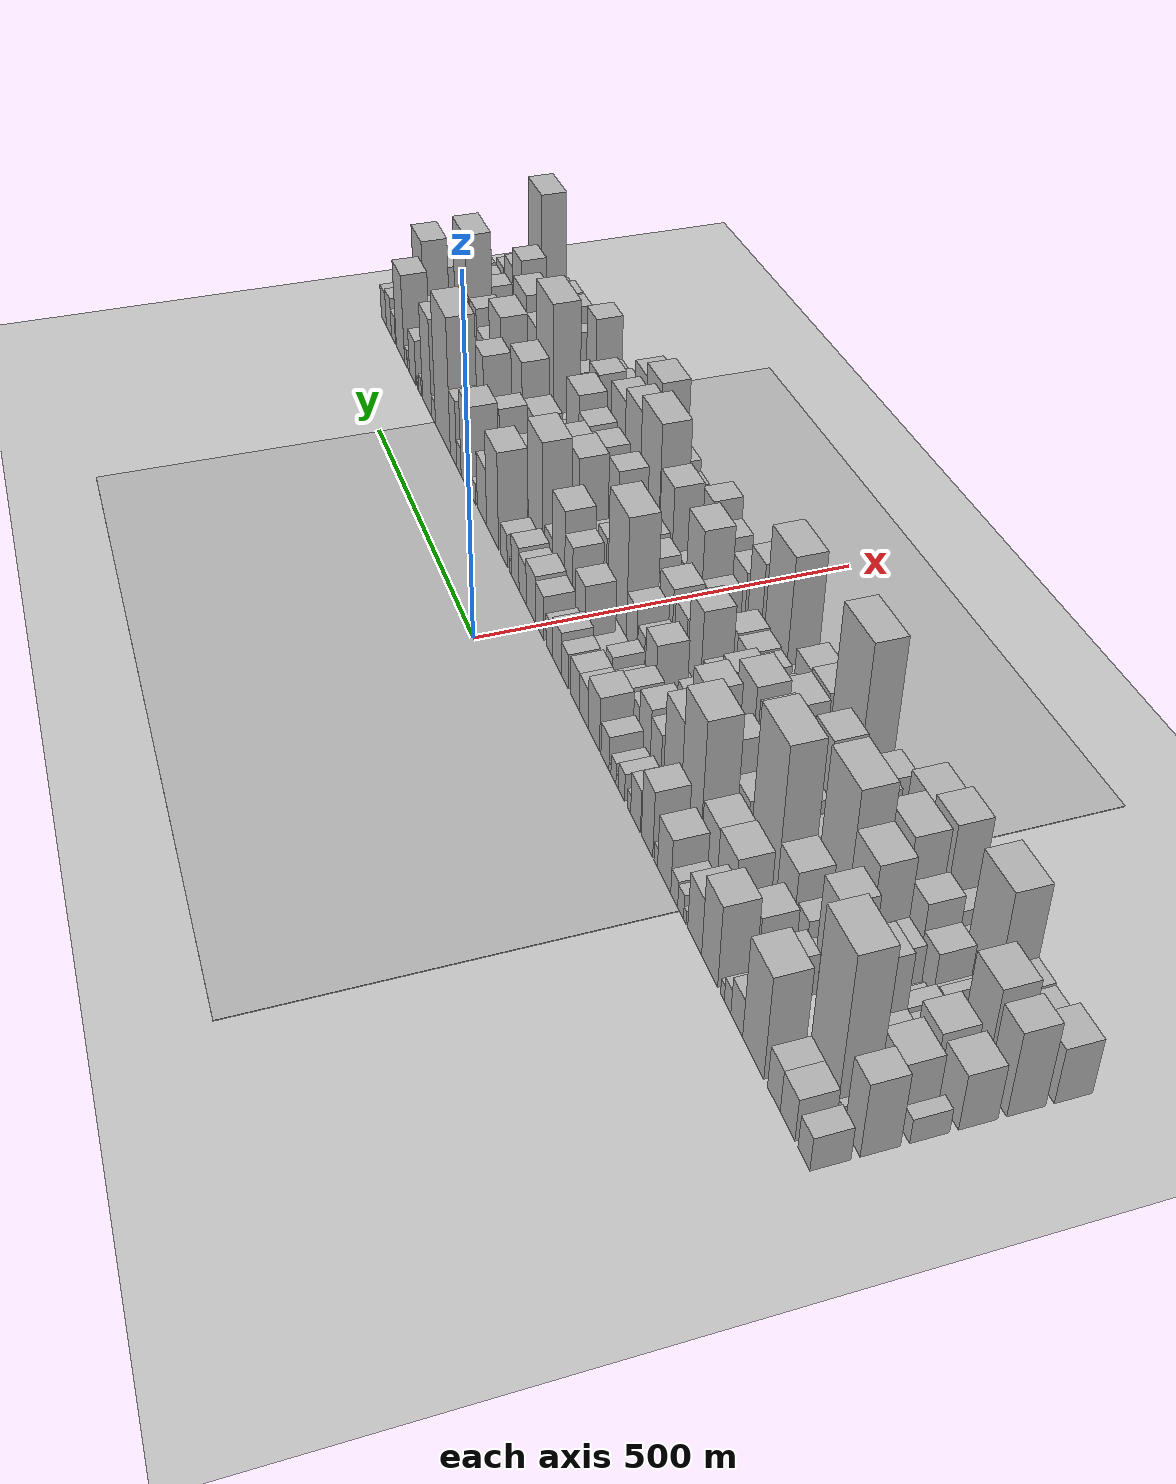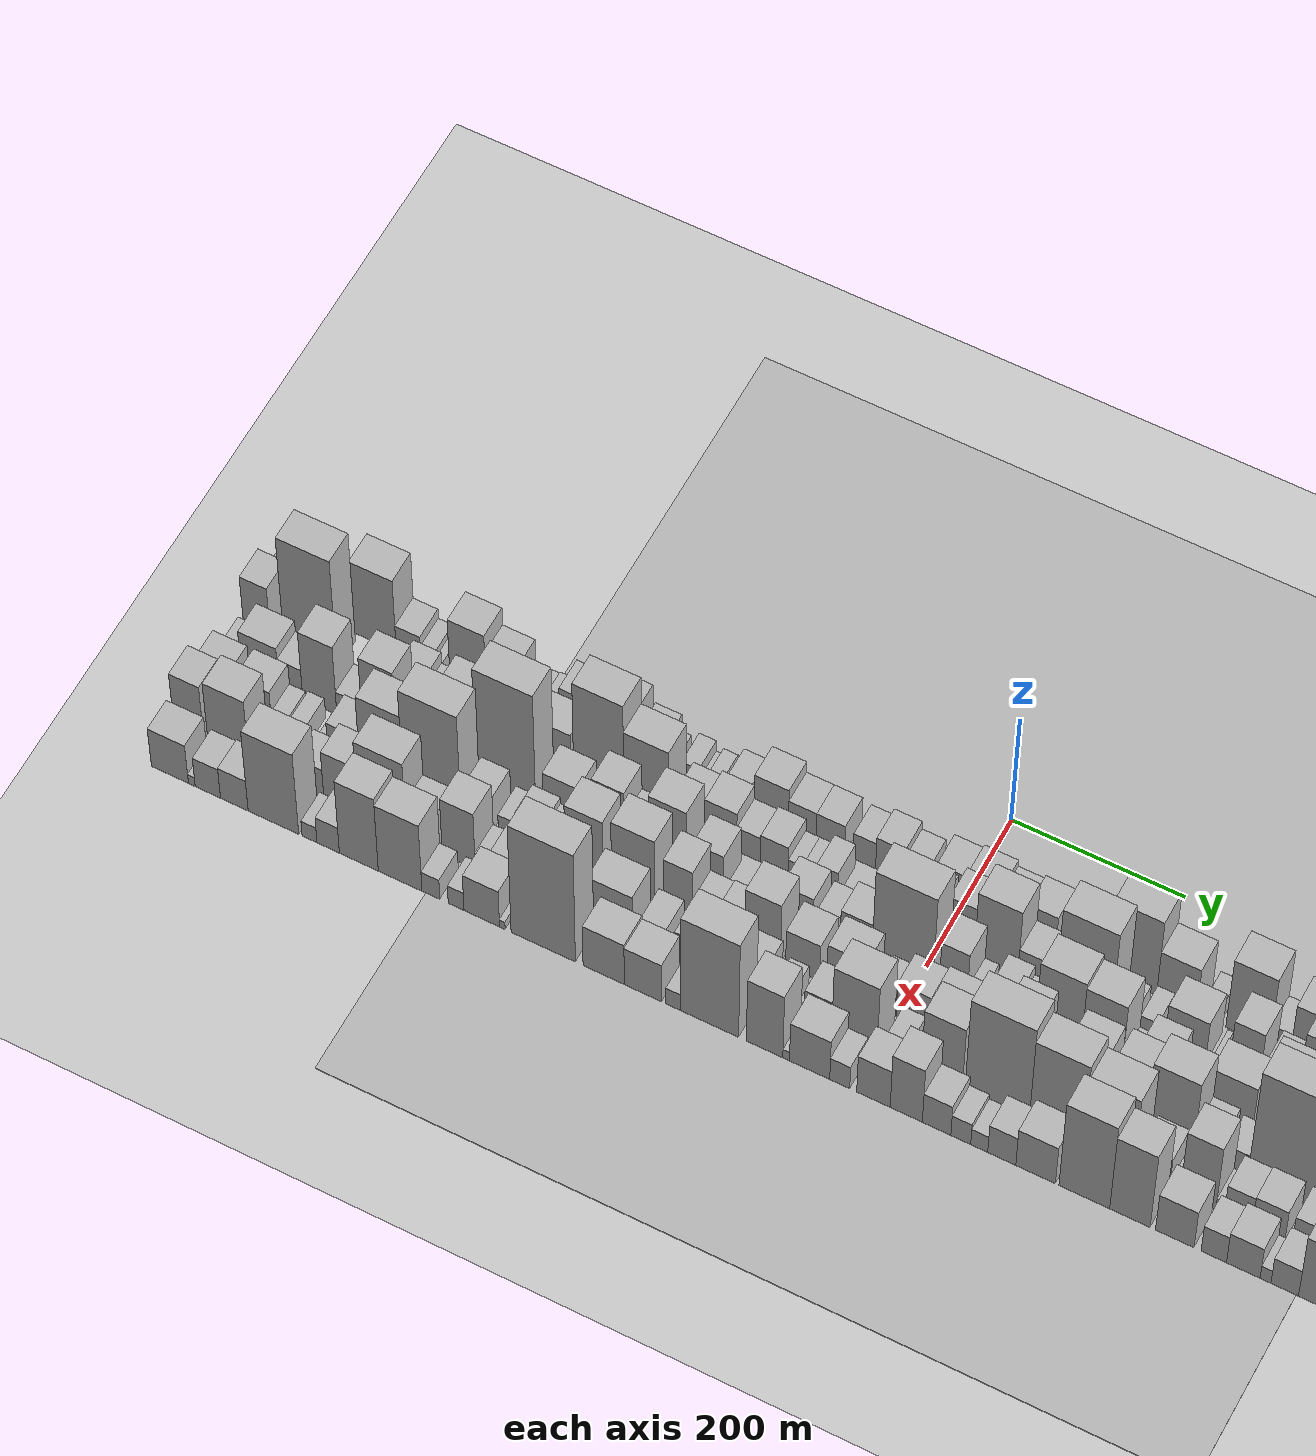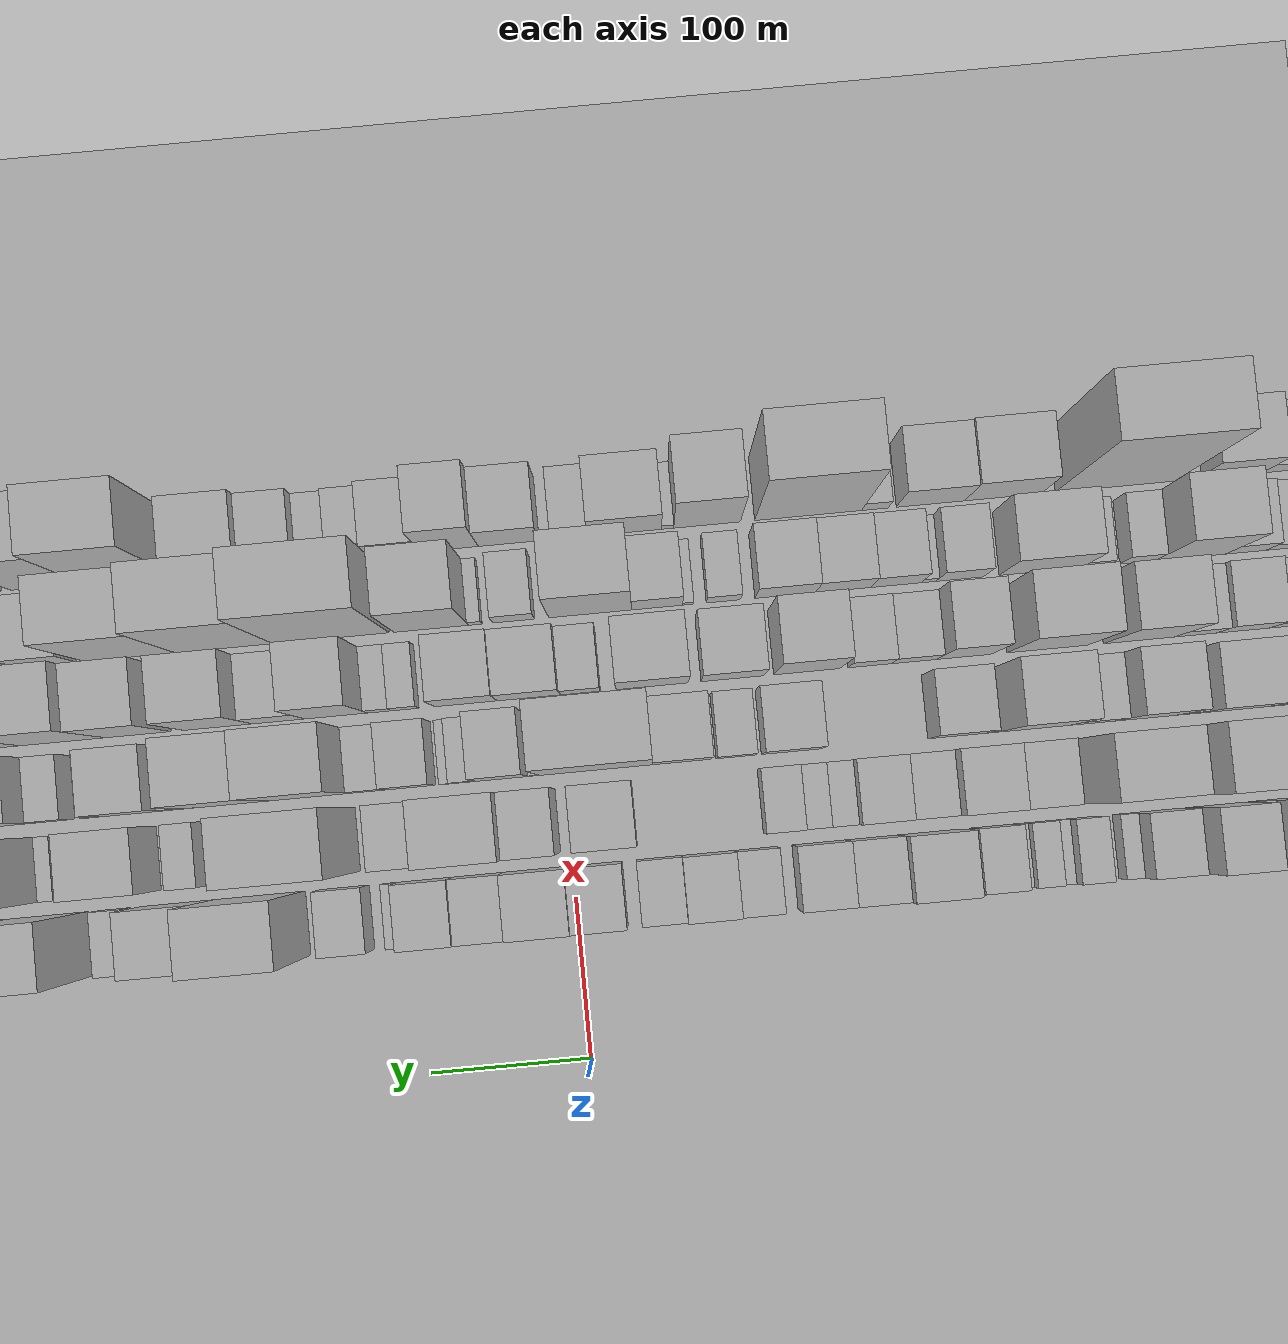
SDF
<?xml version="1.0" encoding="utf-8"?>

<sdf version="1.6">

   <world name="default">

      <gui fullscreen="0">

         <camera name="user_camera">

            <pose>-15 0 4.57585 0 0 0</pose>

            <view_controller>orbit</view_controller>

         </camera>

      </gui>

      <scene>

         <sky>

           <clouds>

             <speed>12</speed>

           </clouds>

         </sky>

         <ambient>0.4 0.4 0.4 1</ambient>

         <background>0.7 0.7 0.7 1</background>

         <shadows>1</shadows>

      </scene>

      <gravity>0 0 -9.8066</gravity>

      <magnetic_field>6e-06 2.3e-05 -4.2e-05</magnetic_field>

      <physics default="0" name="default_physics" type="ode">

         <ode>

            <solver>

               <type>quick</type>

               <iters>10</iters>

               <sor>1.0</sor>

               <use_dynamic_moi_rescaling>0</use_dynamic_moi_rescaling>

            </solver>

            <constraints>

               <cfm>0</cfm>

               <erp>0.2</erp>

               <contact_max_correcting_vel>100</contact_max_correcting_vel>

               <contact_surface_layer>0.001</contact_surface_layer>

            </constraints>

         </ode>

         <max_step_size>0.004</max_step_size>

         <real_time_factor>1</real_time_factor>

         <real_time_update_rate>250</real_time_update_rate>

      </physics>

      <light name="sun" type="directional">

         <cast_shadows>1</cast_shadows>

         <pose>0 0 10 0 0 0</pose>

         <diffuse>0.8 0.8 0.8 1</diffuse>

         <specular>0.2 0.2 0.2 1</specular>

         <attenuation>

            <range>1000</range>

            <constant>0.9</constant>

            <linear>0.01</linear>

            <quadratic>0.001</quadratic>

         </attenuation>

         <direction>-0.5 0.1 -0.9</direction>

      </light>

      <include>

         <name>ground_plane_1</name>

         <uri>model://HANNAS_ground_plane</uri>

         <pose>0 0 0  0 0 0</pose>

      </include>

      <include>

         <name>ground_plane_2</name>

         <uri>model://HANNAS_ground_plane</uri>

         <pose>100 0 0  0 0 0</pose>

      </include>

      <model name="building_1">

         <static>1</static>

         <pose frame="">100.0000 -816.8060 0 0.000000 0.000000 0.000000</pose>

         <link name="link">

            <pose frame="">0 0 22.50 0 0 0</pose>

            <collision name="collision">

               <geometry>

                  <box>

                     <size>40.0000 26.3879 45.0000</size>

                  </box>

               </geometry>

               <max_contacts>10</max_contacts>

               <surface>

                  <contact>

                     <ode/>

                  </contact>

                  <bounce/>

                  <friction>

                     <torsional>

                        <ode/>

                     </torsional>

                     <ode/>

                  </friction>

               </surface>

            </collision>

            <visual name="visual">

               <cast_shadows>0</cast_shadows>

               <geometry>

                  <box>

                     <size>40.0000 26.3879 45.0000</size>

                  </box>

               </geometry>

               <material>

                  <script>

                     <uri>model://HANNAS_wall/materials/scripts</uri>

                     <uri>model://HANNAS_wall/materials/textures</uri>

                     <name>vrc/HANNAS_wall</name>

                  </script>

               </material>

            </visual>

            <self_collide>0</self_collide>

            <enable_wind>0</enable_wind>

            <kinematic>0</kinematic>

         </link>

      </model>

      <model name="building_2">

         <static>1</static>

         <pose frame="">100.0000 -779.7207 0 0.000000 0.000000 0.000000</pose>

         <link name="link">

            <pose frame="">0 0 28.50 0 0 0</pose>

            <collision name="collision">

               <geometry>

                  <box>

                     <size>40.0000 33.7827 57.0000</size>

                  </box>

               </geometry>

               <max_contacts>10</max_contacts>

               <surface>

                  <contact>

                     <ode/>

                  </contact>

                  <bounce/>

                  <friction>

                     <torsional>

                        <ode/>

                     </torsional>

                     <ode/>

                  </friction>

               </surface>

            </collision>

            <visual name="visual">

               <cast_shadows>0</cast_shadows>

               <geometry>

                  <box>

                     <size>40.0000 33.7827 57.0000</size>

                  </box>

               </geometry>

               <material>

                  <script>

                     <uri>model://HANNAS_wall/materials/scripts</uri>

                     <uri>model://HANNAS_wall/materials/textures</uri>

                     <name>vrc/HANNAS_wall</name>

                  </script>

               </material>

            </visual>

            <self_collide>0</self_collide>

            <enable_wind>0</enable_wind>

            <kinematic>0</kinematic>

         </link>

      </model>

      <model name="building_3">

         <static>1</static>

         <pose frame="">100.0000 -747.8682 0 0.000000 0.000000 0.000000</pose>

         <link name="link">

            <pose frame="">0 0 28.50 0 0 0</pose>

            <collision name="collision">

               <geometry>

                  <box>

                     <size>40.0000 29.9222 57.0000</size>

                  </box>

               </geometry>

               <max_contacts>10</max_contacts>

               <surface>

                  <contact>

                     <ode/>

                  </contact>

                  <bounce/>

                  <friction>

                     <torsional>

                        <ode/>

                     </torsional>

                     <ode/>

                  </friction>

               </surface>

            </collision>

            <visual name="visual">

               <cast_shadows>0</cast_shadows>

               <geometry>

                  <box>

                     <size>40.0000 29.9222 57.0000</size>

                  </box>

               </geometry>

               <material>

                  <script>

                     <uri>model://HANNAS_wall/materials/scripts</uri>

                     <uri>model://HANNAS_wall/materials/textures</uri>

                     <name>vrc/HANNAS_wall</name>

                  </script>

               </material>

            </visual>

            <self_collide>0</self_collide>

            <enable_wind>0</enable_wind>

            <kinematic>0</kinematic>

         </link>

      </model>

      <model name="building_4">

         <static>1</static>

         <pose frame="">100.0000 -697.7125 0 0.000000 0.000000 0.000000</pose>

         <link name="link">

            <pose frame="">0 0 69.00 0 0 0</pose>

            <collision name="collision">

               <geometry>

                  <box>

                     <size>40.0000 52.3893 138.0000</size>

                  </box>

               </geometry>

               <max_contacts>10</max_contacts>

               <surface>

                  <contact>

                     <ode/>

                  </contact>

                  <bounce/>

                  <friction>

                     <torsional>

                        <ode/>

                     </torsional>

                     <ode/>

                  </friction>

               </surface>

            </collision>

            <visual name="visual">

               <cast_shadows>0</cast_shadows>

               <geometry>

                  <box>

                     <size>40.0000 52.3893 138.0000</size>

                  </box>

               </geometry>

               <material>

                  <script>

                     <uri>model://HANNAS_wall/materials/scripts</uri>

                     <uri>model://HANNAS_wall/materials/textures</uri>

                     <name>vrc/HANNAS_wall</name>

                  </script>

               </material>

            </visual>

            <self_collide>0</self_collide>

            <enable_wind>0</enable_wind>

            <kinematic>0</kinematic>

         </link>

      </model>

      <model name="building_5">

         <static>1</static>

         <pose frame="">100.0000 -656.4167 0 0.000000 0.000000 0.000000</pose>

         <link name="link">

            <pose frame="">0 0 25.50 0 0 0</pose>

            <collision name="collision">

               <geometry>

                  <box>

                     <size>40.0000 30.2022 51.0000</size>

                  </box>

               </geometry>

               <max_contacts>10</max_contacts>

               <surface>

                  <contact>

                     <ode/>

                  </contact>

                  <bounce/>

                  <friction>

                     <torsional>

                        <ode/>

                     </torsional>

                     <ode/>

                  </friction>

               </surface>

            </collision>

            <visual name="visual">

               <cast_shadows>0</cast_shadows>

               <geometry>

                  <box>

                     <size>40.0000 30.2022 51.0000</size>

                  </box>

               </geometry>

               <material>

                  <script>

                     <uri>model://HANNAS_wall/materials/scripts</uri>

                     <uri>model://HANNAS_wall/materials/textures</uri>

                     <name>vrc/HANNAS_wall</name>

                  </script>

               </material>

            </visual>

            <self_collide>0</self_collide>

            <enable_wind>0</enable_wind>

            <kinematic>0</kinematic>

         </link>

      </model>

      <model name="building_6">

         <static>1</static>

         <pose frame="">100.0000 -632.6692 0 0.000000 0.000000 0.000000</pose>

         <link name="link">

            <pose frame="">0 0 16.50 0 0 0</pose>

            <collision name="collision">

               <geometry>

                  <box>

                     <size>40.0000 17.2929 33.0000</size>

                  </box>

               </geometry>

               <max_contacts>10</max_contacts>

               <surface>

                  <contact>

                     <ode/>

                  </contact>

                  <bounce/>

                  <friction>

                     <torsional>

                        <ode/>

                     </torsional>

                     <ode/>

                  </friction>

               </surface>

            </collision>

            <visual name="visual">

               <cast_shadows>0</cast_shadows>

               <geometry>

                  <box>

                     <size>40.0000 17.2929 33.0000</size>

                  </box>

               </geometry>

               <material>

                  <script>

                     <uri>model://HANNAS_wall/materials/scripts</uri>

                     <uri>model://HANNAS_wall/materials/textures</uri>

                     <name>vrc/HANNAS_wall</name>

                  </script>

               </material>

            </visual>

            <self_collide>0</self_collide>

            <enable_wind>0</enable_wind>

            <kinematic>0</kinematic>

         </link>

      </model>

      <model name="building_7">

         <static>1</static>

         <pose frame="">100.0000 -619.2423 0 0.000000 0.000000 0.000000</pose>

         <link name="link">

            <pose frame="">0 0 10.50 0 0 0</pose>

            <collision name="collision">

               <geometry>

                  <box>

                     <size>40.0000 9.5608 21.0000</size>

                  </box>

               </geometry>

               <max_contacts>10</max_contacts>

               <surface>

                  <contact>

                     <ode/>

                  </contact>

                  <bounce/>

                  <friction>

                     <torsional>

                        <ode/>

                     </torsional>

                     <ode/>

                  </friction>

               </surface>

            </collision>

            <visual name="visual">

               <cast_shadows>0</cast_shadows>

               <geometry>

                  <box>

                     <size>40.0000 9.5608 21.0000</size>

                  </box>

               </geometry>

               <material>

                  <script>

                     <uri>model://HANNAS_wall/materials/scripts</uri>

                     <uri>model://HANNAS_wall/materials/textures</uri>

                     <name>vrc/HANNAS_wall</name>

                  </script>

               </material>

            </visual>

            <self_collide>0</self_collide>

            <enable_wind>0</enable_wind>

            <kinematic>0</kinematic>

         </link>

      </model>

      <model name="building_8">

         <static>1</static>

         <pose frame="">100.0000 -584.6158 0 0.000000 0.000000 0.000000</pose>

         <link name="link">

            <pose frame="">0 0 55.50 0 0 0</pose>

            <collision name="collision">

               <geometry>

                  <box>

                     <size>40.0000 43.6923 111.0000</size>

                  </box>

               </geometry>

               <max_contacts>10</max_contacts>

               <surface>

                  <contact>

                     <ode/>

                  </contact>

                  <bounce/>

                  <friction>

                     <torsional>

                        <ode/>

                     </torsional>

                     <ode/>

                  </friction>

               </surface>

            </collision>

            <visual name="visual">

               <cast_shadows>0</cast_shadows>

               <geometry>

                  <box>

                     <size>40.0000 43.6923 111.0000</size>

                  </box>

               </geometry>

               <material>

                  <script>

                     <uri>model://HANNAS_wall/materials/scripts</uri>

                     <uri>model://HANNAS_wall/materials/textures</uri>

                     <name>vrc/HANNAS_wall</name>

                  </script>

               </material>

            </visual>

            <self_collide>0</self_collide>

            <enable_wind>0</enable_wind>

            <kinematic>0</kinematic>

         </link>

      </model>

      <model name="building_9">

         <static>1</static>

         <pose frame="">100.0000 -543.2670 0 0.000000 0.000000 0.000000</pose>

         <link name="link">

            <pose frame="">0 0 39.00 0 0 0</pose>

            <collision name="collision">

               <geometry>

                  <box>

                     <size>40.0000 39.0051 78.0000</size>

                  </box>

               </geometry>

               <max_contacts>10</max_contacts>

               <surface>

                  <contact>

                     <ode/>

                  </contact>

                  <bounce/>

                  <friction>

                     <torsional>

                        <ode/>

                     </torsional>

                     <ode/>

                  </friction>

               </surface>

            </collision>

            <visual name="visual">

               <cast_shadows>0</cast_shadows>

               <geometry>

                  <box>

                     <size>40.0000 39.0051 78.0000</size>

                  </box>

               </geometry>

               <material>

                  <script>

                     <uri>model://HANNAS_wall/materials/scripts</uri>

                     <uri>model://HANNAS_wall/materials/textures</uri>

                     <name>vrc/HANNAS_wall</name>

                  </script>

               </material>

            </visual>

            <self_collide>0</self_collide>

            <enable_wind>0</enable_wind>

            <kinematic>0</kinematic>

         </link>

      </model>

      <model name="building_10">

         <static>1</static>

         <pose frame="">100.0000 -515.0862 0 0.000000 0.000000 0.000000</pose>

         <link name="link">

            <pose frame="">0 0 9.00 0 0 0</pose>

            <collision name="collision">

               <geometry>

                  <box>

                     <size>40.0000 7.3565 18.0000</size>

                  </box>

               </geometry>

               <max_contacts>10</max_contacts>

               <surface>

                  <contact>

                     <ode/>

                  </contact>

                  <bounce/>

                  <friction>

                     <torsional>

                        <ode/>

                     </torsional>

                     <ode/>

                  </friction>

               </surface>

            </collision>

            <visual name="visual">

               <cast_shadows>0</cast_shadows>

               <geometry>

                  <box>

                     <size>40.0000 7.3565 18.0000</size>

                  </box>

               </geometry>

               <material>

                  <script>

                     <uri>model://HANNAS_wall/materials/scripts</uri>

                     <uri>model://HANNAS_wall/materials/textures</uri>

                     <name>vrc/HANNAS_wall</name>

                  </script>

               </material>

            </visual>

            <self_collide>0</self_collide>

            <enable_wind>0</enable_wind>

            <kinematic>0</kinematic>

         </link>

      </model>

      <model name="building_11">

         <static>1</static>

         <pose frame="">100.0000 -502.9198 0 0.000000 0.000000 0.000000</pose>

         <link name="link">

            <pose frame="">0 0 16.50 0 0 0</pose>

            <collision name="collision">

               <geometry>

                  <box>

                     <size>40.0000 16.9764 33.0000</size>

                  </box>

               </geometry>

               <max_contacts>10</max_contacts>

               <surface>

                  <contact>

                     <ode/>

                  </contact>

                  <bounce/>

                  <friction>

                     <torsional>

                        <ode/>

                     </torsional>

                     <ode/>

                  </friction>

               </surface>

            </collision>

            <visual name="visual">

               <cast_shadows>0</cast_shadows>

               <geometry>

                  <box>

                     <size>40.0000 16.9764 33.0000</size>

                  </box>

               </geometry>

               <material>

                  <script>

                     <uri>model://HANNAS_wall/materials/scripts</uri>

                     <uri>model://HANNAS_wall/materials/textures</uri>

                     <name>vrc/HANNAS_wall</name>

                  </script>

               </material>

            </visual>

            <self_collide>0</self_collide>

            <enable_wind>0</enable_wind>

            <kinematic>0</kinematic>

         </link>

      </model>

      <model name="building_12">

         <static>1</static>

         <pose frame="">100.0000 -484.2531 0 0.000000 0.000000 0.000000</pose>

         <link name="link">

            <pose frame="">0 0 18.00 0 0 0</pose>

            <collision name="collision">

               <geometry>

                  <box>

                     <size>40.0000 20.3569 36.0000</size>

                  </box>

               </geometry>

               <max_contacts>10</max_contacts>

               <surface>

                  <contact>

                     <ode/>

                  </contact>

                  <bounce/>

                  <friction>

                     <torsional>

                        <ode/>

                     </torsional>

                     <ode/>

                  </friction>

               </surface>

            </collision>

            <visual name="visual">

               <cast_shadows>0</cast_shadows>

               <geometry>

                  <box>

                     <size>40.0000 20.3569 36.0000</size>

                  </box>

               </geometry>

               <material>

                  <script>

                     <uri>model://HANNAS_wall/materials/scripts</uri>

                     <uri>model://HANNAS_wall/materials/textures</uri>

                     <name>vrc/HANNAS_wall</name>

                  </script>

               </material>

            </visual>

            <self_collide>0</self_collide>

            <enable_wind>0</enable_wind>

            <kinematic>0</kinematic>

         </link>

      </model>

      <model name="building_13">

         <static>1</static>

         <pose frame="">100.0000 -454.1229 0 0.000000 0.000000 0.000000</pose>

         <link name="link">

            <pose frame="">0 0 37.50 0 0 0</pose>

            <collision name="collision">

               <geometry>

                  <box>

                     <size>40.0000 39.9035 75.0000</size>

                  </box>

               </geometry>

               <max_contacts>10</max_contacts>

               <surface>

                  <contact>

                     <ode/>

                  </contact>

                  <bounce/>

                  <friction>

                     <torsional>

                        <ode/>

                     </torsional>

                     <ode/>

                  </friction>

               </surface>

            </collision>

            <visual name="visual">

               <cast_shadows>0</cast_shadows>

               <geometry>

                  <box>

                     <size>40.0000 39.9035 75.0000</size>

                  </box>

               </geometry>

               <material>

                  <script>

                     <uri>model://HANNAS_wall/materials/scripts</uri>

                     <uri>model://HANNAS_wall/materials/textures</uri>

                     <name>vrc/HANNAS_wall</name>

                  </script>

               </material>

            </visual>

            <self_collide>0</self_collide>

            <enable_wind>0</enable_wind>

            <kinematic>0</kinematic>

         </link>

      </model>

      <model name="building_14">

         <static>1</static>

         <pose frame="">100.0000 -428.7191 0 0.000000 0.000000 0.000000</pose>

         <link name="link">

            <pose frame="">0 0 13.50 0 0 0</pose>

            <collision name="collision">

               <geometry>

                  <box>

                     <size>40.0000 10.9041 27.0000</size>

                  </box>

               </geometry>

               <max_contacts>10</max_contacts>

               <surface>

                  <contact>

                     <ode/>

                  </contact>

                  <bounce/>

                  <friction>

                     <torsional>

                        <ode/>

                     </torsional>

                     <ode/>

                  </friction>

               </surface>

            </collision>

            <visual name="visual">

               <cast_shadows>0</cast_shadows>

               <geometry>

                  <box>

                     <size>40.0000 10.9041 27.0000</size>

                  </box>

               </geometry>

               <material>

                  <script>

                     <uri>model://HANNAS_wall/materials/scripts</uri>

                     <uri>model://HANNAS_wall/materials/textures</uri>

                     <name>vrc/HANNAS_wall</name>

                  </script>

               </material>

            </visual>

            <self_collide>0</self_collide>

            <enable_wind>0</enable_wind>

            <kinematic>0</kinematic>

         </link>

      </model>

      <model name="building_15">

         <static>1</static>

         <pose frame="">100.0000 -401.4031 0 0.000000 0.000000 0.000000</pose>

         <link name="link">

            <pose frame="">0 0 46.50 0 0 0</pose>

            <collision name="collision">

               <geometry>

                  <box>

                     <size>40.0000 35.7279 93.0000</size>

                  </box>

               </geometry>

               <max_contacts>10</max_contacts>

               <surface>

                  <contact>

                     <ode/>

                  </contact>

                  <bounce/>

                  <friction>

                     <torsional>

                        <ode/>

                     </torsional>

                     <ode/>

                  </friction>

               </surface>

            </collision>

            <visual name="visual">

               <cast_shadows>0</cast_shadows>

               <geometry>

                  <box>

                     <size>40.0000 35.7279 93.0000</size>

                  </box>

               </geometry>

               <material>

                  <script>

                     <uri>model://HANNAS_wall/materials/scripts</uri>

                     <uri>model://HANNAS_wall/materials/textures</uri>

                     <name>vrc/HANNAS_wall</name>

                  </script>

               </material>

            </visual>

            <self_collide>0</self_collide>

            <enable_wind>0</enable_wind>

            <kinematic>0</kinematic>

         </link>

      </model>

      <model name="building_16">

         <static>1</static>

         <pose frame="">100.0000 -364.7239 0 0.000000 0.000000 0.000000</pose>

         <link name="link">

            <pose frame="">0 0 30.00 0 0 0</pose>

            <collision name="collision">

               <geometry>

                  <box>

                     <size>40.0000 31.6305 60.0000</size>

                  </box>

               </geometry>

               <max_contacts>10</max_contacts>

               <surface>

                  <contact>

                     <ode/>

                  </contact>

                  <bounce/>

                  <friction>

                     <torsional>

                        <ode/>

                     </torsional>

                     <ode/>

                  </friction>

               </surface>

            </collision>

            <visual name="visual">

               <cast_shadows>0</cast_shadows>

               <geometry>

                  <box>

                     <size>40.0000 31.6305 60.0000</size>

                  </box>

               </geometry>

               <material>

                  <script>

                     <uri>model://HANNAS_wall/materials/scripts</uri>

                     <uri>model://HANNAS_wall/materials/textures</uri>

                     <name>vrc/HANNAS_wall</name>

                  </script>

               </material>

            </visual>

            <self_collide>0</self_collide>

            <enable_wind>0</enable_wind>

            <kinematic>0</kinematic>

         </link>

      </model>

      <model name="building_17">

         <static>1</static>

         <pose frame="">100.0000 -343.2409 0 0.000000 0.000000 0.000000</pose>

         <link name="link">

            <pose frame="">0 0 13.50 0 0 0</pose>

            <collision name="collision">

               <geometry>

                  <box>

                     <size>40.0000 11.3354 27.0000</size>

                  </box>

               </geometry>

               <max_contacts>10</max_contacts>

               <surface>

                  <contact>

                     <ode/>

                  </contact>

                  <bounce/>

                  <friction>

                     <torsional>

                        <ode/>

                     </torsional>

                     <ode/>

                  </friction>

               </surface>

            </collision>

            <visual name="visual">

               <cast_shadows>0</cast_shadows>

               <geometry>

                  <box>

                     <size>40.0000 11.3354 27.0000</size>

                  </box>

               </geometry>

               <material>

                  <script>

                     <uri>model://HANNAS_wall/materials/scripts</uri>

                     <uri>model://HANNAS_wall/materials/textures</uri>

                     <name>vrc/HANNAS_wall</name>

                  </script>

               </material>

            </visual>

            <self_collide>0</self_collide>

            <enable_wind>0</enable_wind>

            <kinematic>0</kinematic>

         </link>

      </model>

      <model name="building_18">

         <static>1</static>

         <pose frame="">100.0000 -318.3768 0 0.000000 0.000000 0.000000</pose>

         <link name="link">

            <pose frame="">0 0 19.50 0 0 0</pose>

            <collision name="collision">

               <geometry>

                  <box>

                     <size>40.0000 20.3929 39.0000</size>

                  </box>

               </geometry>

               <max_contacts>10</max_contacts>

               <surface>

                  <contact>

                     <ode/>

                  </contact>

                  <bounce/>

                  <friction>

                     <torsional>

                        <ode/>

                     </torsional>

                     <ode/>

                  </friction>

               </surface>

            </collision>

            <visual name="visual">

               <cast_shadows>0</cast_shadows>

               <geometry>

                  <box>

                     <size>40.0000 20.3929 39.0000</size>

                  </box>

               </geometry>

               <material>

                  <script>

                     <uri>model://HANNAS_wall/materials/scripts</uri>

                     <uri>model://HANNAS_wall/materials/textures</uri>

                     <name>vrc/HANNAS_wall</name>

                  </script>

               </material>

            </visual>

            <self_collide>0</self_collide>

            <enable_wind>0</enable_wind>

            <kinematic>0</kinematic>

         </link>

      </model>

      <model name="building_19">

         <static>1</static>

         <pose frame="">100.0000 -303.9066 0 0.000000 0.000000 0.000000</pose>

         <link name="link">

            <pose frame="">0 0 9.00 0 0 0</pose>

            <collision name="collision">

               <geometry>

                  <box>

                     <size>40.0000 8.5474 18.0000</size>

                  </box>

               </geometry>

               <max_contacts>10</max_contacts>

               <surface>

                  <contact>

                     <ode/>

                  </contact>

                  <bounce/>

                  <friction>

                     <torsional>

                        <ode/>

                     </torsional>

                     <ode/>

                  </friction>

               </surface>

            </collision>

            <visual name="visual">

               <cast_shadows>0</cast_shadows>

               <geometry>

                  <box>

                     <size>40.0000 8.5474 18.0000</size>

                  </box>

               </geometry>

               <material>

                  <script>

                     <uri>model://HANNAS_wall/materials/scripts</uri>

                     <uri>model://HANNAS_wall/materials/textures</uri>

                     <name>vrc/HANNAS_wall</name>

                  </script>

               </material>

            </visual>

            <self_collide>0</self_collide>

            <enable_wind>0</enable_wind>

            <kinematic>0</kinematic>

         </link>

      </model>

      <model name="building_20">

         <static>1</static>

         <pose frame="">100.0000 -291.0988 0 0.000000 0.000000 0.000000</pose>

         <link name="link">

            <pose frame="">0 0 15.00 0 0 0</pose>

            <collision name="collision">

               <geometry>

                  <box>

                     <size>40.0000 17.0682 30.0000</size>

                  </box>

               </geometry>

               <max_contacts>10</max_contacts>

               <surface>

                  <contact>

                     <ode/>

                  </contact>

                  <bounce/>

                  <friction>

                     <torsional>

                        <ode/>

                     </torsional>

                     <ode/>

                  </friction>

               </surface>

            </collision>

            <visual name="visual">

               <cast_shadows>0</cast_shadows>

               <geometry>

                  <box>

                     <size>40.0000 17.0682 30.0000</size>

                  </box>

               </geometry>

               <material>

                  <script>

                     <uri>model://HANNAS_wall/materials/scripts</uri>

                     <uri>model://HANNAS_wall/materials/textures</uri>

                     <name>vrc/HANNAS_wall</name>

                  </script>

               </material>

            </visual>

            <self_collide>0</self_collide>

            <enable_wind>0</enable_wind>

            <kinematic>0</kinematic>

         </link>

      </model>

      <model name="building_21">

         <static>1</static>

         <pose frame="">100.0000 -279.0963 0 0.000000 0.000000 0.000000</pose>

         <link name="link">

            <pose frame="">0 0 7.50 0 0 0</pose>

            <collision name="collision">

               <geometry>

                  <box>

                     <size>40.0000 6.9368 15.0000</size>

                  </box>

               </geometry>

               <max_contacts>10</max_contacts>

               <surface>

                  <contact>

                     <ode/>

                  </contact>

                  <bounce/>

                  <friction>

                     <torsional>

                        <ode/>

                     </torsional>

                     <ode/>

                  </friction>

               </surface>

            </collision>

            <visual name="visual">

               <cast_shadows>0</cast_shadows>

               <geometry>

                  <box>

                     <size>40.0000 6.9368 15.0000</size>

                  </box>

               </geometry>

               <material>

                  <script>

                     <uri>model://HANNAS_wall/materials/scripts</uri>

                     <uri>model://HANNAS_wall/materials/textures</uri>

                     <name>vrc/HANNAS_wall</name>

                  </script>

               </material>

            </visual>

            <self_collide>0</self_collide>

            <enable_wind>0</enable_wind>

            <kinematic>0</kinematic>

         </link>

      </model>

      <model name="building_22">

         <static>1</static>

         <pose frame="">100.0000 -261.6597 0 0.000000 0.000000 0.000000</pose>

         <link name="link">

            <pose frame="">0 0 24.00 0 0 0</pose>

            <collision name="collision">

               <geometry>

                  <box>

                     <size>40.0000 27.9364 48.0000</size>

                  </box>

               </geometry>

               <max_contacts>10</max_contacts>

               <surface>

                  <contact>

                     <ode/>

                  </contact>

                  <bounce/>

                  <friction>

                     <torsional>

                        <ode/>

                     </torsional>

                     <ode/>

                  </friction>

               </surface>

            </collision>

            <visual name="visual">

               <cast_shadows>0</cast_shadows>

               <geometry>

                  <box>

                     <size>40.0000 27.9364 48.0000</size>

                  </box>

               </geometry>

               <material>

                  <script>

                     <uri>model://HANNAS_wall/materials/scripts</uri>

                     <uri>model://HANNAS_wall/materials/textures</uri>

                     <name>vrc/HANNAS_wall</name>

                  </script>

               </material>

            </visual>

            <self_collide>0</self_collide>

            <enable_wind>0</enable_wind>

            <kinematic>0</kinematic>

         </link>

      </model>

      <model name="building_23">

         <static>1</static>

         <pose frame="">100.0000 -222.5226 0 0.000000 0.000000 0.000000</pose>

         <link name="link">

            <pose frame="">0 0 39.00 0 0 0</pose>

            <collision name="collision">

               <geometry>

                  <box>

                     <size>40.0000 40.3378 78.0000</size>

                  </box>

               </geometry>

               <max_contacts>10</max_contacts>

               <surface>

                  <contact>

                     <ode/>

                  </contact>

                  <bounce/>

                  <friction>

                     <torsional>

                        <ode/>

                     </torsional>

                     <ode/>

                  </friction>

               </surface>

            </collision>

            <visual name="visual">

               <cast_shadows>0</cast_shadows>

               <geometry>

                  <box>

                     <size>40.0000 40.3378 78.0000</size>

                  </box>

               </geometry>

               <material>

                  <script>

                     <uri>model://HANNAS_wall/materials/scripts</uri>

                     <uri>model://HANNAS_wall/materials/textures</uri>

                     <name>vrc/HANNAS_wall</name>

                  </script>

               </material>

            </visual>

            <self_collide>0</self_collide>

            <enable_wind>0</enable_wind>

            <kinematic>0</kinematic>

         </link>

      </model>

      <model name="building_24">

         <static>1</static>

         <pose frame="">100.0000 -186.0903 0 0.000000 0.000000 0.000000</pose>

         <link name="link">

            <pose frame="">0 0 28.50 0 0 0</pose>

            <collision name="collision">

               <geometry>

                  <box>

                     <size>40.0000 32.5268 57.0000</size>

                  </box>

               </geometry>

               <max_contacts>10</max_contacts>

               <surface>

                  <contact>

                     <ode/>

                  </contact>

                  <bounce/>

                  <friction>

                     <torsional>

                        <ode/>

                     </torsional>

                     <ode/>

                  </friction>

               </surface>

            </collision>

            <visual name="visual">

               <cast_shadows>0</cast_shadows>

               <geometry>

                  <box>

                     <size>40.0000 32.5268 57.0000</size>

                  </box>

               </geometry>

               <material>

                  <script>

                     <uri>model://HANNAS_wall/materials/scripts</uri>

                     <uri>model://HANNAS_wall/materials/textures</uri>

                     <name>vrc/HANNAS_wall</name>

                  </script>

               </material>

            </visual>

            <self_collide>0</self_collide>

            <enable_wind>0</enable_wind>

            <kinematic>0</kinematic>

         </link>

      </model>

      <model name="building_25">

         <static>1</static>

         <pose frame="">100.0000 -153.0803 0 0.000000 0.000000 0.000000</pose>

         <link name="link">

            <pose frame="">0 0 28.50 0 0 0</pose>

            <collision name="collision">

               <geometry>

                  <box>

                     <size>40.0000 33.4933 57.0000</size>

                  </box>

               </geometry>

               <max_contacts>10</max_contacts>

               <surface>

                  <contact>

                     <ode/>

                  </contact>

                  <bounce/>

                  <friction>

                     <torsional>

                        <ode/>

                     </torsional>

                     <ode/>

                  </friction>

               </surface>

            </collision>

            <visual name="visual">

               <cast_shadows>0</cast_shadows>

               <geometry>

                  <box>

                     <size>40.0000 33.4933 57.0000</size>

                  </box>

               </geometry>

               <material>

                  <script>

                     <uri>model://HANNAS_wall/materials/scripts</uri>

                     <uri>model://HANNAS_wall/materials/textures</uri>

                     <name>vrc/HANNAS_wall</name>

                  </script>

               </material>

            </visual>

            <self_collide>0</self_collide>

            <enable_wind>0</enable_wind>

            <kinematic>0</kinematic>

         </link>

      </model>

      <model name="building_26">

         <static>1</static>

         <pose frame="">100.0000 -113.0891 0 0.000000 0.000000 0.000000</pose>

         <link name="link">

            <pose frame="">0 0 25.50 0 0 0</pose>

            <collision name="collision">

               <geometry>

                  <box>

                     <size>40.0000 26.4892 51.0000</size>

                  </box>

               </geometry>

               <max_contacts>10</max_contacts>

               <surface>

                  <contact>

                     <ode/>

                  </contact>

                  <bounce/>

                  <friction>

                     <torsional>

                        <ode/>

                     </torsional>

                     <ode/>

                  </friction>

               </surface>

            </collision>

            <visual name="visual">

               <cast_shadows>0</cast_shadows>

               <geometry>

                  <box>

                     <size>40.0000 26.4892 51.0000</size>

                  </box>

               </geometry>

               <material>

                  <script>

                     <uri>model://HANNAS_wall/materials/scripts</uri>

                     <uri>model://HANNAS_wall/materials/textures</uri>

                     <name>vrc/HANNAS_wall</name>

                  </script>

               </material>

            </visual>

            <self_collide>0</self_collide>

            <enable_wind>0</enable_wind>

            <kinematic>0</kinematic>

         </link>

      </model>

      <model name="building_27">

         <static>1</static>

         <pose frame="">100.0000 -83.3933 0 0.000000 0.000000 0.000000</pose>

         <link name="link">

            <pose frame="">0 0 31.50 0 0 0</pose>

            <collision name="collision">

               <geometry>

                  <box>

                     <size>40.0000 32.9023 63.0000</size>

                  </box>

               </geometry>

               <max_contacts>10</max_contacts>

               <surface>

                  <contact>

                     <ode/>

                  </contact>

                  <bounce/>

                  <friction>

                     <torsional>

                        <ode/>

                     </torsional>

                     <ode/>

                  </friction>

               </surface>

            </collision>

            <visual name="visual">

               <cast_shadows>0</cast_shadows>

               <geometry>

                  <box>

                     <size>40.0000 32.9023 63.0000</size>

                  </box>

               </geometry>

               <material>

                  <script>

                     <uri>model://HANNAS_wall/materials/scripts</uri>

                     <uri>model://HANNAS_wall/materials/textures</uri>

                     <name>vrc/HANNAS_wall</name>

                  </script>

               </material>

            </visual>

            <self_collide>0</self_collide>

            <enable_wind>0</enable_wind>

            <kinematic>0</kinematic>

         </link>

      </model>

      <model name="building_28">

         <static>1</static>

         <pose frame="">100.0000 -52.9506 0 0.000000 0.000000 0.000000</pose>

         <link name="link">

            <pose frame="">0 0 24.00 0 0 0</pose>

            <collision name="collision">

               <geometry>

                  <box>

                     <size>40.0000 27.9831 48.0000</size>

                  </box>

               </geometry>

               <max_contacts>10</max_contacts>

               <surface>

                  <contact>

                     <ode/>

                  </contact>

                  <bounce/>

                  <friction>

                     <torsional>

                        <ode/>

                     </torsional>

                     <ode/>

                  </friction>

               </surface>

            </collision>

            <visual name="visual">

               <cast_shadows>0</cast_shadows>

               <geometry>

                  <box>

                     <size>40.0000 27.9831 48.0000</size>

                  </box>

               </geometry>

               <material>

                  <script>

                     <uri>model://HANNAS_wall/materials/scripts</uri>

                     <uri>model://HANNAS_wall/materials/textures</uri>

                     <name>vrc/HANNAS_wall</name>

                  </script>

               </material>

            </visual>

            <self_collide>0</self_collide>

            <enable_wind>0</enable_wind>

            <kinematic>0</kinematic>

         </link>

      </model>

      <model name="building_29">

         <static>1</static>

         <pose frame="">100.0000 -12.7540 0 0.000000 0.000000 0.000000</pose>

         <link name="link">

            <pose frame="">0 0 33.00 0 0 0</pose>

            <collision name="collision">

               <geometry>

                  <box>

                     <size>40.0000 34.4102 66.0000</size>

                  </box>

               </geometry>

               <max_contacts>10</max_contacts>

               <surface>

                  <contact>

                     <ode/>

                  </contact>

                  <bounce/>

                  <friction>

                     <torsional>

                        <ode/>

                     </torsional>

                     <ode/>

                  </friction>

               </surface>

            </collision>

            <visual name="visual">

               <cast_shadows>0</cast_shadows>

               <geometry>

                  <box>

                     <size>40.0000 34.4102 66.0000</size>

                  </box>

               </geometry>

               <material>

                  <script>

                     <uri>model://HANNAS_wall/materials/scripts</uri>

                     <uri>model://HANNAS_wall/materials/textures</uri>

                     <name>vrc/HANNAS_wall</name>

                  </script>

               </material>

            </visual>

            <self_collide>0</self_collide>

            <enable_wind>0</enable_wind>

            <kinematic>0</kinematic>

         </link>

      </model>

      <model name="building_30">

         <static>1</static>

         <pose frame="">100.0000 24.2124 0 0.000000 0.000000 0.000000</pose>

         <link name="link">

            <pose frame="">0 0 36.00 0 0 0</pose>

            <collision name="collision">

               <geometry>

                  <box>

                     <size>40.0000 39.5224 72.0000</size>

                  </box>

               </geometry>

               <max_contacts>10</max_contacts>

               <surface>

                  <contact>

                     <ode/>

                  </contact>

                  <bounce/>

                  <friction>

                     <torsional>

                        <ode/>

                     </torsional>

                     <ode/>

                  </friction>

               </surface>

            </collision>

            <visual name="visual">

               <cast_shadows>0</cast_shadows>

               <geometry>

                  <box>

                     <size>40.0000 39.5224 72.0000</size>

                  </box>

               </geometry>

               <material>

                  <script>

                     <uri>model://HANNAS_wall/materials/scripts</uri>

                     <uri>model://HANNAS_wall/materials/textures</uri>

                     <name>vrc/HANNAS_wall</name>

                  </script>

               </material>

            </visual>

            <self_collide>0</self_collide>

            <enable_wind>0</enable_wind>

            <kinematic>0</kinematic>

         </link>

      </model>

      <model name="building_31">

         <static>1</static>

         <pose frame="">100.0000 59.7044 0 0.000000 0.000000 0.000000</pose>

         <link name="link">

            <pose frame="">0 0 30.00 0 0 0</pose>

            <collision name="collision">

               <geometry>

                  <box>

                     <size>40.0000 31.4618 60.0000</size>

                  </box>

               </geometry>

               <max_contacts>10</max_contacts>

               <surface>

                  <contact>

                     <ode/>

                  </contact>

                  <bounce/>

                  <friction>

                     <torsional>

                        <ode/>

                     </torsional>

                     <ode/>

                  </friction>

               </surface>

            </collision>

            <visual name="visual">

               <cast_shadows>0</cast_shadows>

               <geometry>

                  <box>

                     <size>40.0000 31.4618 60.0000</size>

                  </box>

               </geometry>

               <material>

                  <script>

                     <uri>model://HANNAS_wall/materials/scripts</uri>

                     <uri>model://HANNAS_wall/materials/textures</uri>

                     <name>vrc/HANNAS_wall</name>

                  </script>

               </material>

            </visual>

            <self_collide>0</self_collide>

            <enable_wind>0</enable_wind>

            <kinematic>0</kinematic>

         </link>

      </model>

      <model name="building_32">

         <static>1</static>

         <pose frame="">100.0000 92.4821 0 0.000000 0.000000 0.000000</pose>

         <link name="link">

            <pose frame="">0 0 33.00 0 0 0</pose>

            <collision name="collision">

               <geometry>

                  <box>

                     <size>40.0000 34.0936 66.0000</size>

                  </box>

               </geometry>

               <max_contacts>10</max_contacts>

               <surface>

                  <contact>

                     <ode/>

                  </contact>

                  <bounce/>

                  <friction>

                     <torsional>

                        <ode/>

                     </torsional>

                     <ode/>

                  </friction>

               </surface>

            </collision>

            <visual name="visual">

               <cast_shadows>0</cast_shadows>

               <geometry>

                  <box>

                     <size>40.0000 34.0936 66.0000</size>

                  </box>

               </geometry>

               <material>

                  <script>

                     <uri>model://HANNAS_wall/materials/scripts</uri>

                     <uri>model://HANNAS_wall/materials/textures</uri>

                     <name>vrc/HANNAS_wall</name>

                  </script>

               </material>

            </visual>

            <self_collide>0</self_collide>

            <enable_wind>0</enable_wind>

            <kinematic>0</kinematic>

         </link>

      </model>

      <model name="building_33">

         <static>1</static>

         <pose frame="">100.0000 114.5260 0 0.000000 0.000000 0.000000</pose>

         <link name="link">

            <pose frame="">0 0 12.00 0 0 0</pose>

            <collision name="collision">

               <geometry>

                  <box>

                     <size>40.0000 9.9941 24.0000</size>

                  </box>

               </geometry>

               <max_contacts>10</max_contacts>

               <surface>

                  <contact>

                     <ode/>

                  </contact>

                  <bounce/>

                  <friction>

                     <torsional>

                        <ode/>

                     </torsional>

                     <ode/>

                  </friction>

               </surface>

            </collision>

            <visual name="visual">

               <cast_shadows>0</cast_shadows>

               <geometry>

                  <box>

                     <size>40.0000 9.9941 24.0000</size>

                  </box>

               </geometry>

               <material>

                  <script>

                     <uri>model://HANNAS_wall/materials/scripts</uri>

                     <uri>model://HANNAS_wall/materials/textures</uri>

                     <name>vrc/HANNAS_wall</name>

                  </script>

               </material>

            </visual>

            <self_collide>0</self_collide>

            <enable_wind>0</enable_wind>

            <kinematic>0</kinematic>

         </link>

      </model>

      <model name="building_34">

         <static>1</static>

         <pose frame="">100.0000 143.4806 0 0.000000 0.000000 0.000000</pose>

         <link name="link">

            <pose frame="">0 0 25.50 0 0 0</pose>

            <collision name="collision">

               <geometry>

                  <box>

                     <size>40.0000 29.9153 51.0000</size>

                  </box>

               </geometry>

               <max_contacts>10</max_contacts>

               <surface>

                  <contact>

                     <ode/>

                  </contact>

                  <bounce/>

                  <friction>

                     <torsional>

                        <ode/>

                     </torsional>

                     <ode/>

                  </friction>

               </surface>

            </collision>

            <visual name="visual">

               <cast_shadows>0</cast_shadows>

               <geometry>

                  <box>

                     <size>40.0000 29.9153 51.0000</size>

                  </box>

               </geometry>

               <material>

                  <script>

                     <uri>model://HANNAS_wall/materials/scripts</uri>

                     <uri>model://HANNAS_wall/materials/textures</uri>

                     <name>vrc/HANNAS_wall</name>

                  </script>

               </material>

            </visual>

            <self_collide>0</self_collide>

            <enable_wind>0</enable_wind>

            <kinematic>0</kinematic>

         </link>

      </model>

      <model name="building_35">

         <static>1</static>

         <pose frame="">100.0000 196.8723 0 0.000000 0.000000 0.000000</pose>

         <link name="link">

            <pose frame="">0 0 75.00 0 0 0</pose>

            <collision name="collision">

               <geometry>

                  <box>

                     <size>40.0000 56.8681 150.0000</size>

                  </box>

               </geometry>

               <max_contacts>10</max_contacts>

               <surface>

                  <contact>

                     <ode/>

                  </contact>

                  <bounce/>

                  <friction>

                     <torsional>

                        <ode/>

                     </torsional>

                     <ode/>

                  </friction>

               </surface>

            </collision>

            <visual name="visual">

               <cast_shadows>0</cast_shadows>

               <geometry>

                  <box>

                     <size>40.0000 56.8681 150.0000</size>

                  </box>

               </geometry>

               <material>

                  <script>

                     <uri>model://HANNAS_wall/materials/scripts</uri>

                     <uri>model://HANNAS_wall/materials/textures</uri>

                     <name>vrc/HANNAS_wall</name>

                  </script>

               </material>

            </visual>

            <self_collide>0</self_collide>

            <enable_wind>0</enable_wind>

            <kinematic>0</kinematic>

         </link>

      </model>

      <model name="building_36">

         <static>1</static>

         <pose frame="">100.0000 248.1590 0 0.000000 0.000000 0.000000</pose>

         <link name="link">

            <pose frame="">0 0 45.00 0 0 0</pose>

            <collision name="collision">

               <geometry>

                  <box>

                     <size>40.0000 45.7053 90.0000</size>

                  </box>

               </geometry>

               <max_contacts>10</max_contacts>

               <surface>

                  <contact>

                     <ode/>

                  </contact>

                  <bounce/>

                  <friction>

                     <torsional>

                        <ode/>

                     </torsional>

                     <ode/>

                  </friction>

               </surface>

            </collision>

            <visual name="visual">

               <cast_shadows>0</cast_shadows>

               <geometry>

                  <box>

                     <size>40.0000 45.7053 90.0000</size>

                  </box>

               </geometry>

               <material>

                  <script>

                     <uri>model://HANNAS_wall/materials/scripts</uri>

                     <uri>model://HANNAS_wall/materials/textures</uri>

                     <name>vrc/HANNAS_wall</name>

                  </script>

               </material>

            </visual>

            <self_collide>0</self_collide>

            <enable_wind>0</enable_wind>

            <kinematic>0</kinematic>

         </link>

      </model>

      <model name="building_37">

         <static>1</static>

         <pose frame="">100.0000 287.7632 0 0.000000 0.000000 0.000000</pose>

         <link name="link">

            <pose frame="">0 0 16.50 0 0 0</pose>

            <collision name="collision">

               <geometry>

                  <box>

                     <size>40.0000 19.5032 33.0000</size>

                  </box>

               </geometry>

               <max_contacts>10</max_contacts>

               <surface>

                  <contact>

                     <ode/>

                  </contact>

                  <bounce/>

                  <friction>

                     <torsional>

                        <ode/>

                     </torsional>

                     <ode/>

                  </friction>

               </surface>

            </collision>

            <visual name="visual">

               <cast_shadows>0</cast_shadows>

               <geometry>

                  <box>

                     <size>40.0000 19.5032 33.0000</size>

                  </box>

               </geometry>

               <material>

                  <script>

                     <uri>model://HANNAS_wall/materials/scripts</uri>

                     <uri>model://HANNAS_wall/materials/textures</uri>

                     <name>vrc/HANNAS_wall</name>

                  </script>

               </material>

            </visual>

            <self_collide>0</self_collide>

            <enable_wind>0</enable_wind>

            <kinematic>0</kinematic>

         </link>

      </model>

      <model name="building_38">

         <static>1</static>

         <pose frame="">100.0000 329.3629 0 0.000000 0.000000 0.000000</pose>

         <link name="link">

            <pose frame="">0 0 69.00 0 0 0</pose>

            <collision name="collision">

               <geometry>

                  <box>

                     <size>40.0000 49.6962 138.0000</size>

                  </box>

               </geometry>

               <max_contacts>10</max_contacts>

               <surface>

                  <contact>

                     <ode/>

                  </contact>

                  <bounce/>

                  <friction>

                     <torsional>

                        <ode/>

                     </torsional>

                     <ode/>

                  </friction>

               </surface>

            </collision>

            <visual name="visual">

               <cast_shadows>0</cast_shadows>

               <geometry>

                  <box>

                     <size>40.0000 49.6962 138.0000</size>

                  </box>

               </geometry>

               <material>

                  <script>

                     <uri>model://HANNAS_wall/materials/scripts</uri>

                     <uri>model://HANNAS_wall/materials/textures</uri>

                     <name>vrc/HANNAS_wall</name>

                  </script>

               </material>

            </visual>

            <self_collide>0</self_collide>

            <enable_wind>0</enable_wind>

            <kinematic>0</kinematic>

         </link>

      </model>

      <model name="building_39">

         <static>1</static>

         <pose frame="">100.0000 365.7605 0 0.000000 0.000000 0.000000</pose>

         <link name="link">

            <pose frame="">0 0 22.50 0 0 0</pose>

            <collision name="collision">

               <geometry>

                  <box>

                     <size>40.0000 23.0989 45.0000</size>

                  </box>

               </geometry>

               <max_contacts>10</max_contacts>

               <surface>

                  <contact>

                     <ode/>

                  </contact>

                  <bounce/>

                  <friction>

                     <torsional>

                        <ode/>

                     </torsional>

                     <ode/>

                  </friction>

               </surface>

            </collision>

            <visual name="visual">

               <cast_shadows>0</cast_shadows>

               <geometry>

                  <box>

                     <size>40.0000 23.0989 45.0000</size>

                  </box>

               </geometry>

               <material>

                  <script>

                     <uri>model://HANNAS_wall/materials/scripts</uri>

                     <uri>model://HANNAS_wall/materials/textures</uri>

                     <name>vrc/HANNAS_wall</name>

                  </script>

               </material>

            </visual>

            <self_collide>0</self_collide>

            <enable_wind>0</enable_wind>

            <kinematic>0</kinematic>

         </link>

      </model>

      <model name="building_40">

         <static>1</static>

         <pose frame="">100.0000 394.3797 0 0.000000 0.000000 0.000000</pose>

         <link name="link">

            <pose frame="">0 0 52.50 0 0 0</pose>

            <collision name="collision">

               <geometry>

                  <box>

                     <size>40.0000 34.1395 105.0000</size>

                  </box>

               </geometry>

               <max_contacts>10</max_contacts>

               <surface>

                  <contact>

                     <ode/>

                  </contact>

                  <bounce/>

                  <friction>

                     <torsional>

                        <ode/>

                     </torsional>

                     <ode/>

                  </friction>

               </surface>

            </collision>

            <visual name="visual">

               <cast_shadows>0</cast_shadows>

               <geometry>

                  <box>

                     <size>40.0000 34.1395 105.0000</size>

                  </box>

               </geometry>

               <material>

                  <script>

                     <uri>model://HANNAS_wall/materials/scripts</uri>

                     <uri>model://HANNAS_wall/materials/textures</uri>

                     <name>vrc/HANNAS_wall</name>

                  </script>

               </material>

            </visual>

            <self_collide>0</self_collide>

            <enable_wind>0</enable_wind>

            <kinematic>0</kinematic>

         </link>

      </model>

      <model name="building_41">

         <static>1</static>

         <pose frame="">100.0000 452.6909 0 0.000000 0.000000 0.000000</pose>

         <link name="link">

            <pose frame="">0 0 108.00 0 0 0</pose>

            <collision name="collision">

               <geometry>

                  <box>

                     <size>40.0000 82.4830 216.0000</size>

                  </box>

               </geometry>

               <max_contacts>10</max_contacts>

               <surface>

                  <contact>

                     <ode/>

                  </contact>

                  <bounce/>

                  <friction>

                     <torsional>

                        <ode/>

                     </torsional>

                     <ode/>

                  </friction>

               </surface>

            </collision>

            <visual name="visual">

               <cast_shadows>0</cast_shadows>

               <geometry>

                  <box>

                     <size>40.0000 82.4830 216.0000</size>

                  </box>

               </geometry>

               <material>

                  <script>

                     <uri>model://HANNAS_wall/materials/scripts</uri>

                     <uri>model://HANNAS_wall/materials/textures</uri>

                     <name>vrc/HANNAS_wall</name>

                  </script>

               </material>

            </visual>

            <self_collide>0</self_collide>

            <enable_wind>0</enable_wind>

            <kinematic>0</kinematic>

         </link>

      </model>

      <model name="building_42">

         <static>1</static>

         <pose frame="">100.0000 504.3859 0 0.000000 0.000000 0.000000</pose>

         <link name="link">

            <pose frame="">0 0 18.00 0 0 0</pose>

            <collision name="collision">

               <geometry>

                  <box>

                     <size>40.0000 20.9069 36.0000</size>

                  </box>

               </geometry>

               <max_contacts>10</max_contacts>

               <surface>

                  <contact>

                     <ode/>

                  </contact>

                  <bounce/>

                  <friction>

                     <torsional>

                        <ode/>

                     </torsional>

                     <ode/>

                  </friction>

               </surface>

            </collision>

            <visual name="visual">

               <cast_shadows>0</cast_shadows>

               <geometry>

                  <box>

                     <size>40.0000 20.9069 36.0000</size>

                  </box>

               </geometry>

               <material>

                  <script>

                     <uri>model://HANNAS_wall/materials/scripts</uri>

                     <uri>model://HANNAS_wall/materials/textures</uri>

                     <name>vrc/HANNAS_wall</name>

                  </script>

               </material>

            </visual>

            <self_collide>0</self_collide>

            <enable_wind>0</enable_wind>

            <kinematic>0</kinematic>

         </link>

      </model>

      <model name="building_43">

         <static>1</static>

         <pose frame="">100.0000 541.6491 0 0.000000 0.000000 0.000000</pose>

         <link name="link">

            <pose frame="">0 0 79.50 0 0 0</pose>

            <collision name="collision">

               <geometry>

                  <box>

                     <size>40.0000 53.6196 159.0000</size>

                  </box>

               </geometry>

               <max_contacts>10</max_contacts>

               <surface>

                  <contact>

                     <ode/>

                  </contact>

                  <bounce/>

                  <friction>

                     <torsional>

                        <ode/>

                     </torsional>

                     <ode/>

                  </friction>

               </surface>

            </collision>

            <visual name="visual">

               <cast_shadows>0</cast_shadows>

               <geometry>

                  <box>

                     <size>40.0000 53.6196 159.0000</size>

                  </box>

               </geometry>

               <material>

                  <script>

                     <uri>model://HANNAS_wall/materials/scripts</uri>

                     <uri>model://HANNAS_wall/materials/textures</uri>

                     <name>vrc/HANNAS_wall</name>

                  </script>

               </material>

            </visual>

            <self_collide>0</self_collide>

            <enable_wind>0</enable_wind>

            <kinematic>0</kinematic>

         </link>

      </model>

      <model name="building_44">

         <static>1</static>

         <pose frame="">100.0000 584.3371 0 0.000000 0.000000 0.000000</pose>

         <link name="link">

            <pose frame="">0 0 15.00 0 0 0</pose>

            <collision name="collision">

               <geometry>

                  <box>

                     <size>40.0000 15.7563 30.0000</size>

                  </box>

               </geometry>

               <max_contacts>10</max_contacts>

               <surface>

                  <contact>

                     <ode/>

                  </contact>

                  <bounce/>

                  <friction>

                     <torsional>

                        <ode/>

                     </torsional>

                     <ode/>

                  </friction>

               </surface>

            </collision>

            <visual name="visual">

               <cast_shadows>0</cast_shadows>

               <geometry>

                  <box>

                     <size>40.0000 15.7563 30.0000</size>

                  </box>

               </geometry>

               <material>

                  <script>

                     <uri>model://HANNAS_wall/materials/scripts</uri>

                     <uri>model://HANNAS_wall/materials/textures</uri>

                     <name>vrc/HANNAS_wall</name>

                  </script>

               </material>

            </visual>

            <self_collide>0</self_collide>

            <enable_wind>0</enable_wind>

            <kinematic>0</kinematic>

         </link>

      </model>

      <model name="building_45">

         <static>1</static>

         <pose frame="">100.0000 596.8520 0 0.000000 0.000000 0.000000</pose>

         <link name="link">

            <pose frame="">0 0 10.50 0 0 0</pose>

            <collision name="collision">

               <geometry>

                  <box>

                     <size>40.0000 9.2735 21.0000</size>

                  </box>

               </geometry>

               <max_contacts>10</max_contacts>

               <surface>

                  <contact>

                     <ode/>

                  </contact>

                  <bounce/>

                  <friction>

                     <torsional>

                        <ode/>

                     </torsional>

                     <ode/>

                  </friction>

               </surface>

            </collision>

            <visual name="visual">

               <cast_shadows>0</cast_shadows>

               <geometry>

                  <box>

                     <size>40.0000 9.2735 21.0000</size>

                  </box>

               </geometry>

               <material>

                  <script>

                     <uri>model://HANNAS_wall/materials/scripts</uri>

                     <uri>model://HANNAS_wall/materials/textures</uri>

                     <name>vrc/HANNAS_wall</name>

                  </script>

               </material>

            </visual>

            <self_collide>0</self_collide>

            <enable_wind>0</enable_wind>

            <kinematic>0</kinematic>

         </link>

      </model>

      <model name="building_46">

         <static>1</static>

         <pose frame="">100.0000 628.4314 0 0.000000 0.000000 0.000000</pose>

         <link name="link">

            <pose frame="">0 0 37.50 0 0 0</pose>

            <collision name="collision">

               <geometry>

                  <box>

                     <size>40.0000 39.8854 75.0000</size>

                  </box>

               </geometry>

               <max_contacts>10</max_contacts>

               <surface>

                  <contact>

                     <ode/>

                  </contact>

                  <bounce/>

                  <friction>

                     <torsional>

                        <ode/>

                     </torsional>

                     <ode/>

                  </friction>

               </surface>

            </collision>

            <visual name="visual">

               <cast_shadows>0</cast_shadows>

               <geometry>

                  <box>

                     <size>40.0000 39.8854 75.0000</size>

                  </box>

               </geometry>

               <material>

                  <script>

                     <uri>model://HANNAS_wall/materials/scripts</uri>

                     <uri>model://HANNAS_wall/materials/textures</uri>

                     <name>vrc/HANNAS_wall</name>

                  </script>

               </material>

            </visual>

            <self_collide>0</self_collide>

            <enable_wind>0</enable_wind>

            <kinematic>0</kinematic>

         </link>

      </model>

      <model name="building_47">

         <static>1</static>

         <pose frame="">100.0000 653.3997 0 0.000000 0.000000 0.000000</pose>

         <link name="link">

            <pose frame="">0 0 10.50 0 0 0</pose>

            <collision name="collision">

               <geometry>

                  <box>

                     <size>40.0000 10.0511 21.0000</size>

                  </box>

               </geometry>

               <max_contacts>10</max_contacts>

               <surface>

                  <contact>

                     <ode/>

                  </contact>

                  <bounce/>

                  <friction>

                     <torsional>

                        <ode/>

                     </torsional>

                     <ode/>

                  </friction>

               </surface>

            </collision>

            <visual name="visual">

               <cast_shadows>0</cast_shadows>

               <geometry>

                  <box>

                     <size>40.0000 10.0511 21.0000</size>

                  </box>

               </geometry>

               <material>

                  <script>

                     <uri>model://HANNAS_wall/materials/scripts</uri>

                     <uri>model://HANNAS_wall/materials/textures</uri>

                     <name>vrc/HANNAS_wall</name>

                  </script>

               </material>

            </visual>

            <self_collide>0</self_collide>

            <enable_wind>0</enable_wind>

            <kinematic>0</kinematic>

         </link>

      </model>

      <model name="building_48">

         <static>1</static>

         <pose frame="">100.0000 670.7769 0 0.000000 0.000000 0.000000</pose>

         <link name="link">

            <pose frame="">0 0 15.00 0 0 0</pose>

            <collision name="collision">

               <geometry>

                  <box>

                     <size>40.0000 16.7034 30.0000</size>

                  </box>

               </geometry>

               <max_contacts>10</max_contacts>

               <surface>

                  <contact>

                     <ode/>

                  </contact>

                  <bounce/>

                  <friction>

                     <torsional>

                        <ode/>

                     </torsional>

                     <ode/>

                  </friction>

               </surface>

            </collision>

            <visual name="visual">

               <cast_shadows>0</cast_shadows>

               <geometry>

                  <box>

                     <size>40.0000 16.7034 30.0000</size>

                  </box>

               </geometry>

               <material>

                  <script>

                     <uri>model://HANNAS_wall/materials/scripts</uri>

                     <uri>model://HANNAS_wall/materials/textures</uri>

                     <name>vrc/HANNAS_wall</name>

                  </script>

               </material>

            </visual>

            <self_collide>0</self_collide>

            <enable_wind>0</enable_wind>

            <kinematic>0</kinematic>

         </link>

      </model>

      <model name="building_49">

         <static>1</static>

         <pose frame="">100.0000 705.5917 0 0.000000 0.000000 0.000000</pose>

         <link name="link">

            <pose frame="">0 0 73.50 0 0 0</pose>

            <collision name="collision">

               <geometry>

                  <box>

                     <size>40.0000 52.9262 147.0000</size>

                  </box>

               </geometry>

               <max_contacts>10</max_contacts>

               <surface>

                  <contact>

                     <ode/>

                  </contact>

                  <bounce/>

                  <friction>

                     <torsional>

                        <ode/>

                     </torsional>

                     <ode/>

                  </friction>

               </surface>

            </collision>

            <visual name="visual">

               <cast_shadows>0</cast_shadows>

               <geometry>

                  <box>

                     <size>40.0000 52.9262 147.0000</size>

                  </box>

               </geometry>

               <material>

                  <script>

                     <uri>model://HANNAS_wall/materials/scripts</uri>

                     <uri>model://HANNAS_wall/materials/textures</uri>

                     <name>vrc/HANNAS_wall</name>

                  </script>

               </material>

            </visual>

            <self_collide>0</self_collide>

            <enable_wind>0</enable_wind>

            <kinematic>0</kinematic>

         </link>

      </model>

      <model name="building_50">

         <static>1</static>

         <pose frame="">100.0000 750.9879 0 0.000000 0.000000 0.000000</pose>

         <link name="link">

            <pose frame="">0 0 24.00 0 0 0</pose>

            <collision name="collision">

               <geometry>

                  <box>

                     <size>40.0000 25.8662 48.0000</size>

                  </box>

               </geometry>

               <max_contacts>10</max_contacts>

               <surface>

                  <contact>

                     <ode/>

                  </contact>

                  <bounce/>

                  <friction>

                     <torsional>

                        <ode/>

                     </torsional>

                     <ode/>

                  </friction>

               </surface>

            </collision>

            <visual name="visual">

               <cast_shadows>0</cast_shadows>

               <geometry>

                  <box>

                     <size>40.0000 25.8662 48.0000</size>

                  </box>

               </geometry>

               <material>

                  <script>

                     <uri>model://HANNAS_wall/materials/scripts</uri>

                     <uri>model://HANNAS_wall/materials/textures</uri>

                     <name>vrc/HANNAS_wall</name>

                  </script>

               </material>

            </visual>

            <self_collide>0</self_collide>

            <enable_wind>0</enable_wind>

            <kinematic>0</kinematic>

         </link>

      </model>

      <model name="building_51">

         <static>1</static>

         <pose frame="">100.0000 780.9781 0 0.000000 0.000000 0.000000</pose>

         <link name="link">

            <pose frame="">0 0 33.00 0 0 0</pose>

            <collision name="collision">

               <geometry>

                  <box>

                     <size>40.0000 34.1140 66.0000</size>

                  </box>

               </geometry>

               <max_contacts>10</max_contacts>

               <surface>

                  <contact>

                     <ode/>

                  </contact>

                  <bounce/>

                  <friction>

                     <torsional>

                        <ode/>

                     </torsional>

                     <ode/>

                  </friction>

               </surface>

            </collision>

            <visual name="visual">

               <cast_shadows>0</cast_shadows>

               <geometry>

                  <box>

                     <size>40.0000 34.1140 66.0000</size>

                  </box>

               </geometry>

               <material>

                  <script>

                     <uri>model://HANNAS_wall/materials/scripts</uri>

                     <uri>model://HANNAS_wall/materials/textures</uri>

                     <name>vrc/HANNAS_wall</name>

                  </script>

               </material>

            </visual>

            <self_collide>0</self_collide>

            <enable_wind>0</enable_wind>

            <kinematic>0</kinematic>

         </link>

      </model>

      <model name="building_52">

         <static>1</static>

         <pose frame="">100.0000 814.6739 0 0.000000 0.000000 0.000000</pose>

         <link name="link">

            <pose frame="">0 0 28.50 0 0 0</pose>

            <collision name="collision">

               <geometry>

                  <box>

                     <size>40.0000 33.2777 57.0000</size>

                  </box>

               </geometry>

               <max_contacts>10</max_contacts>

               <surface>

                  <contact>

                     <ode/>

                  </contact>

                  <bounce/>

                  <friction>

                     <torsional>

                        <ode/>

                     </torsional>

                     <ode/>

                  </friction>

               </surface>

            </collision>

            <visual name="visual">

               <cast_shadows>0</cast_shadows>

               <geometry>

                  <box>

                     <size>40.0000 33.2777 57.0000</size>

                  </box>

               </geometry>

               <material>

                  <script>

                     <uri>model://HANNAS_wall/materials/scripts</uri>

                     <uri>model://HANNAS_wall/materials/textures</uri>

                     <name>vrc/HANNAS_wall</name>

                  </script>

               </material>

            </visual>

            <self_collide>0</self_collide>

            <enable_wind>0</enable_wind>

            <kinematic>0</kinematic>

         </link>

      </model>

      <model name="building_53">

         <static>1</static>

         <pose frame="">149.0000 -813.5595 0 0.000000 0.000000 0.000000</pose>

         <link name="link">

            <pose frame="">0 0 49.50 0 0 0</pose>

            <collision name="collision">

               <geometry>

                  <box>

                     <size>40.0000 32.8810 99.0000</size>

                  </box>

               </geometry>

               <max_contacts>10</max_contacts>

               <surface>

                  <contact>

                     <ode/>

                  </contact>

                  <bounce/>

                  <friction>

                     <torsional>

                        <ode/>

                     </torsional>

                     <ode/>

                  </friction>

               </surface>

            </collision>

            <visual name="visual">

               <cast_shadows>0</cast_shadows>

               <geometry>

                  <box>

                     <size>40.0000 32.8810 99.0000</size>

                  </box>

               </geometry>

               <material>

                  <script>

                     <uri>model://HANNAS_wall/materials/scripts</uri>

                     <uri>model://HANNAS_wall/materials/textures</uri>

                     <name>vrc/HANNAS_wall</name>

                  </script>

               </material>

            </visual>

            <self_collide>0</self_collide>

            <enable_wind>0</enable_wind>

            <kinematic>0</kinematic>

         </link>

      </model>

      <model name="building_54">

         <static>1</static>

         <pose frame="">149.0000 -785.2769 0 0.000000 0.000000 0.000000</pose>

         <link name="link">

            <pose frame="">0 0 10.50 0 0 0</pose>

            <collision name="collision">

               <geometry>

                  <box>

                     <size>40.0000 9.6844 21.0000</size>

                  </box>

               </geometry>

               <max_contacts>10</max_contacts>

               <surface>

                  <contact>

                     <ode/>

                  </contact>

                  <bounce/>

                  <friction>

                     <torsional>

                        <ode/>

                     </torsional>

                     <ode/>

                  </friction>

               </surface>

            </collision>

            <visual name="visual">

               <cast_shadows>0</cast_shadows>

               <geometry>

                  <box>

                     <size>40.0000 9.6844 21.0000</size>

                  </box>

               </geometry>

               <material>

                  <script>

                     <uri>model://HANNAS_wall/materials/scripts</uri>

                     <uri>model://HANNAS_wall/materials/textures</uri>

                     <name>vrc/HANNAS_wall</name>

                  </script>

               </material>

            </visual>

            <self_collide>0</self_collide>

            <enable_wind>0</enable_wind>

            <kinematic>0</kinematic>

         </link>

      </model>

      <model name="building_55">

         <static>1</static>

         <pose frame="">149.0000 -748.3197 0 0.000000 0.000000 0.000000</pose>

         <link name="link">

            <pose frame="">0 0 105.00 0 0 0</pose>

            <collision name="collision">

               <geometry>

                  <box>

                     <size>40.0000 64.2299 210.0000</size>

                  </box>

               </geometry>

               <max_contacts>10</max_contacts>

               <surface>

                  <contact>

                     <ode/>

                  </contact>

                  <bounce/>

                  <friction>

                     <torsional>

                        <ode/>

                     </torsional>

                     <ode/>

                  </friction>

               </surface>

            </collision>

            <visual name="visual">

               <cast_shadows>0</cast_shadows>

               <geometry>

                  <box>

                     <size>40.0000 64.2299 210.0000</size>

                  </box>

               </geometry>

               <material>

                  <script>

                     <uri>model://HANNAS_wall/materials/scripts</uri>

                     <uri>model://HANNAS_wall/materials/textures</uri>

                     <name>vrc/HANNAS_wall</name>

                  </script>

               </material>

            </visual>

            <self_collide>0</self_collide>

            <enable_wind>0</enable_wind>

            <kinematic>0</kinematic>

         </link>

      </model>

      <model name="building_56">

         <static>1</static>

         <pose frame="">149.0000 -627.0018 0 0.000000 0.000000 0.000000</pose>

         <link name="link">

            <pose frame="">0 0 28.50 0 0 0</pose>

            <collision name="collision">

               <geometry>

                  <box>

                     <size>40.0000 33.4686 57.0000</size>

                  </box>

               </geometry>

               <max_contacts>10</max_contacts>

               <surface>

                  <contact>

                     <ode/>

                  </contact>

                  <bounce/>

                  <friction>

                     <torsional>

                        <ode/>

                     </torsional>

                     <ode/>

                  </friction>

               </surface>

            </collision>

            <visual name="visual">

               <cast_shadows>0</cast_shadows>

               <geometry>

                  <box>

                     <size>40.0000 33.4686 57.0000</size>

                  </box>

               </geometry>

               <material>

                  <script>

                     <uri>model://HANNAS_wall/materials/scripts</uri>

                     <uri>model://HANNAS_wall/materials/textures</uri>

                     <name>vrc/HANNAS_wall</name>

                  </script>

               </material>

            </visual>

            <self_collide>0</self_collide>

            <enable_wind>0</enable_wind>

            <kinematic>0</kinematic>

         </link>

      </model>

      <model name="building_57">

         <static>1</static>

         <pose frame="">149.0000 -601.2485 0 0.000000 0.000000 0.000000</pose>

         <link name="link">

            <pose frame="">0 0 18.00 0 0 0</pose>

            <collision name="collision">

               <geometry>

                  <box>

                     <size>40.0000 18.0380 36.0000</size>

                  </box>

               </geometry>

               <max_contacts>10</max_contacts>

               <surface>

                  <contact>

                     <ode/>

                  </contact>

                  <bounce/>

                  <friction>

                     <torsional>

                        <ode/>

                     </torsional>

                     <ode/>

                  </friction>

               </surface>

            </collision>

            <visual name="visual">

               <cast_shadows>0</cast_shadows>

               <geometry>

                  <box>

                     <size>40.0000 18.0380 36.0000</size>

                  </box>

               </geometry>

               <material>

                  <script>

                     <uri>model://HANNAS_wall/materials/scripts</uri>

                     <uri>model://HANNAS_wall/materials/textures</uri>

                     <name>vrc/HANNAS_wall</name>

                  </script>

               </material>

            </visual>

            <self_collide>0</self_collide>

            <enable_wind>0</enable_wind>

            <kinematic>0</kinematic>

         </link>

      </model>

      <model name="building_58">

         <static>1</static>

         <pose frame="">149.0000 -572.6201 0 0.000000 0.000000 0.000000</pose>

         <link name="link">

            <pose frame="">0 0 33.00 0 0 0</pose>

            <collision name="collision">

               <geometry>

                  <box>

                     <size>40.0000 39.2188 66.0000</size>

                  </box>

               </geometry>

               <max_contacts>10</max_contacts>

               <surface>

                  <contact>

                     <ode/>

                  </contact>

                  <bounce/>

                  <friction>

                     <torsional>

                        <ode/>

                     </torsional>

                     <ode/>

                  </friction>

               </surface>

            </collision>

            <visual name="visual">

               <cast_shadows>0</cast_shadows>

               <geometry>

                  <box>

                     <size>40.0000 39.2188 66.0000</size>

                  </box>

               </geometry>

               <material>

                  <script>

                     <uri>model://HANNAS_wall/materials/scripts</uri>

                     <uri>model://HANNAS_wall/materials/textures</uri>

                     <name>vrc/HANNAS_wall</name>

                  </script>

               </material>

            </visual>

            <self_collide>0</self_collide>

            <enable_wind>0</enable_wind>

            <kinematic>0</kinematic>

         </link>

      </model>

      <model name="building_59">

         <static>1</static>

         <pose frame="">149.0000 -543.3109 0 0.000000 0.000000 0.000000</pose>

         <link name="link">

            <pose frame="">0 0 16.50 0 0 0</pose>

            <collision name="collision">

               <geometry>

                  <box>

                     <size>40.0000 19.3997 33.0000</size>

                  </box>

               </geometry>

               <max_contacts>10</max_contacts>

               <surface>

                  <contact>

                     <ode/>

                  </contact>

                  <bounce/>

                  <friction>

                     <torsional>

                        <ode/>

                     </torsional>

                     <ode/>

                  </friction>

               </surface>

            </collision>

            <visual name="visual">

               <cast_shadows>0</cast_shadows>

               <geometry>

                  <box>

                     <size>40.0000 19.3997 33.0000</size>

                  </box>

               </geometry>

               <material>

                  <script>

                     <uri>model://HANNAS_wall/materials/scripts</uri>

                     <uri>model://HANNAS_wall/materials/textures</uri>

                     <name>vrc/HANNAS_wall</name>

                  </script>

               </material>

            </visual>

            <self_collide>0</self_collide>

            <enable_wind>0</enable_wind>

            <kinematic>0</kinematic>

         </link>

      </model>

      <model name="building_60">

         <static>1</static>

         <pose frame="">149.0000 -503.5934 0 0.000000 0.000000 0.000000</pose>

         <link name="link">

            <pose frame="">0 0 42.00 0 0 0</pose>

            <collision name="collision">

               <geometry>

                  <box>

                     <size>40.0000 48.0353 84.0000</size>

                  </box>

               </geometry>

               <max_contacts>10</max_contacts>

               <surface>

                  <contact>

                     <ode/>

                  </contact>

                  <bounce/>

                  <friction>

                     <torsional>

                        <ode/>

                     </torsional>

                     <ode/>

                  </friction>

               </surface>

            </collision>

            <visual name="visual">

               <cast_shadows>0</cast_shadows>

               <geometry>

                  <box>

                     <size>40.0000 48.0353 84.0000</size>

                  </box>

               </geometry>

               <material>

                  <script>

                     <uri>model://HANNAS_wall/materials/scripts</uri>

                     <uri>model://HANNAS_wall/materials/textures</uri>

                     <name>vrc/HANNAS_wall</name>

                  </script>

               </material>

            </visual>

            <self_collide>0</self_collide>

            <enable_wind>0</enable_wind>

            <kinematic>0</kinematic>

         </link>

      </model>

      <model name="building_61">

         <static>1</static>

         <pose frame="">149.0000 -456.7416 0 0.000000 0.000000 0.000000</pose>

         <link name="link">

            <pose frame="">0 0 40.50 0 0 0</pose>

            <collision name="collision">

               <geometry>

                  <box>

                     <size>40.0000 45.6681 81.0000</size>

                  </box>

               </geometry>

               <max_contacts>10</max_contacts>

               <surface>

                  <contact>

                     <ode/>

                  </contact>

                  <bounce/>

                  <friction>

                     <torsional>

                        <ode/>

                     </torsional>

                     <ode/>

                  </friction>

               </surface>

            </collision>

            <visual name="visual">

               <cast_shadows>0</cast_shadows>

               <geometry>

                  <box>

                     <size>40.0000 45.6681 81.0000</size>

                  </box>

               </geometry>

               <material>

                  <script>

                     <uri>model://HANNAS_wall/materials/scripts</uri>

                     <uri>model://HANNAS_wall/materials/textures</uri>

                     <name>vrc/HANNAS_wall</name>

                  </script>

               </material>

            </visual>

            <self_collide>0</self_collide>

            <enable_wind>0</enable_wind>

            <kinematic>0</kinematic>

         </link>

      </model>

      <model name="building_62">

         <static>1</static>

         <pose frame="">149.0000 -401.1289 0 0.000000 0.000000 0.000000</pose>

         <link name="link">

            <pose frame="">0 0 93.00 0 0 0</pose>

            <collision name="collision">

               <geometry>

                  <box>

                     <size>40.0000 59.5573 186.0000</size>

                  </box>

               </geometry>

               <max_contacts>10</max_contacts>

               <surface>

                  <contact>

                     <ode/>

                  </contact>

                  <bounce/>

                  <friction>

                     <torsional>

                        <ode/>

                     </torsional>

                     <ode/>

                  </friction>

               </surface>

            </collision>

            <visual name="visual">

               <cast_shadows>0</cast_shadows>

               <geometry>

                  <box>

                     <size>40.0000 59.5573 186.0000</size>

                  </box>

               </geometry>

               <material>

                  <script>

                     <uri>model://HANNAS_wall/materials/scripts</uri>

                     <uri>model://HANNAS_wall/materials/textures</uri>

                     <name>vrc/HANNAS_wall</name>

                  </script>

               </material>

            </visual>

            <self_collide>0</self_collide>

            <enable_wind>0</enable_wind>

            <kinematic>0</kinematic>

         </link>

      </model>

      <model name="building_63">

         <static>1</static>

         <pose frame="">149.0000 -344.7160 0 0.000000 0.000000 0.000000</pose>

         <link name="link">

            <pose frame="">0 0 67.50 0 0 0</pose>

            <collision name="collision">

               <geometry>

                  <box>

                     <size>40.0000 53.2686 135.0000</size>

                  </box>

               </geometry>

               <max_contacts>10</max_contacts>

               <surface>

                  <contact>

                     <ode/>

                  </contact>

                  <bounce/>

                  <friction>

                     <torsional>

                        <ode/>

                     </torsional>

                     <ode/>

                  </friction>

               </surface>

            </collision>

            <visual name="visual">

               <cast_shadows>0</cast_shadows>

               <geometry>

                  <box>

                     <size>40.0000 53.2686 135.0000</size>

                  </box>

               </geometry>

               <material>

                  <script>

                     <uri>model://HANNAS_wall/materials/scripts</uri>

                     <uri>model://HANNAS_wall/materials/textures</uri>

                     <name>vrc/HANNAS_wall</name>

                  </script>

               </material>

            </visual>

            <self_collide>0</self_collide>

            <enable_wind>0</enable_wind>

            <kinematic>0</kinematic>

         </link>

      </model>

      <model name="building_64">

         <static>1</static>

         <pose frame="">149.0000 -313.8645 0 0.000000 0.000000 0.000000</pose>

         <link name="link">

            <pose frame="">0 0 9.00 0 0 0</pose>

            <collision name="collision">

               <geometry>

                  <box>

                     <size>40.0000 8.4343 18.0000</size>

                  </box>

               </geometry>

               <max_contacts>10</max_contacts>

               <surface>

                  <contact>

                     <ode/>

                  </contact>

                  <bounce/>

                  <friction>

                     <torsional>

                        <ode/>

                     </torsional>

                     <ode/>

                  </friction>

               </surface>

            </collision>

            <visual name="visual">

               <cast_shadows>0</cast_shadows>

               <geometry>

                  <box>

                     <size>40.0000 8.4343 18.0000</size>

                  </box>

               </geometry>

               <material>

                  <script>

                     <uri>model://HANNAS_wall/materials/scripts</uri>

                     <uri>model://HANNAS_wall/materials/textures</uri>

                     <name>vrc/HANNAS_wall</name>

                  </script>

               </material>

            </visual>

            <self_collide>0</self_collide>

            <enable_wind>0</enable_wind>

            <kinematic>0</kinematic>

         </link>

      </model>

      <model name="building_65">

         <static>1</static>

         <pose frame="">149.0000 -292.6621 0 0.000000 0.000000 0.000000</pose>

         <link name="link">

            <pose frame="">0 0 33.00 0 0 0</pose>

            <collision name="collision">

               <geometry>

                  <box>

                     <size>40.0000 33.9706 66.0000</size>

                  </box>

               </geometry>

               <max_contacts>10</max_contacts>

               <surface>

                  <contact>

                     <ode/>

                  </contact>

                  <bounce/>

                  <friction>

                     <torsional>

                        <ode/>

                     </torsional>

                     <ode/>

                  </friction>

               </surface>

            </collision>

            <visual name="visual">

               <cast_shadows>0</cast_shadows>

               <geometry>

                  <box>

                     <size>40.0000 33.9706 66.0000</size>

                  </box>

               </geometry>

               <material>

                  <script>

                     <uri>model://HANNAS_wall/materials/scripts</uri>

                     <uri>model://HANNAS_wall/materials/textures</uri>

                     <name>vrc/HANNAS_wall</name>

                  </script>

               </material>

            </visual>

            <self_collide>0</self_collide>

            <enable_wind>0</enable_wind>

            <kinematic>0</kinematic>

         </link>

      </model>

      <model name="building_66">

         <static>1</static>

         <pose frame="">149.0000 -256.7404 0 0.000000 0.000000 0.000000</pose>

         <link name="link">

            <pose frame="">0 0 37.50 0 0 0</pose>

            <collision name="collision">

               <geometry>

                  <box>

                     <size>40.0000 37.8727 75.0000</size>

                  </box>

               </geometry>

               <max_contacts>10</max_contacts>

               <surface>

                  <contact>

                     <ode/>

                  </contact>

                  <bounce/>

                  <friction>

                     <torsional>

                        <ode/>

                     </torsional>

                     <ode/>

                  </friction>

               </surface>

            </collision>

            <visual name="visual">

               <cast_shadows>0</cast_shadows>

               <geometry>

                  <box>

                     <size>40.0000 37.8727 75.0000</size>

                  </box>

               </geometry>

               <material>

                  <script>

                     <uri>model://HANNAS_wall/materials/scripts</uri>

                     <uri>model://HANNAS_wall/materials/textures</uri>

                     <name>vrc/HANNAS_wall</name>

                  </script>

               </material>

            </visual>

            <self_collide>0</self_collide>

            <enable_wind>0</enable_wind>

            <kinematic>0</kinematic>

         </link>

      </model>

      <model name="building_67">

         <static>1</static>

         <pose frame="">149.0000 -223.7566 0 0.000000 0.000000 0.000000</pose>

         <link name="link">

            <pose frame="">0 0 24.00 0 0 0</pose>

            <collision name="collision">

               <geometry>

                  <box>

                     <size>40.0000 28.0951 48.0000</size>

                  </box>

               </geometry>

               <max_contacts>10</max_contacts>

               <surface>

                  <contact>

                     <ode/>

                  </contact>

                  <bounce/>

                  <friction>

                     <torsional>

                        <ode/>

                     </torsional>

                     <ode/>

                  </friction>

               </surface>

            </collision>

            <visual name="visual">

               <cast_shadows>0</cast_shadows>

               <geometry>

                  <box>

                     <size>40.0000 28.0951 48.0000</size>

                  </box>

               </geometry>

               <material>

                  <script>

                     <uri>model://HANNAS_wall/materials/scripts</uri>

                     <uri>model://HANNAS_wall/materials/textures</uri>

                     <name>vrc/HANNAS_wall</name>

                  </script>

               </material>

            </visual>

            <self_collide>0</self_collide>

            <enable_wind>0</enable_wind>

            <kinematic>0</kinematic>

         </link>

      </model>

      <model name="building_68">

         <static>1</static>

         <pose frame="">149.0000 -193.5233 0 0.000000 0.000000 0.000000</pose>

         <link name="link">

            <pose frame="">0 0 27.00 0 0 0</pose>

            <collision name="collision">

               <geometry>

                  <box>

                     <size>40.0000 32.3714 54.0000</size>

                  </box>

               </geometry>

               <max_contacts>10</max_contacts>

               <surface>

                  <contact>

                     <ode/>

                  </contact>

                  <bounce/>

                  <friction>

                     <torsional>

                        <ode/>

                     </torsional>

                     <ode/>

                  </friction>

               </surface>

            </collision>

            <visual name="visual">

               <cast_shadows>0</cast_shadows>

               <geometry>

                  <box>

                     <size>40.0000 32.3714 54.0000</size>

                  </box>

               </geometry>

               <material>

                  <script>

                     <uri>model://HANNAS_wall/materials/scripts</uri>

                     <uri>model://HANNAS_wall/materials/textures</uri>

                     <name>vrc/HANNAS_wall</name>

                  </script>

               </material>

            </visual>

            <self_collide>0</self_collide>

            <enable_wind>0</enable_wind>

            <kinematic>0</kinematic>

         </link>

      </model>

      <model name="building_69">

         <static>1</static>

         <pose frame="">149.0000 -169.1457 0 0.000000 0.000000 0.000000</pose>

         <link name="link">

            <pose frame="">0 0 15.00 0 0 0</pose>

            <collision name="collision">

               <geometry>

                  <box>

                     <size>40.0000 16.3839 30.0000</size>

                  </box>

               </geometry>

               <max_contacts>10</max_contacts>

               <surface>

                  <contact>

                     <ode/>

                  </contact>

                  <bounce/>

                  <friction>

                     <torsional>

                        <ode/>

                     </torsional>

                     <ode/>

                  </friction>

               </surface>

            </collision>

            <visual name="visual">

               <cast_shadows>0</cast_shadows>

               <geometry>

                  <box>

                     <size>40.0000 16.3839 30.0000</size>

                  </box>

               </geometry>

               <material>

                  <script>

                     <uri>model://HANNAS_wall/materials/scripts</uri>

                     <uri>model://HANNAS_wall/materials/textures</uri>

                     <name>vrc/HANNAS_wall</name>

                  </script>

               </material>

            </visual>

            <self_collide>0</self_collide>

            <enable_wind>0</enable_wind>

            <kinematic>0</kinematic>

         </link>

      </model>

      <model name="building_70">

         <static>1</static>

         <pose frame="">149.0000 -152.4753 0 0.000000 0.000000 0.000000</pose>

         <link name="link">

            <pose frame="">0 0 15.00 0 0 0</pose>

            <collision name="collision">

               <geometry>

                  <box>

                     <size>40.0000 16.9567 30.0000</size>

                  </box>

               </geometry>

               <max_contacts>10</max_contacts>

               <surface>

                  <contact>

                     <ode/>

                  </contact>

                  <bounce/>

                  <friction>

                     <torsional>

                        <ode/>

                     </torsional>

                     <ode/>

                  </friction>

               </surface>

            </collision>

            <visual name="visual">

               <cast_shadows>0</cast_shadows>

               <geometry>

                  <box>

                     <size>40.0000 16.9567 30.0000</size>

                  </box>

               </geometry>

               <material>

                  <script>

                     <uri>model://HANNAS_wall/materials/scripts</uri>

                     <uri>model://HANNAS_wall/materials/textures</uri>

                     <name>vrc/HANNAS_wall</name>

                  </script>

               </material>

            </visual>

            <self_collide>0</self_collide>

            <enable_wind>0</enable_wind>

            <kinematic>0</kinematic>

         </link>

      </model>

      <model name="building_71">

         <static>1</static>

         <pose frame="">149.0000 -131.6888 0 0.000000 0.000000 0.000000</pose>

         <link name="link">

            <pose frame="">0 0 24.00 0 0 0</pose>

            <collision name="collision">

               <geometry>

                  <box>

                     <size>40.0000 24.6163 48.0000</size>

                  </box>

               </geometry>

               <max_contacts>10</max_contacts>

               <surface>

                  <contact>

                     <ode/>

                  </contact>

                  <bounce/>

                  <friction>

                     <torsional>

                        <ode/>

                     </torsional>

                     <ode/>

                  </friction>

               </surface>

            </collision>

            <visual name="visual">

               <cast_shadows>0</cast_shadows>

               <geometry>

                  <box>

                     <size>40.0000 24.6163 48.0000</size>

                  </box>

               </geometry>

               <material>

                  <script>

                     <uri>model://HANNAS_wall/materials/scripts</uri>

                     <uri>model://HANNAS_wall/materials/textures</uri>

                     <name>vrc/HANNAS_wall</name>

                  </script>

               </material>

            </visual>

            <self_collide>0</self_collide>

            <enable_wind>0</enable_wind>

            <kinematic>0</kinematic>

         </link>

      </model>

      <model name="building_72">

         <static>1</static>

         <pose frame="">149.0000 -20.7572 0 0.000000 0.000000 0.000000</pose>

         <link name="link">

            <pose frame="">0 0 39.00 0 0 0</pose>

            <collision name="collision">

               <geometry>

                  <box>

                     <size>40.0000 39.0823 78.0000</size>

                  </box>

               </geometry>

               <max_contacts>10</max_contacts>

               <surface>

                  <contact>

                     <ode/>

                  </contact>

                  <bounce/>

                  <friction>

                     <torsional>

                        <ode/>

                     </torsional>

                     <ode/>

                  </friction>

               </surface>

            </collision>

            <visual name="visual">

               <cast_shadows>0</cast_shadows>

               <geometry>

                  <box>

                     <size>40.0000 39.0823 78.0000</size>

                  </box>

               </geometry>

               <material>

                  <script>

                     <uri>model://HANNAS_wall/materials/scripts</uri>

                     <uri>model://HANNAS_wall/materials/textures</uri>

                     <name>vrc/HANNAS_wall</name>

                  </script>

               </material>

            </visual>

            <self_collide>0</self_collide>

            <enable_wind>0</enable_wind>

            <kinematic>0</kinematic>

         </link>

      </model>

      <model name="building_73">

         <static>1</static>

         <pose frame="">149.0000 23.6511 0 0.000000 0.000000 0.000000</pose>

         <link name="link">

            <pose frame="">0 0 51.00 0 0 0</pose>

            <collision name="collision">

               <geometry>

                  <box>

                     <size>40.0000 31.7343 102.0000</size>

                  </box>

               </geometry>

               <max_contacts>10</max_contacts>

               <surface>

                  <contact>

                     <ode/>

                  </contact>

                  <bounce/>

                  <friction>

                     <torsional>

                        <ode/>

                     </torsional>

                     <ode/>

                  </friction>

               </surface>

            </collision>

            <visual name="visual">

               <cast_shadows>0</cast_shadows>

               <geometry>

                  <box>

                     <size>40.0000 31.7343 102.0000</size>

                  </box>

               </geometry>

               <material>

                  <script>

                     <uri>model://HANNAS_wall/materials/scripts</uri>

                     <uri>model://HANNAS_wall/materials/textures</uri>

                     <name>vrc/HANNAS_wall</name>

                  </script>

               </material>

            </visual>

            <self_collide>0</self_collide>

            <enable_wind>0</enable_wind>

            <kinematic>0</kinematic>

         </link>

      </model>

      <model name="building_74">

         <static>1</static>

         <pose frame="">149.0000 64.6249 0 0.000000 0.000000 0.000000</pose>

         <link name="link">

            <pose frame="">0 0 67.50 0 0 0</pose>

            <collision name="collision">

               <geometry>

                  <box>

                     <size>40.0000 50.2134 135.0000</size>

                  </box>

               </geometry>

               <max_contacts>10</max_contacts>

               <surface>

                  <contact>

                     <ode/>

                  </contact>

                  <bounce/>

                  <friction>

                     <torsional>

                        <ode/>

                     </torsional>

                     <ode/>

                  </friction>

               </surface>

            </collision>

            <visual name="visual">

               <cast_shadows>0</cast_shadows>

               <geometry>

                  <box>

                     <size>40.0000 50.2134 135.0000</size>

                  </box>

               </geometry>

               <material>

                  <script>

                     <uri>model://HANNAS_wall/materials/scripts</uri>

                     <uri>model://HANNAS_wall/materials/textures</uri>

                     <name>vrc/HANNAS_wall</name>

                  </script>

               </material>

            </visual>

            <self_collide>0</self_collide>

            <enable_wind>0</enable_wind>

            <kinematic>0</kinematic>

         </link>

      </model>

      <model name="building_75">

         <static>1</static>

         <pose frame="">149.0000 106.4801 0 0.000000 0.000000 0.000000</pose>

         <link name="link">

            <pose frame="">0 0 30.00 0 0 0</pose>

            <collision name="collision">

               <geometry>

                  <box>

                     <size>40.0000 33.4968 60.0000</size>

                  </box>

               </geometry>

               <max_contacts>10</max_contacts>

               <surface>

                  <contact>

                     <ode/>

                  </contact>

                  <bounce/>

                  <friction>

                     <torsional>

                        <ode/>

                     </torsional>

                     <ode/>

                  </friction>

               </surface>

            </collision>

            <visual name="visual">

               <cast_shadows>0</cast_shadows>

               <geometry>

                  <box>

                     <size>40.0000 33.4968 60.0000</size>

                  </box>

               </geometry>

               <material>

                  <script>

                     <uri>model://HANNAS_wall/materials/scripts</uri>

                     <uri>model://HANNAS_wall/materials/textures</uri>

                     <name>vrc/HANNAS_wall</name>

                  </script>

               </material>

            </visual>

            <self_collide>0</self_collide>

            <enable_wind>0</enable_wind>

            <kinematic>0</kinematic>

         </link>

      </model>

      <model name="building_76">

         <static>1</static>

         <pose frame="">149.0000 165.2671 0 0.000000 0.000000 0.000000</pose>

         <link name="link">

            <pose frame="">0 0 88.50 0 0 0</pose>

            <collision name="collision">

               <geometry>

                  <box>

                     <size>40.0000 64.0772 177.0000</size>

                  </box>

               </geometry>

               <max_contacts>10</max_contacts>

               <surface>

                  <contact>

                     <ode/>

                  </contact>

                  <bounce/>

                  <friction>

                     <torsional>

                        <ode/>

                     </torsional>

                     <ode/>

                  </friction>

               </surface>

            </collision>

            <visual name="visual">

               <cast_shadows>0</cast_shadows>

               <geometry>

                  <box>

                     <size>40.0000 64.0772 177.0000</size>

                  </box>

               </geometry>

               <material>

                  <script>

                     <uri>model://HANNAS_wall/materials/scripts</uri>

                     <uri>model://HANNAS_wall/materials/textures</uri>

                     <name>vrc/HANNAS_wall</name>

                  </script>

               </material>

            </visual>

            <self_collide>0</self_collide>

            <enable_wind>0</enable_wind>

            <kinematic>0</kinematic>

         </link>

      </model>

      <model name="building_77">

         <static>1</static>

         <pose frame="">149.0000 212.1915 0 0.000000 0.000000 0.000000</pose>

         <link name="link">

            <pose frame="">0 0 16.50 0 0 0</pose>

            <collision name="collision">

               <geometry>

                  <box>

                     <size>40.0000 19.7717 33.0000</size>

                  </box>

               </geometry>

               <max_contacts>10</max_contacts>

               <surface>

                  <contact>

                     <ode/>

                  </contact>

                  <bounce/>

                  <friction>

                     <torsional>

                        <ode/>

                     </torsional>

                     <ode/>

                  </friction>

               </surface>

            </collision>

            <visual name="visual">

               <cast_shadows>0</cast_shadows>

               <geometry>

                  <box>

                     <size>40.0000 19.7717 33.0000</size>

                  </box>

               </geometry>

               <material>

                  <script>

                     <uri>model://HANNAS_wall/materials/scripts</uri>

                     <uri>model://HANNAS_wall/materials/textures</uri>

                     <name>vrc/HANNAS_wall</name>

                  </script>

               </material>

            </visual>

            <self_collide>0</self_collide>

            <enable_wind>0</enable_wind>

            <kinematic>0</kinematic>

         </link>

      </model>

      <model name="building_78">

         <static>1</static>

         <pose frame="">149.0000 238.9946 0 0.000000 0.000000 0.000000</pose>

         <link name="link">

            <pose frame="">0 0 19.50 0 0 0</pose>

            <collision name="collision">

               <geometry>

                  <box>

                     <size>40.0000 19.8344 39.0000</size>

                  </box>

               </geometry>

               <max_contacts>10</max_contacts>

               <surface>

                  <contact>

                     <ode/>

                  </contact>

                  <bounce/>

                  <friction>

                     <torsional>

                        <ode/>

                     </torsional>

                     <ode/>

                  </friction>

               </surface>

            </collision>

            <visual name="visual">

               <cast_shadows>0</cast_shadows>

               <geometry>

                  <box>

                     <size>40.0000 19.8344 39.0000</size>

                  </box>

               </geometry>

               <material>

                  <script>

                     <uri>model://HANNAS_wall/materials/scripts</uri>

                     <uri>model://HANNAS_wall/materials/textures</uri>

                     <name>vrc/HANNAS_wall</name>

                  </script>

               </material>

            </visual>

            <self_collide>0</self_collide>

            <enable_wind>0</enable_wind>

            <kinematic>0</kinematic>

         </link>

      </model>

      <model name="building_79">

         <static>1</static>

         <pose frame="">149.0000 281.2073 0 0.000000 0.000000 0.000000</pose>

         <link name="link">

            <pose frame="">0 0 42.00 0 0 0</pose>

            <collision name="collision">

               <geometry>

                  <box>

                     <size>40.0000 46.5912 84.0000</size>

                  </box>

               </geometry>

               <max_contacts>10</max_contacts>

               <surface>

                  <contact>

                     <ode/>

                  </contact>

                  <bounce/>

                  <friction>

                     <torsional>

                        <ode/>

                     </torsional>

                     <ode/>

                  </friction>

               </surface>

            </collision>

            <visual name="visual">

               <cast_shadows>0</cast_shadows>

               <geometry>

                  <box>

                     <size>40.0000 46.5912 84.0000</size>

                  </box>

               </geometry>

               <material>

                  <script>

                     <uri>model://HANNAS_wall/materials/scripts</uri>

                     <uri>model://HANNAS_wall/materials/textures</uri>

                     <name>vrc/HANNAS_wall</name>

                  </script>

               </material>

            </visual>

            <self_collide>0</self_collide>

            <enable_wind>0</enable_wind>

            <kinematic>0</kinematic>

         </link>

      </model>

      <model name="building_80">

         <static>1</static>

         <pose frame="">149.0000 313.6733 0 0.000000 0.000000 0.000000</pose>

         <link name="link">

            <pose frame="">0 0 7.50 0 0 0</pose>

            <collision name="collision">

               <geometry>

                  <box>

                     <size>40.0000 6.3408 15.0000</size>

                  </box>

               </geometry>

               <max_contacts>10</max_contacts>

               <surface>

                  <contact>

                     <ode/>

                  </contact>

                  <bounce/>

                  <friction>

                     <torsional>

                        <ode/>

                     </torsional>

                     <ode/>

                  </friction>

               </surface>

            </collision>

            <visual name="visual">

               <cast_shadows>0</cast_shadows>

               <geometry>

                  <box>

                     <size>40.0000 6.3408 15.0000</size>

                  </box>

               </geometry>

               <material>

                  <script>

                     <uri>model://HANNAS_wall/materials/scripts</uri>

                     <uri>model://HANNAS_wall/materials/textures</uri>

                     <name>vrc/HANNAS_wall</name>

                  </script>

               </material>

            </visual>

            <self_collide>0</self_collide>

            <enable_wind>0</enable_wind>

            <kinematic>0</kinematic>

         </link>

      </model>

      <model name="building_81">

         <static>1</static>

         <pose frame="">149.0000 325.6445 0 0.000000 0.000000 0.000000</pose>

         <link name="link">

            <pose frame="">0 0 10.50 0 0 0</pose>

            <collision name="collision">

               <geometry>

                  <box>

                     <size>40.0000 9.6014 21.0000</size>

                  </box>

               </geometry>

               <max_contacts>10</max_contacts>

               <surface>

                  <contact>

                     <ode/>

                  </contact>

                  <bounce/>

                  <friction>

                     <torsional>

                        <ode/>

                     </torsional>

                     <ode/>

                  </friction>

               </surface>

            </collision>

            <visual name="visual">

               <cast_shadows>0</cast_shadows>

               <geometry>

                  <box>

                     <size>40.0000 9.6014 21.0000</size>

                  </box>

               </geometry>

               <material>

                  <script>

                     <uri>model://HANNAS_wall/materials/scripts</uri>

                     <uri>model://HANNAS_wall/materials/textures</uri>

                     <name>vrc/HANNAS_wall</name>

                  </script>

               </material>

            </visual>

            <self_collide>0</self_collide>

            <enable_wind>0</enable_wind>

            <kinematic>0</kinematic>

         </link>

      </model>

      <model name="building_82">

         <static>1</static>

         <pose frame="">149.0000 347.6418 0 0.000000 0.000000 0.000000</pose>

         <link name="link">

            <pose frame="">0 0 55.50 0 0 0</pose>

            <collision name="collision">

               <geometry>

                  <box>

                     <size>40.0000 34.3931 111.0000</size>

                  </box>

               </geometry>

               <max_contacts>10</max_contacts>

               <surface>

                  <contact>

                     <ode/>

                  </contact>

                  <bounce/>

                  <friction>

                     <torsional>

                        <ode/>

                     </torsional>

                     <ode/>

                  </friction>

               </surface>

            </collision>

            <visual name="visual">

               <cast_shadows>0</cast_shadows>

               <geometry>

                  <box>

                     <size>40.0000 34.3931 111.0000</size>

                  </box>

               </geometry>

               <material>

                  <script>

                     <uri>model://HANNAS_wall/materials/scripts</uri>

                     <uri>model://HANNAS_wall/materials/textures</uri>

                     <name>vrc/HANNAS_wall</name>

                  </script>

               </material>

            </visual>

            <self_collide>0</self_collide>

            <enable_wind>0</enable_wind>

            <kinematic>0</kinematic>

         </link>

      </model>

      <model name="building_83">

         <static>1</static>

         <pose frame="">149.0000 388.6411 0 0.000000 0.000000 0.000000</pose>

         <link name="link">

            <pose frame="">0 0 31.50 0 0 0</pose>

            <collision name="collision">

               <geometry>

                  <box>

                     <size>40.0000 37.6056 63.0000</size>

                  </box>

               </geometry>

               <max_contacts>10</max_contacts>

               <surface>

                  <contact>

                     <ode/>

                  </contact>

                  <bounce/>

                  <friction>

                     <torsional>

                        <ode/>

                     </torsional>

                     <ode/>

                  </friction>

               </surface>

            </collision>

            <visual name="visual">

               <cast_shadows>0</cast_shadows>

               <geometry>

                  <box>

                     <size>40.0000 37.6056 63.0000</size>

                  </box>

               </geometry>

               <material>

                  <script>

                     <uri>model://HANNAS_wall/materials/scripts</uri>

                     <uri>model://HANNAS_wall/materials/textures</uri>

                     <name>vrc/HANNAS_wall</name>

                  </script>

               </material>

            </visual>

            <self_collide>0</self_collide>

            <enable_wind>0</enable_wind>

            <kinematic>0</kinematic>

         </link>

      </model>

      <model name="building_84">

         <static>1</static>

         <pose frame="">149.0000 430.1123 0 0.000000 0.000000 0.000000</pose>

         <link name="link">

            <pose frame="">0 0 75.00 0 0 0</pose>

            <collision name="collision">

               <geometry>

                  <box>

                     <size>40.0000 45.3367 150.0000</size>

                  </box>

               </geometry>

               <max_contacts>10</max_contacts>

               <surface>

                  <contact>

                     <ode/>

                  </contact>

                  <bounce/>

                  <friction>

                     <torsional>

                        <ode/>

                     </torsional>

                     <ode/>

                  </friction>

               </surface>

            </collision>

            <visual name="visual">

               <cast_shadows>0</cast_shadows>

               <geometry>

                  <box>

                     <size>40.0000 45.3367 150.0000</size>

                  </box>

               </geometry>

               <material>

                  <script>

                     <uri>model://HANNAS_wall/materials/scripts</uri>

                     <uri>model://HANNAS_wall/materials/textures</uri>

                     <name>vrc/HANNAS_wall</name>

                  </script>

               </material>

            </visual>

            <self_collide>0</self_collide>

            <enable_wind>0</enable_wind>

            <kinematic>0</kinematic>

         </link>

      </model>

      <model name="building_85">

         <static>1</static>

         <pose frame="">149.0000 473.7548 0 0.000000 0.000000 0.000000</pose>

         <link name="link">

            <pose frame="">0 0 31.50 0 0 0</pose>

            <collision name="collision">

               <geometry>

                  <box>

                     <size>40.0000 31.9483 63.0000</size>

                  </box>

               </geometry>

               <max_contacts>10</max_contacts>

               <surface>

                  <contact>

                     <ode/>

                  </contact>

                  <bounce/>

                  <friction>

                     <torsional>

                        <ode/>

                     </torsional>

                     <ode/>

                  </friction>

               </surface>

            </collision>

            <visual name="visual">

               <cast_shadows>0</cast_shadows>

               <geometry>

                  <box>

                     <size>40.0000 31.9483 63.0000</size>

                  </box>

               </geometry>

               <material>

                  <script>

                     <uri>model://HANNAS_wall/materials/scripts</uri>

                     <uri>model://HANNAS_wall/materials/textures</uri>

                     <name>vrc/HANNAS_wall</name>

                  </script>

               </material>

            </visual>

            <self_collide>0</self_collide>

            <enable_wind>0</enable_wind>

            <kinematic>0</kinematic>

         </link>

      </model>

      <model name="building_86">

         <static>1</static>

         <pose frame="">149.0000 502.2290 0 0.000000 0.000000 0.000000</pose>

         <link name="link">

            <pose frame="">0 0 21.00 0 0 0</pose>

            <collision name="collision">

               <geometry>

                  <box>

                     <size>40.0000 25.0001 42.0000</size>

                  </box>

               </geometry>

               <max_contacts>10</max_contacts>

               <surface>

                  <contact>

                     <ode/>

                  </contact>

                  <bounce/>

                  <friction>

                     <torsional>

                        <ode/>

                     </torsional>

                     <ode/>

                  </friction>

               </surface>

            </collision>

            <visual name="visual">

               <cast_shadows>0</cast_shadows>

               <geometry>

                  <box>

                     <size>40.0000 25.0001 42.0000</size>

                  </box>

               </geometry>

               <material>

                  <script>

                     <uri>model://HANNAS_wall/materials/scripts</uri>

                     <uri>model://HANNAS_wall/materials/textures</uri>

                     <name>vrc/HANNAS_wall</name>

                  </script>

               </material>

            </visual>

            <self_collide>0</self_collide>

            <enable_wind>0</enable_wind>

            <kinematic>0</kinematic>

         </link>

      </model>

      <model name="building_87">

         <static>1</static>

         <pose frame="">149.0000 535.9598 0 0.000000 0.000000 0.000000</pose>

         <link name="link">

            <pose frame="">0 0 33.00 0 0 0</pose>

            <collision name="collision">

               <geometry>

                  <box>

                     <size>40.0000 34.4614 66.0000</size>

                  </box>

               </geometry>

               <max_contacts>10</max_contacts>

               <surface>

                  <contact>

                     <ode/>

                  </contact>

                  <bounce/>

                  <friction>

                     <torsional>

                        <ode/>

                     </torsional>

                     <ode/>

                  </friction>

               </surface>

            </collision>

            <visual name="visual">

               <cast_shadows>0</cast_shadows>

               <geometry>

                  <box>

                     <size>40.0000 34.4614 66.0000</size>

                  </box>

               </geometry>

               <material>

                  <script>

                     <uri>model://HANNAS_wall/materials/scripts</uri>

                     <uri>model://HANNAS_wall/materials/textures</uri>

                     <name>vrc/HANNAS_wall</name>

                  </script>

               </material>

            </visual>

            <self_collide>0</self_collide>

            <enable_wind>0</enable_wind>

            <kinematic>0</kinematic>

         </link>

      </model>

      <model name="building_88">

         <static>1</static>

         <pose frame="">149.0000 578.3269 0 0.000000 0.000000 0.000000</pose>

         <link name="link">

            <pose frame="">0 0 37.50 0 0 0</pose>

            <collision name="collision">

               <geometry>

                  <box>

                     <size>40.0000 42.2729 75.0000</size>

                  </box>

               </geometry>

               <max_contacts>10</max_contacts>

               <surface>

                  <contact>

                     <ode/>

                  </contact>

                  <bounce/>

                  <friction>

                     <torsional>

                        <ode/>

                     </torsional>

                     <ode/>

                  </friction>

               </surface>

            </collision>

            <visual name="visual">

               <cast_shadows>0</cast_shadows>

               <geometry>

                  <box>

                     <size>40.0000 42.2729 75.0000</size>

                  </box>

               </geometry>

               <material>

                  <script>

                     <uri>model://HANNAS_wall/materials/scripts</uri>

                     <uri>model://HANNAS_wall/materials/textures</uri>

                     <name>vrc/HANNAS_wall</name>

                  </script>

               </material>

            </visual>

            <self_collide>0</self_collide>

            <enable_wind>0</enable_wind>

            <kinematic>0</kinematic>

         </link>

      </model>

      <model name="building_89">

         <static>1</static>

         <pose frame="">149.0000 609.9857 0 0.000000 0.000000 0.000000</pose>

         <link name="link">

            <pose frame="">0 0 18.00 0 0 0</pose>

            <collision name="collision">

               <geometry>

                  <box>

                     <size>40.0000 21.0447 36.0000</size>

                  </box>

               </geometry>

               <max_contacts>10</max_contacts>

               <surface>

                  <contact>

                     <ode/>

                  </contact>

                  <bounce/>

                  <friction>

                     <torsional>

                        <ode/>

                     </torsional>

                     <ode/>

                  </friction>

               </surface>

            </collision>

            <visual name="visual">

               <cast_shadows>0</cast_shadows>

               <geometry>

                  <box>

                     <size>40.0000 21.0447 36.0000</size>

                  </box>

               </geometry>

               <material>

                  <script>

                     <uri>model://HANNAS_wall/materials/scripts</uri>

                     <uri>model://HANNAS_wall/materials/textures</uri>

                     <name>vrc/HANNAS_wall</name>

                  </script>

               </material>

            </visual>

            <self_collide>0</self_collide>

            <enable_wind>0</enable_wind>

            <kinematic>0</kinematic>

         </link>

      </model>

      <model name="building_90">

         <static>1</static>

         <pose frame="">149.0000 646.1515 0 0.000000 0.000000 0.000000</pose>

         <link name="link">

            <pose frame="">0 0 61.50 0 0 0</pose>

            <collision name="collision">

               <geometry>

                  <box>

                     <size>40.0000 39.2870 123.0000</size>

                  </box>

               </geometry>

               <max_contacts>10</max_contacts>

               <surface>

                  <contact>

                     <ode/>

                  </contact>

                  <bounce/>

                  <friction>

                     <torsional>

                        <ode/>

                     </torsional>

                     <ode/>

                  </friction>

               </surface>

            </collision>

            <visual name="visual">

               <cast_shadows>0</cast_shadows>

               <geometry>

                  <box>

                     <size>40.0000 39.2870 123.0000</size>

                  </box>

               </geometry>

               <material>

                  <script>

                     <uri>model://HANNAS_wall/materials/scripts</uri>

                     <uri>model://HANNAS_wall/materials/textures</uri>

                     <name>vrc/HANNAS_wall</name>

                  </script>

               </material>

            </visual>

            <self_collide>0</self_collide>

            <enable_wind>0</enable_wind>

            <kinematic>0</kinematic>

         </link>

      </model>

      <model name="building_91">

         <static>1</static>

         <pose frame="">149.0000 686.3469 0 0.000000 0.000000 0.000000</pose>

         <link name="link">

            <pose frame="">0 0 30.00 0 0 0</pose>

            <collision name="collision">

               <geometry>

                  <box>

                     <size>40.0000 31.1037 60.0000</size>

                  </box>

               </geometry>

               <max_contacts>10</max_contacts>

               <surface>

                  <contact>

                     <ode/>

                  </contact>

                  <bounce/>

                  <friction>

                     <torsional>

                        <ode/>

                     </torsional>

                     <ode/>

                  </friction>

               </surface>

            </collision>

            <visual name="visual">

               <cast_shadows>0</cast_shadows>

               <geometry>

                  <box>

                     <size>40.0000 31.1037 60.0000</size>

                  </box>

               </geometry>

               <material>

                  <script>

                     <uri>model://HANNAS_wall/materials/scripts</uri>

                     <uri>model://HANNAS_wall/materials/textures</uri>

                     <name>vrc/HANNAS_wall</name>

                  </script>

               </material>

            </visual>

            <self_collide>0</self_collide>

            <enable_wind>0</enable_wind>

            <kinematic>0</kinematic>

         </link>

      </model>

      <model name="building_92">

         <static>1</static>

         <pose frame="">149.0000 721.2364 0 0.000000 0.000000 0.000000</pose>

         <link name="link">

            <pose frame="">0 0 37.50 0 0 0</pose>

            <collision name="collision">

               <geometry>

                  <box>

                     <size>40.0000 38.6753 75.0000</size>

                  </box>

               </geometry>

               <max_contacts>10</max_contacts>

               <surface>

                  <contact>

                     <ode/>

                  </contact>

                  <bounce/>

                  <friction>

                     <torsional>

                        <ode/>

                     </torsional>

                     <ode/>

                  </friction>

               </surface>

            </collision>

            <visual name="visual">

               <cast_shadows>0</cast_shadows>

               <geometry>

                  <box>

                     <size>40.0000 38.6753 75.0000</size>

                  </box>

               </geometry>

               <material>

                  <script>

                     <uri>model://HANNAS_wall/materials/scripts</uri>

                     <uri>model://HANNAS_wall/materials/textures</uri>

                     <name>vrc/HANNAS_wall</name>

                  </script>

               </material>

            </visual>

            <self_collide>0</self_collide>

            <enable_wind>0</enable_wind>

            <kinematic>0</kinematic>

         </link>

      </model>

      <model name="building_93">

         <static>1</static>

         <pose frame="">149.0000 778.3093 0 0.000000 0.000000 0.000000</pose>

         <link name="link">

            <pose frame="">0 0 81.00 0 0 0</pose>

            <collision name="collision">

               <geometry>

                  <box>

                     <size>40.0000 61.4705 162.0000</size>

                  </box>

               </geometry>

               <max_contacts>10</max_contacts>

               <surface>

                  <contact>

                     <ode/>

                  </contact>

                  <bounce/>

                  <friction>

                     <torsional>

                        <ode/>

                     </torsional>

                     <ode/>

                  </friction>

               </surface>

            </collision>

            <visual name="visual">

               <cast_shadows>0</cast_shadows>

               <geometry>

                  <box>

                     <size>40.0000 61.4705 162.0000</size>

                  </box>

               </geometry>

               <material>

                  <script>

                     <uri>model://HANNAS_wall/materials/scripts</uri>

                     <uri>model://HANNAS_wall/materials/textures</uri>

                     <name>vrc/HANNAS_wall</name>

                  </script>

               </material>

            </visual>

            <self_collide>0</self_collide>

            <enable_wind>0</enable_wind>

            <kinematic>0</kinematic>

         </link>

      </model>

      <model name="building_94">

         <static>1</static>

         <pose frame="">149.0000 823.7484 0 0.000000 0.000000 0.000000</pose>

         <link name="link">

            <pose frame="">0 0 27.00 0 0 0</pose>

            <collision name="collision">

               <geometry>

                  <box>

                     <size>40.0000 29.4078 54.0000</size>

                  </box>

               </geometry>

               <max_contacts>10</max_contacts>

               <surface>

                  <contact>

                     <ode/>

                  </contact>

                  <bounce/>

                  <friction>

                     <torsional>

                        <ode/>

                     </torsional>

                     <ode/>

                  </friction>

               </surface>

            </collision>

            <visual name="visual">

               <cast_shadows>0</cast_shadows>

               <geometry>

                  <box>

                     <size>40.0000 29.4078 54.0000</size>

                  </box>

               </geometry>

               <material>

                  <script>

                     <uri>model://HANNAS_wall/materials/scripts</uri>

                     <uri>model://HANNAS_wall/materials/textures</uri>

                     <name>vrc/HANNAS_wall</name>

                  </script>

               </material>

            </visual>

            <self_collide>0</self_collide>

            <enable_wind>0</enable_wind>

            <kinematic>0</kinematic>

         </link>

      </model>

      <model name="building_95">

         <static>1</static>

         <pose frame="">198.0000 -821.6058 0 0.000000 0.000000 0.000000</pose>

         <link name="link">

            <pose frame="">0 0 16.50 0 0 0</pose>

            <collision name="collision">

               <geometry>

                  <box>

                     <size>40.0000 16.7884 33.0000</size>

                  </box>

               </geometry>

               <max_contacts>10</max_contacts>

               <surface>

                  <contact>

                     <ode/>

                  </contact>

                  <bounce/>

                  <friction>

                     <torsional>

                        <ode/>

                     </torsional>

                     <ode/>

                  </friction>

               </surface>

            </collision>

            <visual name="visual">

               <cast_shadows>0</cast_shadows>

               <geometry>

                  <box>

                     <size>40.0000 16.7884 33.0000</size>

                  </box>

               </geometry>

               <material>

                  <script>

                     <uri>model://HANNAS_wall/materials/scripts</uri>

                     <uri>model://HANNAS_wall/materials/textures</uri>

                     <name>vrc/HANNAS_wall</name>

                  </script>

               </material>

            </visual>

            <self_collide>0</self_collide>

            <enable_wind>0</enable_wind>

            <kinematic>0</kinematic>

         </link>

      </model>

      <model name="building_96">

         <static>1</static>

         <pose frame="">198.0000 -782.1091 0 0.000000 0.000000 0.000000</pose>

         <link name="link">

            <pose frame="">0 0 39.00 0 0 0</pose>

            <collision name="collision">

               <geometry>

                  <box>

                     <size>40.0000 46.2050 78.0000</size>

                  </box>

               </geometry>

               <max_contacts>10</max_contacts>

               <surface>

                  <contact>

                     <ode/>

                  </contact>

                  <bounce/>

                  <friction>

                     <torsional>

                        <ode/>

                     </torsional>

                     <ode/>

                  </friction>

               </surface>

            </collision>

            <visual name="visual">

               <cast_shadows>0</cast_shadows>

               <geometry>

                  <box>

                     <size>40.0000 46.2050 78.0000</size>

                  </box>

               </geometry>

               <material>

                  <script>

                     <uri>model://HANNAS_wall/materials/scripts</uri>

                     <uri>model://HANNAS_wall/materials/textures</uri>

                     <name>vrc/HANNAS_wall</name>

                  </script>

               </material>

            </visual>

            <self_collide>0</self_collide>

            <enable_wind>0</enable_wind>

            <kinematic>0</kinematic>

         </link>

      </model>

      <model name="building_97">

         <static>1</static>

         <pose frame="">198.0000 -744.5880 0 0.000000 0.000000 0.000000</pose>

         <link name="link">

            <pose frame="">0 0 28.50 0 0 0</pose>

            <collision name="collision">

               <geometry>

                  <box>

                     <size>40.0000 28.8371 57.0000</size>

                  </box>

               </geometry>

               <max_contacts>10</max_contacts>

               <surface>

                  <contact>

                     <ode/>

                  </contact>

                  <bounce/>

                  <friction>

                     <torsional>

                        <ode/>

                     </torsional>

                     <ode/>

                  </friction>

               </surface>

            </collision>

            <visual name="visual">

               <cast_shadows>0</cast_shadows>

               <geometry>

                  <box>

                     <size>40.0000 28.8371 57.0000</size>

                  </box>

               </geometry>

               <material>

                  <script>

                     <uri>model://HANNAS_wall/materials/scripts</uri>

                     <uri>model://HANNAS_wall/materials/textures</uri>

                     <name>vrc/HANNAS_wall</name>

                  </script>

               </material>

            </visual>

            <self_collide>0</self_collide>

            <enable_wind>0</enable_wind>

            <kinematic>0</kinematic>

         </link>

      </model>

      <model name="building_98">

         <static>1</static>

         <pose frame="">198.0000 -709.5021 0 0.000000 0.000000 0.000000</pose>

         <link name="link">

            <pose frame="">0 0 66.00 0 0 0</pose>

            <collision name="collision">

               <geometry>

                  <box>

                     <size>40.0000 41.3348 132.0000</size>

                  </box>

               </geometry>

               <max_contacts>10</max_contacts>

               <surface>

                  <contact>

                     <ode/>

                  </contact>

                  <bounce/>

                  <friction>

                     <torsional>

                        <ode/>

                     </torsional>

                     <ode/>

                  </friction>

               </surface>

            </collision>

            <visual name="visual">

               <cast_shadows>0</cast_shadows>

               <geometry>

                  <box>

                     <size>40.0000 41.3348 132.0000</size>

                  </box>

               </geometry>

               <material>

                  <script>

                     <uri>model://HANNAS_wall/materials/scripts</uri>

                     <uri>model://HANNAS_wall/materials/textures</uri>

                     <name>vrc/HANNAS_wall</name>

                  </script>

               </material>

            </visual>

            <self_collide>0</self_collide>

            <enable_wind>0</enable_wind>

            <kinematic>0</kinematic>

         </link>

      </model>

      <model name="building_99">

         <static>1</static>

         <pose frame="">198.0000 -676.8937 0 0.000000 0.000000 0.000000</pose>

         <link name="link">

            <pose frame="">0 0 22.50 0 0 0</pose>

            <collision name="collision">

               <geometry>

                  <box>

                     <size>40.0000 23.8821 45.0000</size>

                  </box>

               </geometry>

               <max_contacts>10</max_contacts>

               <surface>

                  <contact>

                     <ode/>

                  </contact>

                  <bounce/>

                  <friction>

                     <torsional>

                        <ode/>

                     </torsional>

                     <ode/>

                  </friction>

               </surface>

            </collision>

            <visual name="visual">

               <cast_shadows>0</cast_shadows>

               <geometry>

                  <box>

                     <size>40.0000 23.8821 45.0000</size>

                  </box>

               </geometry>

               <material>

                  <script>

                     <uri>model://HANNAS_wall/materials/scripts</uri>

                     <uri>model://HANNAS_wall/materials/textures</uri>

                     <name>vrc/HANNAS_wall</name>

                  </script>

               </material>

            </visual>

            <self_collide>0</self_collide>

            <enable_wind>0</enable_wind>

            <kinematic>0</kinematic>

         </link>

      </model>

      <model name="building_100">

         <static>1</static>

         <pose frame="">198.0000 -661.4056 0 0.000000 0.000000 0.000000</pose>

         <link name="link">

            <pose frame="">0 0 7.50 0 0 0</pose>

            <collision name="collision">

               <geometry>

                  <box>

                     <size>40.0000 7.0939 15.0000</size>

                  </box>

               </geometry>

               <max_contacts>10</max_contacts>

               <surface>

                  <contact>

                     <ode/>

                  </contact>

                  <bounce/>

                  <friction>

                     <torsional>

                        <ode/>

                     </torsional>

                     <ode/>

                  </friction>

               </surface>

            </collision>

            <visual name="visual">

               <cast_shadows>0</cast_shadows>

               <geometry>

                  <box>

                     <size>40.0000 7.0939 15.0000</size>

                  </box>

               </geometry>

               <material>

                  <script>

                     <uri>model://HANNAS_wall/materials/scripts</uri>

                     <uri>model://HANNAS_wall/materials/textures</uri>

                     <name>vrc/HANNAS_wall</name>

                  </script>

               </material>

            </visual>

            <self_collide>0</self_collide>

            <enable_wind>0</enable_wind>

            <kinematic>0</kinematic>

         </link>

      </model>

      <model name="building_101">

         <static>1</static>

         <pose frame="">198.0000 -637.5629 0 0.000000 0.000000 0.000000</pose>

         <link name="link">

            <pose frame="">0 0 67.50 0 0 0</pose>

            <collision name="collision">

               <geometry>

                  <box>

                     <size>40.0000 40.5916 135.0000</size>

                  </box>

               </geometry>

               <max_contacts>10</max_contacts>

               <surface>

                  <contact>

                     <ode/>

                  </contact>

                  <bounce/>

                  <friction>

                     <torsional>

                        <ode/>

                     </torsional>

                     <ode/>

                  </friction>

               </surface>

            </collision>

            <visual name="visual">

               <cast_shadows>0</cast_shadows>

               <geometry>

                  <box>

                     <size>40.0000 40.5916 135.0000</size>

                  </box>

               </geometry>

               <material>

                  <script>

                     <uri>model://HANNAS_wall/materials/scripts</uri>

                     <uri>model://HANNAS_wall/materials/textures</uri>

                     <name>vrc/HANNAS_wall</name>

                  </script>

               </material>

            </visual>

            <self_collide>0</self_collide>

            <enable_wind>0</enable_wind>

            <kinematic>0</kinematic>

         </link>

      </model>

      <model name="building_102">

         <static>1</static>

         <pose frame="">198.0000 -602.7973 0 0.000000 0.000000 0.000000</pose>

         <link name="link">

            <pose frame="">0 0 13.50 0 0 0</pose>

            <collision name="collision">

               <geometry>

                  <box>

                     <size>40.0000 10.9395 27.0000</size>

                  </box>

               </geometry>

               <max_contacts>10</max_contacts>

               <surface>

                  <contact>

                     <ode/>

                  </contact>

                  <bounce/>

                  <friction>

                     <torsional>

                        <ode/>

                     </torsional>

                     <ode/>

                  </friction>

               </surface>

            </collision>

            <visual name="visual">

               <cast_shadows>0</cast_shadows>

               <geometry>

                  <box>

                     <size>40.0000 10.9395 27.0000</size>

                  </box>

               </geometry>

               <material>

                  <script>

                     <uri>model://HANNAS_wall/materials/scripts</uri>

                     <uri>model://HANNAS_wall/materials/textures</uri>

                     <name>vrc/HANNAS_wall</name>

                  </script>

               </material>

            </visual>

            <self_collide>0</self_collide>

            <enable_wind>0</enable_wind>

            <kinematic>0</kinematic>

         </link>

      </model>

      <model name="building_103">

         <static>1</static>

         <pose frame="">198.0000 -583.7330 0 0.000000 0.000000 0.000000</pose>

         <link name="link">

            <pose frame="">0 0 25.50 0 0 0</pose>

            <collision name="collision">

               <geometry>

                  <box>

                     <size>40.0000 27.1892 51.0000</size>

                  </box>

               </geometry>

               <max_contacts>10</max_contacts>

               <surface>

                  <contact>

                     <ode/>

                  </contact>

                  <bounce/>

                  <friction>

                     <torsional>

                        <ode/>

                     </torsional>

                     <ode/>

                  </friction>

               </surface>

            </collision>

            <visual name="visual">

               <cast_shadows>0</cast_shadows>

               <geometry>

                  <box>

                     <size>40.0000 27.1892 51.0000</size>

                  </box>

               </geometry>

               <material>

                  <script>

                     <uri>model://HANNAS_wall/materials/scripts</uri>

                     <uri>model://HANNAS_wall/materials/textures</uri>

                     <name>vrc/HANNAS_wall</name>

                  </script>

               </material>

            </visual>

            <self_collide>0</self_collide>

            <enable_wind>0</enable_wind>

            <kinematic>0</kinematic>

         </link>

      </model>

      <model name="building_104">

         <static>1</static>

         <pose frame="">198.0000 -542.9168 0 0.000000 0.000000 0.000000</pose>

         <link name="link">

            <pose frame="">0 0 43.50 0 0 0</pose>

            <collision name="collision">

               <geometry>

                  <box>

                     <size>40.0000 44.4431 87.0000</size>

                  </box>

               </geometry>

               <max_contacts>10</max_contacts>

               <surface>

                  <contact>

                     <ode/>

                  </contact>

                  <bounce/>

                  <friction>

                     <torsional>

                        <ode/>

                     </torsional>

                     <ode/>

                  </friction>

               </surface>

            </collision>

            <visual name="visual">

               <cast_shadows>0</cast_shadows>

               <geometry>

                  <box>

                     <size>40.0000 44.4431 87.0000</size>

                  </box>

               </geometry>

               <material>

                  <script>

                     <uri>model://HANNAS_wall/materials/scripts</uri>

                     <uri>model://HANNAS_wall/materials/textures</uri>

                     <name>vrc/HANNAS_wall</name>

                  </script>

               </material>

            </visual>

            <self_collide>0</self_collide>

            <enable_wind>0</enable_wind>

            <kinematic>0</kinematic>

         </link>

      </model>

      <model name="building_105">

         <static>1</static>

         <pose frame="">198.0000 -485.2934 0 0.000000 0.000000 0.000000</pose>

         <link name="link">

            <pose frame="">0 0 108.00 0 0 0</pose>

            <collision name="collision">

               <geometry>

                  <box>

                     <size>40.0000 70.8036 216.0000</size>

                  </box>

               </geometry>

               <max_contacts>10</max_contacts>

               <surface>

                  <contact>

                     <ode/>

                  </contact>

                  <bounce/>

                  <friction>

                     <torsional>

                        <ode/>

                     </torsional>

                     <ode/>

                  </friction>

               </surface>

            </collision>

            <visual name="visual">

               <cast_shadows>0</cast_shadows>

               <geometry>

                  <box>

                     <size>40.0000 70.8036 216.0000</size>

                  </box>

               </geometry>

               <material>

                  <script>

                     <uri>model://HANNAS_wall/materials/scripts</uri>

                     <uri>model://HANNAS_wall/materials/textures</uri>

                     <name>vrc/HANNAS_wall</name>

                  </script>

               </material>

            </visual>

            <self_collide>0</self_collide>

            <enable_wind>0</enable_wind>

            <kinematic>0</kinematic>

         </link>

      </model>

      <model name="building_106">

         <static>1</static>

         <pose frame="">198.0000 -445.4952 0 0.000000 0.000000 0.000000</pose>

         <link name="link">

            <pose frame="">0 0 9.00 0 0 0</pose>

            <collision name="collision">

               <geometry>

                  <box>

                     <size>40.0000 8.7928 18.0000</size>

                  </box>

               </geometry>

               <max_contacts>10</max_contacts>

               <surface>

                  <contact>

                     <ode/>

                  </contact>

                  <bounce/>

                  <friction>

                     <torsional>

                        <ode/>

                     </torsional>

                     <ode/>

                  </friction>

               </surface>

            </collision>

            <visual name="visual">

               <cast_shadows>0</cast_shadows>

               <geometry>

                  <box>

                     <size>40.0000 8.7928 18.0000</size>

                  </box>

               </geometry>

               <material>

                  <script>

                     <uri>model://HANNAS_wall/materials/scripts</uri>

                     <uri>model://HANNAS_wall/materials/textures</uri>

                     <name>vrc/HANNAS_wall</name>

                  </script>

               </material>

            </visual>

            <self_collide>0</self_collide>

            <enable_wind>0</enable_wind>

            <kinematic>0</kinematic>

         </link>

      </model>

      <model name="building_107">

         <static>1</static>

         <pose frame="">198.0000 -419.9244 0 0.000000 0.000000 0.000000</pose>

         <link name="link">

            <pose frame="">0 0 36.00 0 0 0</pose>

            <collision name="collision">

               <geometry>

                  <box>

                     <size>40.0000 42.3488 72.0000</size>

                  </box>

               </geometry>

               <max_contacts>10</max_contacts>

               <surface>

                  <contact>

                     <ode/>

                  </contact>

                  <bounce/>

                  <friction>

                     <torsional>

                        <ode/>

                     </torsional>

                     <ode/>

                  </friction>

               </surface>

            </collision>

            <visual name="visual">

               <cast_shadows>0</cast_shadows>

               <geometry>

                  <box>

                     <size>40.0000 42.3488 72.0000</size>

                  </box>

               </geometry>

               <material>

                  <script>

                     <uri>model://HANNAS_wall/materials/scripts</uri>

                     <uri>model://HANNAS_wall/materials/textures</uri>

                     <name>vrc/HANNAS_wall</name>

                  </script>

               </material>

            </visual>

            <self_collide>0</self_collide>

            <enable_wind>0</enable_wind>

            <kinematic>0</kinematic>

         </link>

      </model>

      <model name="building_108">

         <static>1</static>

         <pose frame="">198.0000 -390.8635 0 0.000000 0.000000 0.000000</pose>

         <link name="link">

            <pose frame="">0 0 15.00 0 0 0</pose>

            <collision name="collision">

               <geometry>

                  <box>

                     <size>40.0000 15.7730 30.0000</size>

                  </box>

               </geometry>

               <max_contacts>10</max_contacts>

               <surface>

                  <contact>

                     <ode/>

                  </contact>

                  <bounce/>

                  <friction>

                     <torsional>

                        <ode/>

                     </torsional>

                     <ode/>

                  </friction>

               </surface>

            </collision>

            <visual name="visual">

               <cast_shadows>0</cast_shadows>

               <geometry>

                  <box>

                     <size>40.0000 15.7730 30.0000</size>

                  </box>

               </geometry>

               <material>

                  <script>

                     <uri>model://HANNAS_wall/materials/scripts</uri>

                     <uri>model://HANNAS_wall/materials/textures</uri>

                     <name>vrc/HANNAS_wall</name>

                  </script>

               </material>

            </visual>

            <self_collide>0</self_collide>

            <enable_wind>0</enable_wind>

            <kinematic>0</kinematic>

         </link>

      </model>

      <model name="building_109">

         <static>1</static>

         <pose frame="">198.0000 -363.8045 0 0.000000 0.000000 0.000000</pose>

         <link name="link">

            <pose frame="">0 0 52.50 0 0 0</pose>

            <collision name="collision">

               <geometry>

                  <box>

                     <size>40.0000 38.3450 105.0000</size>

                  </box>

               </geometry>

               <max_contacts>10</max_contacts>

               <surface>

                  <contact>

                     <ode/>

                  </contact>

                  <bounce/>

                  <friction>

                     <torsional>

                        <ode/>

                     </torsional>

                     <ode/>

                  </friction>

               </surface>

            </collision>

            <visual name="visual">

               <cast_shadows>0</cast_shadows>

               <geometry>

                  <box>

                     <size>40.0000 38.3450 105.0000</size>

                  </box>

               </geometry>

               <material>

                  <script>

                     <uri>model://HANNAS_wall/materials/scripts</uri>

                     <uri>model://HANNAS_wall/materials/textures</uri>

                     <name>vrc/HANNAS_wall</name>

                  </script>

               </material>

            </visual>

            <self_collide>0</self_collide>

            <enable_wind>0</enable_wind>

            <kinematic>0</kinematic>

         </link>

      </model>

      <model name="building_110">

         <static>1</static>

         <pose frame="">198.0000 -330.3335 0 0.000000 0.000000 0.000000</pose>

         <link name="link">

            <pose frame="">0 0 28.50 0 0 0</pose>

            <collision name="collision">

               <geometry>

                  <box>

                     <size>40.0000 28.5971 57.0000</size>

                  </box>

               </geometry>

               <max_contacts>10</max_contacts>

               <surface>

                  <contact>

                     <ode/>

                  </contact>

                  <bounce/>

                  <friction>

                     <torsional>

                        <ode/>

                     </torsional>

                     <ode/>

                  </friction>

               </surface>

            </collision>

            <visual name="visual">

               <cast_shadows>0</cast_shadows>

               <geometry>

                  <box>

                     <size>40.0000 28.5971 57.0000</size>

                  </box>

               </geometry>

               <material>

                  <script>

                     <uri>model://HANNAS_wall/materials/scripts</uri>

                     <uri>model://HANNAS_wall/materials/textures</uri>

                     <name>vrc/HANNAS_wall</name>

                  </script>

               </material>

            </visual>

            <self_collide>0</self_collide>

            <enable_wind>0</enable_wind>

            <kinematic>0</kinematic>

         </link>

      </model>

      <model name="building_111">

         <static>1</static>

         <pose frame="">198.0000 -293.7078 0 0.000000 0.000000 0.000000</pose>

         <link name="link">

            <pose frame="">0 0 61.50 0 0 0</pose>

            <collision name="collision">

               <geometry>

                  <box>

                     <size>40.0000 44.6543 123.0000</size>

                  </box>

               </geometry>

               <max_contacts>10</max_contacts>

               <surface>

                  <contact>

                     <ode/>

                  </contact>

                  <bounce/>

                  <friction>

                     <torsional>

                        <ode/>

                     </torsional>

                     <ode/>

                  </friction>

               </surface>

            </collision>

            <visual name="visual">

               <cast_shadows>0</cast_shadows>

               <geometry>

                  <box>

                     <size>40.0000 44.6543 123.0000</size>

                  </box>

               </geometry>

               <material>

                  <script>

                     <uri>model://HANNAS_wall/materials/scripts</uri>

                     <uri>model://HANNAS_wall/materials/textures</uri>

                     <name>vrc/HANNAS_wall</name>

                  </script>

               </material>

            </visual>

            <self_collide>0</self_collide>

            <enable_wind>0</enable_wind>

            <kinematic>0</kinematic>

         </link>

      </model>

      <model name="building_112">

         <static>1</static>

         <pose frame="">198.0000 -267.6326 0 0.000000 0.000000 0.000000</pose>

         <link name="link">

            <pose frame="">0 0 9.00 0 0 0</pose>

            <collision name="collision">

               <geometry>

                  <box>

                     <size>40.0000 7.4962 18.0000</size>

                  </box>

               </geometry>

               <max_contacts>10</max_contacts>

               <surface>

                  <contact>

                     <ode/>

                  </contact>

                  <bounce/>

                  <friction>

                     <torsional>

                        <ode/>

                     </torsional>

                     <ode/>

                  </friction>

               </surface>

            </collision>

            <visual name="visual">

               <cast_shadows>0</cast_shadows>

               <geometry>

                  <box>

                     <size>40.0000 7.4962 18.0000</size>

                  </box>

               </geometry>

               <material>

                  <script>

                     <uri>model://HANNAS_wall/materials/scripts</uri>

                     <uri>model://HANNAS_wall/materials/textures</uri>

                     <name>vrc/HANNAS_wall</name>

                  </script>

               </material>

            </visual>

            <self_collide>0</self_collide>

            <enable_wind>0</enable_wind>

            <kinematic>0</kinematic>

         </link>

      </model>

      <model name="building_113">

         <static>1</static>

         <pose frame="">198.0000 -245.7372 0 0.000000 0.000000 0.000000</pose>

         <link name="link">

            <pose frame="">0 0 34.50 0 0 0</pose>

            <collision name="collision">

               <geometry>

                  <box>

                     <size>40.0000 36.2946 69.0000</size>

                  </box>

               </geometry>

               <max_contacts>10</max_contacts>

               <surface>

                  <contact>

                     <ode/>

                  </contact>

                  <bounce/>

                  <friction>

                     <torsional>

                        <ode/>

                     </torsional>

                     <ode/>

                  </friction>

               </surface>

            </collision>

            <visual name="visual">

               <cast_shadows>0</cast_shadows>

               <geometry>

                  <box>

                     <size>40.0000 36.2946 69.0000</size>

                  </box>

               </geometry>

               <material>

                  <script>

                     <uri>model://HANNAS_wall/materials/scripts</uri>

                     <uri>model://HANNAS_wall/materials/textures</uri>

                     <name>vrc/HANNAS_wall</name>

                  </script>

               </material>

            </visual>

            <self_collide>0</self_collide>

            <enable_wind>0</enable_wind>

            <kinematic>0</kinematic>

         </link>

      </model>

      <model name="building_114">

         <static>1</static>

         <pose frame="">198.0000 -141.5243 0 0.000000 0.000000 0.000000</pose>

         <link name="link">

            <pose frame="">0 0 33.00 0 0 0</pose>

            <collision name="collision">

               <geometry>

                  <box>

                     <size>40.0000 37.3771 66.0000</size>

                  </box>

               </geometry>

               <max_contacts>10</max_contacts>

               <surface>

                  <contact>

                     <ode/>

                  </contact>

                  <bounce/>

                  <friction>

                     <torsional>

                        <ode/>

                     </torsional>

                     <ode/>

                  </friction>

               </surface>

            </collision>

            <visual name="visual">

               <cast_shadows>0</cast_shadows>

               <geometry>

                  <box>

                     <size>40.0000 37.3771 66.0000</size>

                  </box>

               </geometry>

               <material>

                  <script>

                     <uri>model://HANNAS_wall/materials/scripts</uri>

                     <uri>model://HANNAS_wall/materials/textures</uri>

                     <name>vrc/HANNAS_wall</name>

                  </script>

               </material>

            </visual>

            <self_collide>0</self_collide>

            <enable_wind>0</enable_wind>

            <kinematic>0</kinematic>

         </link>

      </model>

      <model name="building_115">

         <static>1</static>

         <pose frame="">198.0000 -106.5794 0 0.000000 0.000000 0.000000</pose>

         <link name="link">

            <pose frame="">0 0 24.00 0 0 0</pose>

            <collision name="collision">

               <geometry>

                  <box>

                     <size>40.0000 24.5127 48.0000</size>

                  </box>

               </geometry>

               <max_contacts>10</max_contacts>

               <surface>

                  <contact>

                     <ode/>

                  </contact>

                  <bounce/>

                  <friction>

                     <torsional>

                        <ode/>

                     </torsional>

                     <ode/>

                  </friction>

               </surface>

            </collision>

            <visual name="visual">

               <cast_shadows>0</cast_shadows>

               <geometry>

                  <box>

                     <size>40.0000 24.5127 48.0000</size>

                  </box>

               </geometry>

               <material>

                  <script>

                     <uri>model://HANNAS_wall/materials/scripts</uri>

                     <uri>model://HANNAS_wall/materials/textures</uri>

                     <name>vrc/HANNAS_wall</name>

                  </script>

               </material>

            </visual>

            <self_collide>0</self_collide>

            <enable_wind>0</enable_wind>

            <kinematic>0</kinematic>

         </link>

      </model>

      <model name="building_116">

         <static>1</static>

         <pose frame="">198.0000 -72.7229 0 0.000000 0.000000 0.000000</pose>

         <link name="link">

            <pose frame="">0 0 34.50 0 0 0</pose>

            <collision name="collision">

               <geometry>

                  <box>

                     <size>40.0000 37.2005 69.0000</size>

                  </box>

               </geometry>

               <max_contacts>10</max_contacts>

               <surface>

                  <contact>

                     <ode/>

                  </contact>

                  <bounce/>

                  <friction>

                     <torsional>

                        <ode/>

                     </torsional>

                     <ode/>

                  </friction>

               </surface>

            </collision>

            <visual name="visual">

               <cast_shadows>0</cast_shadows>

               <geometry>

                  <box>

                     <size>40.0000 37.2005 69.0000</size>

                  </box>

               </geometry>

               <material>

                  <script>

                     <uri>model://HANNAS_wall/materials/scripts</uri>

                     <uri>model://HANNAS_wall/materials/textures</uri>

                     <name>vrc/HANNAS_wall</name>

                  </script>

               </material>

            </visual>

            <self_collide>0</self_collide>

            <enable_wind>0</enable_wind>

            <kinematic>0</kinematic>

         </link>

      </model>

      <model name="building_117">

         <static>1</static>

         <pose frame="">198.0000 -18.9332 0 0.000000 0.000000 0.000000</pose>

         <link name="link">

            <pose frame="">0 0 88.50 0 0 0</pose>

            <collision name="collision">

               <geometry>

                  <box>

                     <size>40.0000 70.3789 177.0000</size>

                  </box>

               </geometry>

               <max_contacts>10</max_contacts>

               <surface>

                  <contact>

                     <ode/>

                  </contact>

                  <bounce/>

                  <friction>

                     <torsional>

                        <ode/>

                     </torsional>

                     <ode/>

                  </friction>

               </surface>

            </collision>

            <visual name="visual">

               <cast_shadows>0</cast_shadows>

               <geometry>

                  <box>

                     <size>40.0000 70.3789 177.0000</size>

                  </box>

               </geometry>

               <material>

                  <script>

                     <uri>model://HANNAS_wall/materials/scripts</uri>

                     <uri>model://HANNAS_wall/materials/textures</uri>

                     <name>vrc/HANNAS_wall</name>

                  </script>

               </material>

            </visual>

            <self_collide>0</self_collide>

            <enable_wind>0</enable_wind>

            <kinematic>0</kinematic>

         </link>

      </model>

      <model name="building_118">

         <static>1</static>

         <pose frame="">198.0000 19.8685 0 0.000000 0.000000 0.000000</pose>

         <link name="link">

            <pose frame="">0 0 7.50 0 0 0</pose>

            <collision name="collision">

               <geometry>

                  <box>

                     <size>40.0000 7.2244 15.0000</size>

                  </box>

               </geometry>

               <max_contacts>10</max_contacts>

               <surface>

                  <contact>

                     <ode/>

                  </contact>

                  <bounce/>

                  <friction>

                     <torsional>

                        <ode/>

                     </torsional>

                     <ode/>

                  </friction>

               </surface>

            </collision>

            <visual name="visual">

               <cast_shadows>0</cast_shadows>

               <geometry>

                  <box>

                     <size>40.0000 7.2244 15.0000</size>

                  </box>

               </geometry>

               <material>

                  <script>

                     <uri>model://HANNAS_wall/materials/scripts</uri>

                     <uri>model://HANNAS_wall/materials/textures</uri>

                     <name>vrc/HANNAS_wall</name>

                  </script>

               </material>

            </visual>

            <self_collide>0</self_collide>

            <enable_wind>0</enable_wind>

            <kinematic>0</kinematic>

         </link>

      </model>

      <model name="building_119">

         <static>1</static>

         <pose frame="">198.0000 39.6027 0 0.000000 0.000000 0.000000</pose>

         <link name="link">

            <pose frame="">0 0 48.00 0 0 0</pose>

            <collision name="collision">

               <geometry>

                  <box>

                     <size>40.0000 32.2441 96.0000</size>

                  </box>

               </geometry>

               <max_contacts>10</max_contacts>

               <surface>

                  <contact>

                     <ode/>

                  </contact>

                  <bounce/>

                  <friction>

                     <torsional>

                        <ode/>

                     </torsional>

                     <ode/>

                  </friction>

               </surface>

            </collision>

            <visual name="visual">

               <cast_shadows>0</cast_shadows>

               <geometry>

                  <box>

                     <size>40.0000 32.2441 96.0000</size>

                  </box>

               </geometry>

               <material>

                  <script>

                     <uri>model://HANNAS_wall/materials/scripts</uri>

                     <uri>model://HANNAS_wall/materials/textures</uri>

                     <name>vrc/HANNAS_wall</name>

                  </script>

               </material>

            </visual>

            <self_collide>0</self_collide>

            <enable_wind>0</enable_wind>

            <kinematic>0</kinematic>

         </link>

      </model>

      <model name="building_120">

         <static>1</static>

         <pose frame="">198.0000 63.8771 0 0.000000 0.000000 0.000000</pose>

         <link name="link">

            <pose frame="">0 0 15.00 0 0 0</pose>

            <collision name="collision">

               <geometry>

                  <box>

                     <size>40.0000 16.3047 30.0000</size>

                  </box>

               </geometry>

               <max_contacts>10</max_contacts>

               <surface>

                  <contact>

                     <ode/>

                  </contact>

                  <bounce/>

                  <friction>

                     <torsional>

                        <ode/>

                     </torsional>

                     <ode/>

                  </friction>

               </surface>

            </collision>

            <visual name="visual">

               <cast_shadows>0</cast_shadows>

               <geometry>

                  <box>

                     <size>40.0000 16.3047 30.0000</size>

                  </box>

               </geometry>

               <material>

                  <script>

                     <uri>model://HANNAS_wall/materials/scripts</uri>

                     <uri>model://HANNAS_wall/materials/textures</uri>

                     <name>vrc/HANNAS_wall</name>

                  </script>

               </material>

            </visual>

            <self_collide>0</self_collide>

            <enable_wind>0</enable_wind>

            <kinematic>0</kinematic>

         </link>

      </model>

      <model name="building_121">

         <static>1</static>

         <pose frame="">198.0000 75.4030 0 0.000000 0.000000 0.000000</pose>

         <link name="link">

            <pose frame="">0 0 7.50 0 0 0</pose>

            <collision name="collision">

               <geometry>

                  <box>

                     <size>40.0000 6.7471 15.0000</size>

                  </box>

               </geometry>

               <max_contacts>10</max_contacts>

               <surface>

                  <contact>

                     <ode/>

                  </contact>

                  <bounce/>

                  <friction>

                     <torsional>

                        <ode/>

                     </torsional>

                     <ode/>

                  </friction>

               </surface>

            </collision>

            <visual name="visual">

               <cast_shadows>0</cast_shadows>

               <geometry>

                  <box>

                     <size>40.0000 6.7471 15.0000</size>

                  </box>

               </geometry>

               <material>

                  <script>

                     <uri>model://HANNAS_wall/materials/scripts</uri>

                     <uri>model://HANNAS_wall/materials/textures</uri>

                     <name>vrc/HANNAS_wall</name>

                  </script>

               </material>

            </visual>

            <self_collide>0</self_collide>

            <enable_wind>0</enable_wind>

            <kinematic>0</kinematic>

         </link>

      </model>

      <model name="building_122">

         <static>1</static>

         <pose frame="">198.0000 97.0506 0 0.000000 0.000000 0.000000</pose>

         <link name="link">

            <pose frame="">0 0 30.00 0 0 0</pose>

            <collision name="collision">

               <geometry>

                  <box>

                     <size>40.0000 30.5480 60.0000</size>

                  </box>

               </geometry>

               <max_contacts>10</max_contacts>

               <surface>

                  <contact>

                     <ode/>

                  </contact>

                  <bounce/>

                  <friction>

                     <torsional>

                        <ode/>

                     </torsional>

                     <ode/>

                  </friction>

               </surface>

            </collision>

            <visual name="visual">

               <cast_shadows>0</cast_shadows>

               <geometry>

                  <box>

                     <size>40.0000 30.5480 60.0000</size>

                  </box>

               </geometry>

               <material>

                  <script>

                     <uri>model://HANNAS_wall/materials/scripts</uri>

                     <uri>model://HANNAS_wall/materials/textures</uri>

                     <name>vrc/HANNAS_wall</name>

                  </script>

               </material>

            </visual>

            <self_collide>0</self_collide>

            <enable_wind>0</enable_wind>

            <kinematic>0</kinematic>

         </link>

      </model>

      <model name="building_123">

         <static>1</static>

         <pose frame="">198.0000 123.0904 0 0.000000 0.000000 0.000000</pose>

         <link name="link">

            <pose frame="">0 0 21.00 0 0 0</pose>

            <collision name="collision">

               <geometry>

                  <box>

                     <size>40.0000 21.5316 42.0000</size>

                  </box>

               </geometry>

               <max_contacts>10</max_contacts>

               <surface>

                  <contact>

                     <ode/>

                  </contact>

                  <bounce/>

                  <friction>

                     <torsional>

                        <ode/>

                     </torsional>

                     <ode/>

                  </friction>

               </surface>

            </collision>

            <visual name="visual">

               <cast_shadows>0</cast_shadows>

               <geometry>

                  <box>

                     <size>40.0000 21.5316 42.0000</size>

                  </box>

               </geometry>

               <material>

                  <script>

                     <uri>model://HANNAS_wall/materials/scripts</uri>

                     <uri>model://HANNAS_wall/materials/textures</uri>

                     <name>vrc/HANNAS_wall</name>

                  </script>

               </material>

            </visual>

            <self_collide>0</self_collide>

            <enable_wind>0</enable_wind>

            <kinematic>0</kinematic>

         </link>

      </model>

      <model name="building_124">

         <static>1</static>

         <pose frame="">198.0000 160.0146 0 0.000000 0.000000 0.000000</pose>

         <link name="link">

            <pose frame="">0 0 72.00 0 0 0</pose>

            <collision name="collision">

               <geometry>

                  <box>

                     <size>40.0000 52.3167 144.0000</size>

                  </box>

               </geometry>

               <max_contacts>10</max_contacts>

               <surface>

                  <contact>

                     <ode/>

                  </contact>

                  <bounce/>

                  <friction>

                     <torsional>

                        <ode/>

                     </torsional>

                     <ode/>

                  </friction>

               </surface>

            </collision>

            <visual name="visual">

               <cast_shadows>0</cast_shadows>

               <geometry>

                  <box>

                     <size>40.0000 52.3167 144.0000</size>

                  </box>

               </geometry>

               <material>

                  <script>

                     <uri>model://HANNAS_wall/materials/scripts</uri>

                     <uri>model://HANNAS_wall/materials/textures</uri>

                     <name>vrc/HANNAS_wall</name>

                  </script>

               </material>

            </visual>

            <self_collide>0</self_collide>

            <enable_wind>0</enable_wind>

            <kinematic>0</kinematic>

         </link>

      </model>

      <model name="building_125">

         <static>1</static>

         <pose frame="">198.0000 209.4716 0 0.000000 0.000000 0.000000</pose>

         <link name="link">

            <pose frame="">0 0 67.50 0 0 0</pose>

            <collision name="collision">

               <geometry>

                  <box>

                     <size>40.0000 46.5974 135.0000</size>

                  </box>

               </geometry>

               <max_contacts>10</max_contacts>

               <surface>

                  <contact>

                     <ode/>

                  </contact>

                  <bounce/>

                  <friction>

                     <torsional>

                        <ode/>

                     </torsional>

                     <ode/>

                  </friction>

               </surface>

            </collision>

            <visual name="visual">

               <cast_shadows>0</cast_shadows>

               <geometry>

                  <box>

                     <size>40.0000 46.5974 135.0000</size>

                  </box>

               </geometry>

               <material>

                  <script>

                     <uri>model://HANNAS_wall/materials/scripts</uri>

                     <uri>model://HANNAS_wall/materials/textures</uri>

                     <name>vrc/HANNAS_wall</name>

                  </script>

               </material>

            </visual>

            <self_collide>0</self_collide>

            <enable_wind>0</enable_wind>

            <kinematic>0</kinematic>

         </link>

      </model>

      <model name="building_126">

         <static>1</static>

         <pose frame="">198.0000 241.7214 0 0.000000 0.000000 0.000000</pose>

         <link name="link">

            <pose frame="">0 0 16.50 0 0 0</pose>

            <collision name="collision">

               <geometry>

                  <box>

                     <size>40.0000 17.9022 33.0000</size>

                  </box>

               </geometry>

               <max_contacts>10</max_contacts>

               <surface>

                  <contact>

                     <ode/>

                  </contact>

                  <bounce/>

                  <friction>

                     <torsional>

                        <ode/>

                     </torsional>

                     <ode/>

                  </friction>

               </surface>

            </collision>

            <visual name="visual">

               <cast_shadows>0</cast_shadows>

               <geometry>

                  <box>

                     <size>40.0000 17.9022 33.0000</size>

                  </box>

               </geometry>

               <material>

                  <script>

                     <uri>model://HANNAS_wall/materials/scripts</uri>

                     <uri>model://HANNAS_wall/materials/textures</uri>

                     <name>vrc/HANNAS_wall</name>

                  </script>

               </material>

            </visual>

            <self_collide>0</self_collide>

            <enable_wind>0</enable_wind>

            <kinematic>0</kinematic>

         </link>

      </model>

      <model name="building_127">

         <static>1</static>

         <pose frame="">198.0000 270.5692 0 0.000000 0.000000 0.000000</pose>

         <link name="link">

            <pose frame="">0 0 37.50 0 0 0</pose>

            <collision name="collision">

               <geometry>

                  <box>

                     <size>40.0000 39.7934 75.0000</size>

                  </box>

               </geometry>

               <max_contacts>10</max_contacts>

               <surface>

                  <contact>

                     <ode/>

                  </contact>

                  <bounce/>

                  <friction>

                     <torsional>

                        <ode/>

                     </torsional>

                     <ode/>

                  </friction>

               </surface>

            </collision>

            <visual name="visual">

               <cast_shadows>0</cast_shadows>

               <geometry>

                  <box>

                     <size>40.0000 39.7934 75.0000</size>

                  </box>

               </geometry>

               <material>

                  <script>

                     <uri>model://HANNAS_wall/materials/scripts</uri>

                     <uri>model://HANNAS_wall/materials/textures</uri>

                     <name>vrc/HANNAS_wall</name>

                  </script>

               </material>

            </visual>

            <self_collide>0</self_collide>

            <enable_wind>0</enable_wind>

            <kinematic>0</kinematic>

         </link>

      </model>

      <model name="building_128">

         <static>1</static>

         <pose frame="">198.0000 295.3435 0 0.000000 0.000000 0.000000</pose>

         <link name="link">

            <pose frame="">0 0 10.50 0 0 0</pose>

            <collision name="collision">

               <geometry>

                  <box>

                     <size>40.0000 9.7551 21.0000</size>

                  </box>

               </geometry>

               <max_contacts>10</max_contacts>

               <surface>

                  <contact>

                     <ode/>

                  </contact>

                  <bounce/>

                  <friction>

                     <torsional>

                        <ode/>

                     </torsional>

                     <ode/>

                  </friction>

               </surface>

            </collision>

            <visual name="visual">

               <cast_shadows>0</cast_shadows>

               <geometry>

                  <box>

                     <size>40.0000 9.7551 21.0000</size>

                  </box>

               </geometry>

               <material>

                  <script>

                     <uri>model://HANNAS_wall/materials/scripts</uri>

                     <uri>model://HANNAS_wall/materials/textures</uri>

                     <name>vrc/HANNAS_wall</name>

                  </script>

               </material>

            </visual>

            <self_collide>0</self_collide>

            <enable_wind>0</enable_wind>

            <kinematic>0</kinematic>

         </link>

      </model>

      <model name="building_129">

         <static>1</static>

         <pose frame="">198.0000 318.8275 0 0.000000 0.000000 0.000000</pose>

         <link name="link">

            <pose frame="">0 0 21.00 0 0 0</pose>

            <collision name="collision">

               <geometry>

                  <box>

                     <size>40.0000 21.2130 42.0000</size>

                  </box>

               </geometry>

               <max_contacts>10</max_contacts>

               <surface>

                  <contact>

                     <ode/>

                  </contact>

                  <bounce/>

                  <friction>

                     <torsional>

                        <ode/>

                     </torsional>

                     <ode/>

                  </friction>

               </surface>

            </collision>

            <visual name="visual">

               <cast_shadows>0</cast_shadows>

               <geometry>

                  <box>

                     <size>40.0000 21.2130 42.0000</size>

                  </box>

               </geometry>

               <material>

                  <script>

                     <uri>model://HANNAS_wall/materials/scripts</uri>

                     <uri>model://HANNAS_wall/materials/textures</uri>

                     <name>vrc/HANNAS_wall</name>

                  </script>

               </material>

            </visual>

            <self_collide>0</self_collide>

            <enable_wind>0</enable_wind>

            <kinematic>0</kinematic>

         </link>

      </model>

      <model name="building_130">

         <static>1</static>

         <pose frame="">198.0000 355.3251 0 0.000000 0.000000 0.000000</pose>

         <link name="link">

            <pose frame="">0 0 45.00 0 0 0</pose>

            <collision name="collision">

               <geometry>

                  <box>

                     <size>40.0000 51.7822 90.0000</size>

                  </box>

               </geometry>

               <max_contacts>10</max_contacts>

               <surface>

                  <contact>

                     <ode/>

                  </contact>

                  <bounce/>

                  <friction>

                     <torsional>

                        <ode/>

                     </torsional>

                     <ode/>

                  </friction>

               </surface>

            </collision>

            <visual name="visual">

               <cast_shadows>0</cast_shadows>

               <geometry>

                  <box>

                     <size>40.0000 51.7822 90.0000</size>

                  </box>

               </geometry>

               <material>

                  <script>

                     <uri>model://HANNAS_wall/materials/scripts</uri>

                     <uri>model://HANNAS_wall/materials/textures</uri>

                     <name>vrc/HANNAS_wall</name>

                  </script>

               </material>

            </visual>

            <self_collide>0</self_collide>

            <enable_wind>0</enable_wind>

            <kinematic>0</kinematic>

         </link>

      </model>

      <model name="building_131">

         <static>1</static>

         <pose frame="">198.0000 413.9078 0 0.000000 0.000000 0.000000</pose>

         <link name="link">

            <pose frame="">0 0 72.00 0 0 0</pose>

            <collision name="collision">

               <geometry>

                  <box>

                     <size>40.0000 55.3831 144.0000</size>

                  </box>

               </geometry>

               <max_contacts>10</max_contacts>

               <surface>

                  <contact>

                     <ode/>

                  </contact>

                  <bounce/>

                  <friction>

                     <torsional>

                        <ode/>

                     </torsional>

                     <ode/>

                  </friction>

               </surface>

            </collision>

            <visual name="visual">

               <cast_shadows>0</cast_shadows>

               <geometry>

                  <box>

                     <size>40.0000 55.3831 144.0000</size>

                  </box>

               </geometry>

               <material>

                  <script>

                     <uri>model://HANNAS_wall/materials/scripts</uri>

                     <uri>model://HANNAS_wall/materials/textures</uri>

                     <name>vrc/HANNAS_wall</name>

                  </script>

               </material>

            </visual>

            <self_collide>0</self_collide>

            <enable_wind>0</enable_wind>

            <kinematic>0</kinematic>

         </link>

      </model>

      <model name="building_132">

         <static>1</static>

         <pose frame="">198.0000 454.5403 0 0.000000 0.000000 0.000000</pose>

         <link name="link">

            <pose frame="">0 0 25.50 0 0 0</pose>

            <collision name="collision">

               <geometry>

                  <box>

                     <size>40.0000 25.8820 51.0000</size>

                  </box>

               </geometry>

               <max_contacts>10</max_contacts>

               <surface>

                  <contact>

                     <ode/>

                  </contact>

                  <bounce/>

                  <friction>

                     <torsional>

                        <ode/>

                     </torsional>

                     <ode/>

                  </friction>

               </surface>

            </collision>

            <visual name="visual">

               <cast_shadows>0</cast_shadows>

               <geometry>

                  <box>

                     <size>40.0000 25.8820 51.0000</size>

                  </box>

               </geometry>

               <material>

                  <script>

                     <uri>model://HANNAS_wall/materials/scripts</uri>

                     <uri>model://HANNAS_wall/materials/textures</uri>

                     <name>vrc/HANNAS_wall</name>

                  </script>

               </material>

            </visual>

            <self_collide>0</self_collide>

            <enable_wind>0</enable_wind>

            <kinematic>0</kinematic>

         </link>

      </model>

      <model name="building_133">

         <static>1</static>

         <pose frame="">198.0000 476.7308 0 0.000000 0.000000 0.000000</pose>

         <link name="link">

            <pose frame="">0 0 18.00 0 0 0</pose>

            <collision name="collision">

               <geometry>

                  <box>

                     <size>40.0000 18.4990 36.0000</size>

                  </box>

               </geometry>

               <max_contacts>10</max_contacts>

               <surface>

                  <contact>

                     <ode/>

                  </contact>

                  <bounce/>

                  <friction>

                     <torsional>

                        <ode/>

                     </torsional>

                     <ode/>

                  </friction>

               </surface>

            </collision>

            <visual name="visual">

               <cast_shadows>0</cast_shadows>

               <geometry>

                  <box>

                     <size>40.0000 18.4990 36.0000</size>

                  </box>

               </geometry>

               <material>

                  <script>

                     <uri>model://HANNAS_wall/materials/scripts</uri>

                     <uri>model://HANNAS_wall/materials/textures</uri>

                     <name>vrc/HANNAS_wall</name>

                  </script>

               </material>

            </visual>

            <self_collide>0</self_collide>

            <enable_wind>0</enable_wind>

            <kinematic>0</kinematic>

         </link>

      </model>

      <model name="building_134">

         <static>1</static>

         <pose frame="">198.0000 520.0929 0 0.000000 0.000000 0.000000</pose>

         <link name="link">

            <pose frame="">0 0 79.50 0 0 0</pose>

            <collision name="collision">

               <geometry>

                  <box>

                     <size>40.0000 60.2251 159.0000</size>

                  </box>

               </geometry>

               <max_contacts>10</max_contacts>

               <surface>

                  <contact>

                     <ode/>

                  </contact>

                  <bounce/>

                  <friction>

                     <torsional>

                        <ode/>

                     </torsional>

                     <ode/>

                  </friction>

               </surface>

            </collision>

            <visual name="visual">

               <cast_shadows>0</cast_shadows>

               <geometry>

                  <box>

                     <size>40.0000 60.2251 159.0000</size>

                  </box>

               </geometry>

               <material>

                  <script>

                     <uri>model://HANNAS_wall/materials/scripts</uri>

                     <uri>model://HANNAS_wall/materials/textures</uri>

                     <name>vrc/HANNAS_wall</name>

                  </script>

               </material>

            </visual>

            <self_collide>0</self_collide>

            <enable_wind>0</enable_wind>

            <kinematic>0</kinematic>

         </link>

      </model>

      <model name="building_135">

         <static>1</static>

         <pose frame="">198.0000 564.4994 0 0.000000 0.000000 0.000000</pose>

         <link name="link">

            <pose frame="">0 0 28.50 0 0 0</pose>

            <collision name="collision">

               <geometry>

                  <box>

                     <size>40.0000 28.5880 57.0000</size>

                  </box>

               </geometry>

               <max_contacts>10</max_contacts>

               <surface>

                  <contact>

                     <ode/>

                  </contact>

                  <bounce/>

                  <friction>

                     <torsional>

                        <ode/>

                     </torsional>

                     <ode/>

                  </friction>

               </surface>

            </collision>

            <visual name="visual">

               <cast_shadows>0</cast_shadows>

               <geometry>

                  <box>

                     <size>40.0000 28.5880 57.0000</size>

                  </box>

               </geometry>

               <material>

                  <script>

                     <uri>model://HANNAS_wall/materials/scripts</uri>

                     <uri>model://HANNAS_wall/materials/textures</uri>

                     <name>vrc/HANNAS_wall</name>

                  </script>

               </material>

            </visual>

            <self_collide>0</self_collide>

            <enable_wind>0</enable_wind>

            <kinematic>0</kinematic>

         </link>

      </model>

      <model name="building_136">

         <static>1</static>

         <pose frame="">198.0000 600.4229 0 0.000000 0.000000 0.000000</pose>

         <link name="link">

            <pose frame="">0 0 37.50 0 0 0</pose>

            <collision name="collision">

               <geometry>

                  <box>

                     <size>40.0000 43.2591 75.0000</size>

                  </box>

               </geometry>

               <max_contacts>10</max_contacts>

               <surface>

                  <contact>

                     <ode/>

                  </contact>

                  <bounce/>

                  <friction>

                     <torsional>

                        <ode/>

                     </torsional>

                     <ode/>

                  </friction>

               </surface>

            </collision>

            <visual name="visual">

               <cast_shadows>0</cast_shadows>

               <geometry>

                  <box>

                     <size>40.0000 43.2591 75.0000</size>

                  </box>

               </geometry>

               <material>

                  <script>

                     <uri>model://HANNAS_wall/materials/scripts</uri>

                     <uri>model://HANNAS_wall/materials/textures</uri>

                     <name>vrc/HANNAS_wall</name>

                  </script>

               </material>

            </visual>

            <self_collide>0</self_collide>

            <enable_wind>0</enable_wind>

            <kinematic>0</kinematic>

         </link>

      </model>

      <model name="building_137">

         <static>1</static>

         <pose frame="">198.0000 640.2983 0 0.000000 0.000000 0.000000</pose>

         <link name="link">

            <pose frame="">0 0 52.50 0 0 0</pose>

            <collision name="collision">

               <geometry>

                  <box>

                     <size>40.0000 36.4915 105.0000</size>

                  </box>

               </geometry>

               <max_contacts>10</max_contacts>

               <surface>

                  <contact>

                     <ode/>

                  </contact>

                  <bounce/>

                  <friction>

                     <torsional>

                        <ode/>

                     </torsional>

                     <ode/>

                  </friction>

               </surface>

            </collision>

            <visual name="visual">

               <cast_shadows>0</cast_shadows>

               <geometry>

                  <box>

                     <size>40.0000 36.4915 105.0000</size>

                  </box>

               </geometry>

               <material>

                  <script>

                     <uri>model://HANNAS_wall/materials/scripts</uri>

                     <uri>model://HANNAS_wall/materials/textures</uri>

                     <name>vrc/HANNAS_wall</name>

                  </script>

               </material>

            </visual>

            <self_collide>0</self_collide>

            <enable_wind>0</enable_wind>

            <kinematic>0</kinematic>

         </link>

      </model>

      <model name="building_138">

         <static>1</static>

         <pose frame="">198.0000 667.6601 0 0.000000 0.000000 0.000000</pose>

         <link name="link">

            <pose frame="">0 0 16.50 0 0 0</pose>

            <collision name="collision">

               <geometry>

                  <box>

                     <size>40.0000 18.2321 33.0000</size>

                  </box>

               </geometry>

               <max_contacts>10</max_contacts>

               <surface>

                  <contact>

                     <ode/>

                  </contact>

                  <bounce/>

                  <friction>

                     <torsional>

                        <ode/>

                     </torsional>

                     <ode/>

                  </friction>

               </surface>

            </collision>

            <visual name="visual">

               <cast_shadows>0</cast_shadows>

               <geometry>

                  <box>

                     <size>40.0000 18.2321 33.0000</size>

                  </box>

               </geometry>

               <material>

                  <script>

                     <uri>model://HANNAS_wall/materials/scripts</uri>

                     <uri>model://HANNAS_wall/materials/textures</uri>

                     <name>vrc/HANNAS_wall</name>

                  </script>

               </material>

            </visual>

            <self_collide>0</self_collide>

            <enable_wind>0</enable_wind>

            <kinematic>0</kinematic>

         </link>

      </model>

      <model name="building_139">

         <static>1</static>

         <pose frame="">198.0000 711.1609 0 0.000000 0.000000 0.000000</pose>

         <link name="link">

            <pose frame="">0 0 99.00 0 0 0</pose>

            <collision name="collision">

               <geometry>

                  <box>

                     <size>40.0000 68.7696 198.0000</size>

                  </box>

               </geometry>

               <max_contacts>10</max_contacts>

               <surface>

                  <contact>

                     <ode/>

                  </contact>

                  <bounce/>

                  <friction>

                     <torsional>

                        <ode/>

                     </torsional>

                     <ode/>

                  </friction>

               </surface>

            </collision>

            <visual name="visual">

               <cast_shadows>0</cast_shadows>

               <geometry>

                  <box>

                     <size>40.0000 68.7696 198.0000</size>

                  </box>

               </geometry>

               <material>

                  <script>

                     <uri>model://HANNAS_wall/materials/scripts</uri>

                     <uri>model://HANNAS_wall/materials/textures</uri>

                     <name>vrc/HANNAS_wall</name>

                  </script>

               </material>

            </visual>

            <self_collide>0</self_collide>

            <enable_wind>0</enable_wind>

            <kinematic>0</kinematic>

         </link>

      </model>

      <model name="building_140">

         <static>1</static>

         <pose frame="">198.0000 755.6942 0 0.000000 0.000000 0.000000</pose>

         <link name="link">

            <pose frame="">0 0 9.00 0 0 0</pose>

            <collision name="collision">

               <geometry>

                  <box>

                     <size>40.0000 8.2970 18.0000</size>

                  </box>

               </geometry>

               <max_contacts>10</max_contacts>

               <surface>

                  <contact>

                     <ode/>

                  </contact>

                  <bounce/>

                  <friction>

                     <torsional>

                        <ode/>

                     </torsional>

                     <ode/>

                  </friction>

               </surface>

            </collision>

            <visual name="visual">

               <cast_shadows>0</cast_shadows>

               <geometry>

                  <box>

                     <size>40.0000 8.2970 18.0000</size>

                  </box>

               </geometry>

               <material>

                  <script>

                     <uri>model://HANNAS_wall/materials/scripts</uri>

                     <uri>model://HANNAS_wall/materials/textures</uri>

                     <name>vrc/HANNAS_wall</name>

                  </script>

               </material>

            </visual>

            <self_collide>0</self_collide>

            <enable_wind>0</enable_wind>

            <kinematic>0</kinematic>

         </link>

      </model>

      <model name="building_141">

         <static>1</static>

         <pose frame="">198.0000 775.1864 0 0.000000 0.000000 0.000000</pose>

         <link name="link">

            <pose frame="">0 0 21.00 0 0 0</pose>

            <collision name="collision">

               <geometry>

                  <box>

                     <size>40.0000 22.6873 42.0000</size>

                  </box>

               </geometry>

               <max_contacts>10</max_contacts>

               <surface>

                  <contact>

                     <ode/>

                  </contact>

                  <bounce/>

                  <friction>

                     <torsional>

                        <ode/>

                     </torsional>

                     <ode/>

                  </friction>

               </surface>

            </collision>

            <visual name="visual">

               <cast_shadows>0</cast_shadows>

               <geometry>

                  <box>

                     <size>40.0000 22.6873 42.0000</size>

                  </box>

               </geometry>

               <material>

                  <script>

                     <uri>model://HANNAS_wall/materials/scripts</uri>

                     <uri>model://HANNAS_wall/materials/textures</uri>

                     <name>vrc/HANNAS_wall</name>

                  </script>

               </material>

            </visual>

            <self_collide>0</self_collide>

            <enable_wind>0</enable_wind>

            <kinematic>0</kinematic>

         </link>

      </model>

      <model name="building_142">

         <static>1</static>

         <pose frame="">198.0000 792.9109 0 0.000000 0.000000 0.000000</pose>

         <link name="link">

            <pose frame="">0 0 13.50 0 0 0</pose>

            <collision name="collision">

               <geometry>

                  <box>

                     <size>40.0000 12.7617 27.0000</size>

                  </box>

               </geometry>

               <max_contacts>10</max_contacts>

               <surface>

                  <contact>

                     <ode/>

                  </contact>

                  <bounce/>

                  <friction>

                     <torsional>

                        <ode/>

                     </torsional>

                     <ode/>

                  </friction>

               </surface>

            </collision>

            <visual name="visual">

               <cast_shadows>0</cast_shadows>

               <geometry>

                  <box>

                     <size>40.0000 12.7617 27.0000</size>

                  </box>

               </geometry>

               <material>

                  <script>

                     <uri>model://HANNAS_wall/materials/scripts</uri>

                     <uri>model://HANNAS_wall/materials/textures</uri>

                     <name>vrc/HANNAS_wall</name>

                  </script>

               </material>

            </visual>

            <self_collide>0</self_collide>

            <enable_wind>0</enable_wind>

            <kinematic>0</kinematic>

         </link>

      </model>

      <model name="building_143">

         <static>1</static>

         <pose frame="">198.0000 824.7343 0 0.000000 0.000000 0.000000</pose>

         <link name="link">

            <pose frame="">0 0 42.00 0 0 0</pose>

            <collision name="collision">

               <geometry>

                  <box>

                     <size>40.0000 42.8851 84.0000</size>

                  </box>

               </geometry>

               <max_contacts>10</max_contacts>

               <surface>

                  <contact>

                     <ode/>

                  </contact>

                  <bounce/>

                  <friction>

                     <torsional>

                        <ode/>

                     </torsional>

                     <ode/>

                  </friction>

               </surface>

            </collision>

            <visual name="visual">

               <cast_shadows>0</cast_shadows>

               <geometry>

                  <box>

                     <size>40.0000 42.8851 84.0000</size>

                  </box>

               </geometry>

               <material>

                  <script>

                     <uri>model://HANNAS_wall/materials/scripts</uri>

                     <uri>model://HANNAS_wall/materials/textures</uri>

                     <name>vrc/HANNAS_wall</name>

                  </script>

               </material>

            </visual>

            <self_collide>0</self_collide>

            <enable_wind>0</enable_wind>

            <kinematic>0</kinematic>

         </link>

      </model>

      <model name="building_144">

         <static>1</static>

         <pose frame="">247.0000 -809.3999 0 0.000000 0.000000 0.000000</pose>

         <link name="link">

            <pose frame="">0 0 37.50 0 0 0</pose>

            <collision name="collision">

               <geometry>

                  <box>

                     <size>40.0000 41.2002 75.0000</size>

                  </box>

               </geometry>

               <max_contacts>10</max_contacts>

               <surface>

                  <contact>

                     <ode/>

                  </contact>

                  <bounce/>

                  <friction>

                     <torsional>

                        <ode/>

                     </torsional>

                     <ode/>

                  </friction>

               </surface>

            </collision>

            <visual name="visual">

               <cast_shadows>0</cast_shadows>

               <geometry>

                  <box>

                     <size>40.0000 41.2002 75.0000</size>

                  </box>

               </geometry>

               <material>

                  <script>

                     <uri>model://HANNAS_wall/materials/scripts</uri>

                     <uri>model://HANNAS_wall/materials/textures</uri>

                     <name>vrc/HANNAS_wall</name>

                  </script>

               </material>

            </visual>

            <self_collide>0</self_collide>

            <enable_wind>0</enable_wind>

            <kinematic>0</kinematic>

         </link>

      </model>

      <model name="building_145">

         <static>1</static>

         <pose frame="">247.0000 -760.1838 0 0.000000 0.000000 0.000000</pose>

         <link name="link">

            <pose frame="">0 0 37.50 0 0 0</pose>

            <collision name="collision">

               <geometry>

                  <box>

                     <size>40.0000 41.2320 75.0000</size>

                  </box>

               </geometry>

               <max_contacts>10</max_contacts>

               <surface>

                  <contact>

                     <ode/>

                  </contact>

                  <bounce/>

                  <friction>

                     <torsional>

                        <ode/>

                     </torsional>

                     <ode/>

                  </friction>

               </surface>

            </collision>

            <visual name="visual">

               <cast_shadows>0</cast_shadows>

               <geometry>

                  <box>

                     <size>40.0000 41.2320 75.0000</size>

                  </box>

               </geometry>

               <material>

                  <script>

                     <uri>model://HANNAS_wall/materials/scripts</uri>

                     <uri>model://HANNAS_wall/materials/textures</uri>

                     <name>vrc/HANNAS_wall</name>

                  </script>

               </material>

            </visual>

            <self_collide>0</self_collide>

            <enable_wind>0</enable_wind>

            <kinematic>0</kinematic>

         </link>

      </model>

      <model name="building_146">

         <static>1</static>

         <pose frame="">247.0000 -729.6628 0 0.000000 0.000000 0.000000</pose>

         <link name="link">

            <pose frame="">0 0 18.00 0 0 0</pose>

            <collision name="collision">

               <geometry>

                  <box>

                     <size>40.0000 19.8100 36.0000</size>

                  </box>

               </geometry>

               <max_contacts>10</max_contacts>

               <surface>

                  <contact>

                     <ode/>

                  </contact>

                  <bounce/>

                  <friction>

                     <torsional>

                        <ode/>

                     </torsional>

                     <ode/>

                  </friction>

               </surface>

            </collision>

            <visual name="visual">

               <cast_shadows>0</cast_shadows>

               <geometry>

                  <box>

                     <size>40.0000 19.8100 36.0000</size>

                  </box>

               </geometry>

               <material>

                  <script>

                     <uri>model://HANNAS_wall/materials/scripts</uri>

                     <uri>model://HANNAS_wall/materials/textures</uri>

                     <name>vrc/HANNAS_wall</name>

                  </script>

               </material>

            </visual>

            <self_collide>0</self_collide>

            <enable_wind>0</enable_wind>

            <kinematic>0</kinematic>

         </link>

      </model>

      <model name="building_147">

         <static>1</static>

         <pose frame="">247.0000 -706.9729 0 0.000000 0.000000 0.000000</pose>

         <link name="link">

            <pose frame="">0 0 19.50 0 0 0</pose>

            <collision name="collision">

               <geometry>

                  <box>

                     <size>40.0000 19.5697 39.0000</size>

                  </box>

               </geometry>

               <max_contacts>10</max_contacts>

               <surface>

                  <contact>

                     <ode/>

                  </contact>

                  <bounce/>

                  <friction>

                     <torsional>

                        <ode/>

                     </torsional>

                     <ode/>

                  </friction>

               </surface>

            </collision>

            <visual name="visual">

               <cast_shadows>0</cast_shadows>

               <geometry>

                  <box>

                     <size>40.0000 19.5697 39.0000</size>

                  </box>

               </geometry>

               <material>

                  <script>

                     <uri>model://HANNAS_wall/materials/scripts</uri>

                     <uri>model://HANNAS_wall/materials/textures</uri>

                     <name>vrc/HANNAS_wall</name>

                  </script>

               </material>

            </visual>

            <self_collide>0</self_collide>

            <enable_wind>0</enable_wind>

            <kinematic>0</kinematic>

         </link>

      </model>

      <model name="building_148">

         <static>1</static>

         <pose frame="">247.0000 -682.5648 0 0.000000 0.000000 0.000000</pose>

         <link name="link">

            <pose frame="">0 0 10.50 0 0 0</pose>

            <collision name="collision">

               <geometry>

                  <box>

                     <size>40.0000 9.2465 21.0000</size>

                  </box>

               </geometry>

               <max_contacts>10</max_contacts>

               <surface>

                  <contact>

                     <ode/>

                  </contact>

                  <bounce/>

                  <friction>

                     <torsional>

                        <ode/>

                     </torsional>

                     <ode/>

                  </friction>

               </surface>

            </collision>

            <visual name="visual">

               <cast_shadows>0</cast_shadows>

               <geometry>

                  <box>

                     <size>40.0000 9.2465 21.0000</size>

                  </box>

               </geometry>

               <material>

                  <script>

                     <uri>model://HANNAS_wall/materials/scripts</uri>

                     <uri>model://HANNAS_wall/materials/textures</uri>

                     <name>vrc/HANNAS_wall</name>

                  </script>

               </material>

            </visual>

            <self_collide>0</self_collide>

            <enable_wind>0</enable_wind>

            <kinematic>0</kinematic>

         </link>

      </model>

      <model name="building_149">

         <static>1</static>

         <pose frame="">247.0000 -674.8567 0 0.000000 0.000000 0.000000</pose>

         <link name="link">

            <pose frame="">0 0 7.50 0 0 0</pose>

            <collision name="collision">

               <geometry>

                  <box>

                     <size>40.0000 6.1698 15.0000</size>

                  </box>

               </geometry>

               <max_contacts>10</max_contacts>

               <surface>

                  <contact>

                     <ode/>

                  </contact>

                  <bounce/>

                  <friction>

                     <torsional>

                        <ode/>

                     </torsional>

                     <ode/>

                  </friction>

               </surface>

            </collision>

            <visual name="visual">

               <cast_shadows>0</cast_shadows>

               <geometry>

                  <box>

                     <size>40.0000 6.1698 15.0000</size>

                  </box>

               </geometry>

               <material>

                  <script>

                     <uri>model://HANNAS_wall/materials/scripts</uri>

                     <uri>model://HANNAS_wall/materials/textures</uri>

                     <name>vrc/HANNAS_wall</name>

                  </script>

               </material>

            </visual>

            <self_collide>0</self_collide>

            <enable_wind>0</enable_wind>

            <kinematic>0</kinematic>

         </link>

      </model>

      <model name="building_150">

         <static>1</static>

         <pose frame="">247.0000 -652.5257 0 0.000000 0.000000 0.000000</pose>

         <link name="link">

            <pose frame="">0 0 33.00 0 0 0</pose>

            <collision name="collision">

               <geometry>

                  <box>

                     <size>40.0000 38.4922 66.0000</size>

                  </box>

               </geometry>

               <max_contacts>10</max_contacts>

               <surface>

                  <contact>

                     <ode/>

                  </contact>

                  <bounce/>

                  <friction>

                     <torsional>

                        <ode/>

                     </torsional>

                     <ode/>

                  </friction>

               </surface>

            </collision>

            <visual name="visual">

               <cast_shadows>0</cast_shadows>

               <geometry>

                  <box>

                     <size>40.0000 38.4922 66.0000</size>

                  </box>

               </geometry>

               <material>

                  <script>

                     <uri>model://HANNAS_wall/materials/scripts</uri>

                     <uri>model://HANNAS_wall/materials/textures</uri>

                     <name>vrc/HANNAS_wall</name>

                  </script>

               </material>

            </visual>

            <self_collide>0</self_collide>

            <enable_wind>0</enable_wind>

            <kinematic>0</kinematic>

         </link>

      </model>

      <model name="building_151">

         <static>1</static>

         <pose frame="">247.0000 -607.2660 0 0.000000 0.000000 0.000000</pose>

         <link name="link">

            <pose frame="">0 0 73.50 0 0 0</pose>

            <collision name="collision">

               <geometry>

                  <box>

                     <size>40.0000 52.0270 147.0000</size>

                  </box>

               </geometry>

               <max_contacts>10</max_contacts>

               <surface>

                  <contact>

                     <ode/>

                  </contact>

                  <bounce/>

                  <friction>

                     <torsional>

                        <ode/>

                     </torsional>

                     <ode/>

                  </friction>

               </surface>

            </collision>

            <visual name="visual">

               <cast_shadows>0</cast_shadows>

               <geometry>

                  <box>

                     <size>40.0000 52.0270 147.0000</size>

                  </box>

               </geometry>

               <material>

                  <script>

                     <uri>model://HANNAS_wall/materials/scripts</uri>

                     <uri>model://HANNAS_wall/materials/textures</uri>

                     <name>vrc/HANNAS_wall</name>

                  </script>

               </material>

            </visual>

            <self_collide>0</self_collide>

            <enable_wind>0</enable_wind>

            <kinematic>0</kinematic>

         </link>

      </model>

      <model name="building_152">

         <static>1</static>

         <pose frame="">247.0000 -546.7218 0 0.000000 0.000000 0.000000</pose>

         <link name="link">

            <pose frame="">0 0 99.00 0 0 0</pose>

            <collision name="collision">

               <geometry>

                  <box>

                     <size>40.0000 69.0615 198.0000</size>

                  </box>

               </geometry>

               <max_contacts>10</max_contacts>

               <surface>

                  <contact>

                     <ode/>

                  </contact>

                  <bounce/>

                  <friction>

                     <torsional>

                        <ode/>

                     </torsional>

                     <ode/>

                  </friction>

               </surface>

            </collision>

            <visual name="visual">

               <cast_shadows>0</cast_shadows>

               <geometry>

                  <box>

                     <size>40.0000 69.0615 198.0000</size>

                  </box>

               </geometry>

               <material>

                  <script>

                     <uri>model://HANNAS_wall/materials/scripts</uri>

                     <uri>model://HANNAS_wall/materials/textures</uri>

                     <name>vrc/HANNAS_wall</name>

                  </script>

               </material>

            </visual>

            <self_collide>0</self_collide>

            <enable_wind>0</enable_wind>

            <kinematic>0</kinematic>

         </link>

      </model>

      <model name="building_153">

         <static>1</static>

         <pose frame="">247.0000 -491.3449 0 0.000000 0.000000 0.000000</pose>

         <link name="link">

            <pose frame="">0 0 33.00 0 0 0</pose>

            <collision name="collision">

               <geometry>

                  <box>

                     <size>40.0000 33.6923 66.0000</size>

                  </box>

               </geometry>

               <max_contacts>10</max_contacts>

               <surface>

                  <contact>

                     <ode/>

                  </contact>

                  <bounce/>

                  <friction>

                     <torsional>

                        <ode/>

                     </torsional>

                     <ode/>

                  </friction>

               </surface>

            </collision>

            <visual name="visual">

               <cast_shadows>0</cast_shadows>

               <geometry>

                  <box>

                     <size>40.0000 33.6923 66.0000</size>

                  </box>

               </geometry>

               <material>

                  <script>

                     <uri>model://HANNAS_wall/materials/scripts</uri>

                     <uri>model://HANNAS_wall/materials/textures</uri>

                     <name>vrc/HANNAS_wall</name>

                  </script>

               </material>

            </visual>

            <self_collide>0</self_collide>

            <enable_wind>0</enable_wind>

            <kinematic>0</kinematic>

         </link>

      </model>

      <model name="building_154">

         <static>1</static>

         <pose frame="">247.0000 -457.6352 0 0.000000 0.000000 0.000000</pose>

         <link name="link">

            <pose frame="">0 0 19.50 0 0 0</pose>

            <collision name="collision">

               <geometry>

                  <box>

                     <size>40.0000 19.7271 39.0000</size>

                  </box>

               </geometry>

               <max_contacts>10</max_contacts>

               <surface>

                  <contact>

                     <ode/>

                  </contact>

                  <bounce/>

                  <friction>

                     <torsional>

                        <ode/>

                     </torsional>

                     <ode/>

                  </friction>

               </surface>

            </collision>

            <visual name="visual">

               <cast_shadows>0</cast_shadows>

               <geometry>

                  <box>

                     <size>40.0000 19.7271 39.0000</size>

                  </box>

               </geometry>

               <material>

                  <script>

                     <uri>model://HANNAS_wall/materials/scripts</uri>

                     <uri>model://HANNAS_wall/materials/textures</uri>

                     <name>vrc/HANNAS_wall</name>

                  </script>

               </material>

            </visual>

            <self_collide>0</self_collide>

            <enable_wind>0</enable_wind>

            <kinematic>0</kinematic>

         </link>

      </model>

      <model name="building_155">

         <static>1</static>

         <pose frame="">247.0000 -431.1334 0 0.000000 0.000000 0.000000</pose>

         <link name="link">

            <pose frame="">0 0 28.50 0 0 0</pose>

            <collision name="collision">

               <geometry>

                  <box>

                     <size>40.0000 33.2765 57.0000</size>

                  </box>

               </geometry>

               <max_contacts>10</max_contacts>

               <surface>

                  <contact>

                     <ode/>

                  </contact>

                  <bounce/>

                  <friction>

                     <torsional>

                        <ode/>

                     </torsional>

                     <ode/>

                  </friction>

               </surface>

            </collision>

            <visual name="visual">

               <cast_shadows>0</cast_shadows>

               <geometry>

                  <box>

                     <size>40.0000 33.2765 57.0000</size>

                  </box>

               </geometry>

               <material>

                  <script>

                     <uri>model://HANNAS_wall/materials/scripts</uri>

                     <uri>model://HANNAS_wall/materials/textures</uri>

                     <name>vrc/HANNAS_wall</name>

                  </script>

               </material>

            </visual>

            <self_collide>0</self_collide>

            <enable_wind>0</enable_wind>

            <kinematic>0</kinematic>

         </link>

      </model>

      <model name="building_156">

         <static>1</static>

         <pose frame="">247.0000 -401.3269 0 0.000000 0.000000 0.000000</pose>

         <link name="link">

            <pose frame="">0 0 22.50 0 0 0</pose>

            <collision name="collision">

               <geometry>

                  <box>

                     <size>40.0000 26.3366 45.0000</size>

                  </box>

               </geometry>

               <max_contacts>10</max_contacts>

               <surface>

                  <contact>

                     <ode/>

                  </contact>

                  <bounce/>

                  <friction>

                     <torsional>

                        <ode/>

                     </torsional>

                     <ode/>

                  </friction>

               </surface>

            </collision>

            <visual name="visual">

               <cast_shadows>0</cast_shadows>

               <geometry>

                  <box>

                     <size>40.0000 26.3366 45.0000</size>

                  </box>

               </geometry>

               <material>

                  <script>

                     <uri>model://HANNAS_wall/materials/scripts</uri>

                     <uri>model://HANNAS_wall/materials/textures</uri>

                     <name>vrc/HANNAS_wall</name>

                  </script>

               </material>

            </visual>

            <self_collide>0</self_collide>

            <enable_wind>0</enable_wind>

            <kinematic>0</kinematic>

         </link>

      </model>

      <model name="building_157">

         <static>1</static>

         <pose frame="">247.0000 -365.7767 0 0.000000 0.000000 0.000000</pose>

         <link name="link">

            <pose frame="">0 0 60.00 0 0 0</pose>

            <collision name="collision">

               <geometry>

                  <box>

                     <size>40.0000 44.7638 120.0000</size>

                  </box>

               </geometry>

               <max_contacts>10</max_contacts>

               <surface>

                  <contact>

                     <ode/>

                  </contact>

                  <bounce/>

                  <friction>

                     <torsional>

                        <ode/>

                     </torsional>

                     <ode/>

                  </friction>

               </surface>

            </collision>

            <visual name="visual">

               <cast_shadows>0</cast_shadows>

               <geometry>

                  <box>

                     <size>40.0000 44.7638 120.0000</size>

                  </box>

               </geometry>

               <material>

                  <script>

                     <uri>model://HANNAS_wall/materials/scripts</uri>

                     <uri>model://HANNAS_wall/materials/textures</uri>

                     <name>vrc/HANNAS_wall</name>

                  </script>

               </material>

            </visual>

            <self_collide>0</self_collide>

            <enable_wind>0</enable_wind>

            <kinematic>0</kinematic>

         </link>

      </model>

      <model name="building_158">

         <static>1</static>

         <pose frame="">247.0000 -307.9461 0 0.000000 0.000000 0.000000</pose>

         <link name="link">

            <pose frame="">0 0 64.50 0 0 0</pose>

            <collision name="collision">

               <geometry>

                  <box>

                     <size>40.0000 50.8974 129.0000</size>

                  </box>

               </geometry>

               <max_contacts>10</max_contacts>

               <surface>

                  <contact>

                     <ode/>

                  </contact>

                  <bounce/>

                  <friction>

                     <torsional>

                        <ode/>

                     </torsional>

                     <ode/>

                  </friction>

               </surface>

            </collision>

            <visual name="visual">

               <cast_shadows>0</cast_shadows>

               <geometry>

                  <box>

                     <size>40.0000 50.8974 129.0000</size>

                  </box>

               </geometry>

               <material>

                  <script>

                     <uri>model://HANNAS_wall/materials/scripts</uri>

                     <uri>model://HANNAS_wall/materials/textures</uri>

                     <name>vrc/HANNAS_wall</name>

                  </script>

               </material>

            </visual>

            <self_collide>0</self_collide>

            <enable_wind>0</enable_wind>

            <kinematic>0</kinematic>

         </link>

      </model>

      <model name="building_159">

         <static>1</static>

         <pose frame="">247.0000 -255.2645 0 0.000000 0.000000 0.000000</pose>

         <link name="link">

            <pose frame="">0 0 51.00 0 0 0</pose>

            <collision name="collision">

               <geometry>

                  <box>

                     <size>40.0000 34.4656 102.0000</size>

                  </box>

               </geometry>

               <max_contacts>10</max_contacts>

               <surface>

                  <contact>

                     <ode/>

                  </contact>

                  <bounce/>

                  <friction>

                     <torsional>

                        <ode/>

                     </torsional>

                     <ode/>

                  </friction>

               </surface>

            </collision>

            <visual name="visual">

               <cast_shadows>0</cast_shadows>

               <geometry>

                  <box>

                     <size>40.0000 34.4656 102.0000</size>

                  </box>

               </geometry>

               <material>

                  <script>

                     <uri>model://HANNAS_wall/materials/scripts</uri>

                     <uri>model://HANNAS_wall/materials/textures</uri>

                     <name>vrc/HANNAS_wall</name>

                  </script>

               </material>

            </visual>

            <self_collide>0</self_collide>

            <enable_wind>0</enable_wind>

            <kinematic>0</kinematic>

         </link>

      </model>

      <model name="building_160">

         <static>1</static>

         <pose frame="">247.0000 -223.7564 0 0.000000 0.000000 0.000000</pose>

         <link name="link">

            <pose frame="">0 0 24.00 0 0 0</pose>

            <collision name="collision">

               <geometry>

                  <box>

                     <size>40.0000 28.5506 48.0000</size>

                  </box>

               </geometry>

               <max_contacts>10</max_contacts>

               <surface>

                  <contact>

                     <ode/>

                  </contact>

                  <bounce/>

                  <friction>

                     <torsional>

                        <ode/>

                     </torsional>

                     <ode/>

                  </friction>

               </surface>

            </collision>

            <visual name="visual">

               <cast_shadows>0</cast_shadows>

               <geometry>

                  <box>

                     <size>40.0000 28.5506 48.0000</size>

                  </box>

               </geometry>

               <material>

                  <script>

                     <uri>model://HANNAS_wall/materials/scripts</uri>

                     <uri>model://HANNAS_wall/materials/textures</uri>

                     <name>vrc/HANNAS_wall</name>

                  </script>

               </material>

            </visual>

            <self_collide>0</self_collide>

            <enable_wind>0</enable_wind>

            <kinematic>0</kinematic>

         </link>

      </model>

      <model name="building_161">

         <static>1</static>

         <pose frame="">247.0000 -195.8212 0 0.000000 0.000000 0.000000</pose>

         <link name="link">

            <pose frame="">0 0 25.50 0 0 0</pose>

            <collision name="collision">

               <geometry>

                  <box>

                     <size>40.0000 27.3198 51.0000</size>

                  </box>

               </geometry>

               <max_contacts>10</max_contacts>

               <surface>

                  <contact>

                     <ode/>

                  </contact>

                  <bounce/>

                  <friction>

                     <torsional>

                        <ode/>

                     </torsional>

                     <ode/>

                  </friction>

               </surface>

            </collision>

            <visual name="visual">

               <cast_shadows>0</cast_shadows>

               <geometry>

                  <box>

                     <size>40.0000 27.3198 51.0000</size>

                  </box>

               </geometry>

               <material>

                  <script>

                     <uri>model://HANNAS_wall/materials/scripts</uri>

                     <uri>model://HANNAS_wall/materials/textures</uri>

                     <name>vrc/HANNAS_wall</name>

                  </script>

               </material>

            </visual>

            <self_collide>0</self_collide>

            <enable_wind>0</enable_wind>

            <kinematic>0</kinematic>

         </link>

      </model>

      <model name="building_162">

         <static>1</static>

         <pose frame="">247.0000 -156.2621 0 0.000000 0.000000 0.000000</pose>

         <link name="link">

            <pose frame="">0 0 58.50 0 0 0</pose>

            <collision name="collision">

               <geometry>

                  <box>

                     <size>40.0000 41.7986 117.0000</size>

                  </box>

               </geometry>

               <max_contacts>10</max_contacts>

               <surface>

                  <contact>

                     <ode/>

                  </contact>

                  <bounce/>

                  <friction>

                     <torsional>

                        <ode/>

                     </torsional>

                     <ode/>

                  </friction>

               </surface>

            </collision>

            <visual name="visual">

               <cast_shadows>0</cast_shadows>

               <geometry>

                  <box>

                     <size>40.0000 41.7986 117.0000</size>

                  </box>

               </geometry>

               <material>

                  <script>

                     <uri>model://HANNAS_wall/materials/scripts</uri>

                     <uri>model://HANNAS_wall/materials/textures</uri>

                     <name>vrc/HANNAS_wall</name>

                  </script>

               </material>

            </visual>

            <self_collide>0</self_collide>

            <enable_wind>0</enable_wind>

            <kinematic>0</kinematic>

         </link>

      </model>

      <model name="building_163">

         <static>1</static>

         <pose frame="">247.0000 -109.4902 0 0.000000 0.000000 0.000000</pose>

         <link name="link">

            <pose frame="">0 0 36.00 0 0 0</pose>

            <collision name="collision">

               <geometry>

                  <box>

                     <size>40.0000 39.7451 72.0000</size>

                  </box>

               </geometry>

               <max_contacts>10</max_contacts>

               <surface>

                  <contact>

                     <ode/>

                  </contact>

                  <bounce/>

                  <friction>

                     <torsional>

                        <ode/>

                     </torsional>

                     <ode/>

                  </friction>

               </surface>

            </collision>

            <visual name="visual">

               <cast_shadows>0</cast_shadows>

               <geometry>

                  <box>

                     <size>40.0000 39.7451 72.0000</size>

                  </box>

               </geometry>

               <material>

                  <script>

                     <uri>model://HANNAS_wall/materials/scripts</uri>

                     <uri>model://HANNAS_wall/materials/textures</uri>

                     <name>vrc/HANNAS_wall</name>

                  </script>

               </material>

            </visual>

            <self_collide>0</self_collide>

            <enable_wind>0</enable_wind>

            <kinematic>0</kinematic>

         </link>

      </model>

      <model name="building_164">

         <static>1</static>

         <pose frame="">247.0000 -58.9321 0 0.000000 0.000000 0.000000</pose>

         <link name="link">

            <pose frame="">0 0 40.50 0 0 0</pose>

            <collision name="collision">

               <geometry>

                  <box>

                     <size>40.0000 45.3710 81.0000</size>

                  </box>

               </geometry>

               <max_contacts>10</max_contacts>

               <surface>

                  <contact>

                     <ode/>

                  </contact>

                  <bounce/>

                  <friction>

                     <torsional>

                        <ode/>

                     </torsional>

                     <ode/>

                  </friction>

               </surface>

            </collision>

            <visual name="visual">

               <cast_shadows>0</cast_shadows>

               <geometry>

                  <box>

                     <size>40.0000 45.3710 81.0000</size>

                  </box>

               </geometry>

               <material>

                  <script>

                     <uri>model://HANNAS_wall/materials/scripts</uri>

                     <uri>model://HANNAS_wall/materials/textures</uri>

                     <name>vrc/HANNAS_wall</name>

                  </script>

               </material>

            </visual>

            <self_collide>0</self_collide>

            <enable_wind>0</enable_wind>

            <kinematic>0</kinematic>

         </link>

      </model>

      <model name="building_165">

         <static>1</static>

         <pose frame="">247.0000 -13.7439 0 0.000000 0.000000 0.000000</pose>

         <link name="link">

            <pose frame="">0 0 22.50 0 0 0</pose>

            <collision name="collision">

               <geometry>

                  <box>

                     <size>40.0000 25.0055 45.0000</size>

                  </box>

               </geometry>

               <max_contacts>10</max_contacts>

               <surface>

                  <contact>

                     <ode/>

                  </contact>

                  <bounce/>

                  <friction>

                     <torsional>

                        <ode/>

                     </torsional>

                     <ode/>

                  </friction>

               </surface>

            </collision>

            <visual name="visual">

               <cast_shadows>0</cast_shadows>

               <geometry>

                  <box>

                     <size>40.0000 25.0055 45.0000</size>

                  </box>

               </geometry>

               <material>

                  <script>

                     <uri>model://HANNAS_wall/materials/scripts</uri>

                     <uri>model://HANNAS_wall/materials/textures</uri>

                     <name>vrc/HANNAS_wall</name>

                  </script>

               </material>

            </visual>

            <self_collide>0</self_collide>

            <enable_wind>0</enable_wind>

            <kinematic>0</kinematic>

         </link>

      </model>

      <model name="building_166">

         <static>1</static>

         <pose frame="">247.0000 18.6204 0 0.000000 0.000000 0.000000</pose>

         <link name="link">

            <pose frame="">0 0 34.50 0 0 0</pose>

            <collision name="collision">

               <geometry>

                  <box>

                     <size>40.0000 39.7230 69.0000</size>

                  </box>

               </geometry>

               <max_contacts>10</max_contacts>

               <surface>

                  <contact>

                     <ode/>

                  </contact>

                  <bounce/>

                  <friction>

                     <torsional>

                        <ode/>

                     </torsional>

                     <ode/>

                  </friction>

               </surface>

            </collision>

            <visual name="visual">

               <cast_shadows>0</cast_shadows>

               <geometry>

                  <box>

                     <size>40.0000 39.7230 69.0000</size>

                  </box>

               </geometry>

               <material>

                  <script>

                     <uri>model://HANNAS_wall/materials/scripts</uri>

                     <uri>model://HANNAS_wall/materials/textures</uri>

                     <name>vrc/HANNAS_wall</name>

                  </script>

               </material>

            </visual>

            <self_collide>0</self_collide>

            <enable_wind>0</enable_wind>

            <kinematic>0</kinematic>

         </link>

      </model>

      <model name="building_167">

         <static>1</static>

         <pose frame="">247.0000 58.2097 0 0.000000 0.000000 0.000000</pose>

         <link name="link">

            <pose frame="">0 0 37.50 0 0 0</pose>

            <collision name="collision">

               <geometry>

                  <box>

                     <size>40.0000 39.4558 75.0000</size>

                  </box>

               </geometry>

               <max_contacts>10</max_contacts>

               <surface>

                  <contact>

                     <ode/>

                  </contact>

                  <bounce/>

                  <friction>

                     <torsional>

                        <ode/>

                     </torsional>

                     <ode/>

                  </friction>

               </surface>

            </collision>

            <visual name="visual">

               <cast_shadows>0</cast_shadows>

               <geometry>

                  <box>

                     <size>40.0000 39.4558 75.0000</size>

                  </box>

               </geometry>

               <material>

                  <script>

                     <uri>model://HANNAS_wall/materials/scripts</uri>

                     <uri>model://HANNAS_wall/materials/textures</uri>

                     <name>vrc/HANNAS_wall</name>

                  </script>

               </material>

            </visual>

            <self_collide>0</self_collide>

            <enable_wind>0</enable_wind>

            <kinematic>0</kinematic>

         </link>

      </model>

      <model name="building_168">

         <static>1</static>

         <pose frame="">247.0000 96.4677 0 0.000000 0.000000 0.000000</pose>

         <link name="link">

            <pose frame="">0 0 15.00 0 0 0</pose>

            <collision name="collision">

               <geometry>

                  <box>

                     <size>40.0000 17.0602 30.0000</size>

                  </box>

               </geometry>

               <max_contacts>10</max_contacts>

               <surface>

                  <contact>

                     <ode/>

                  </contact>

                  <bounce/>

                  <friction>

                     <torsional>

                        <ode/>

                     </torsional>

                     <ode/>

                  </friction>

               </surface>

            </collision>

            <visual name="visual">

               <cast_shadows>0</cast_shadows>

               <geometry>

                  <box>

                     <size>40.0000 17.0602 30.0000</size>

                  </box>

               </geometry>

               <material>

                  <script>

                     <uri>model://HANNAS_wall/materials/scripts</uri>

                     <uri>model://HANNAS_wall/materials/textures</uri>

                     <name>vrc/HANNAS_wall</name>

                  </script>

               </material>

            </visual>

            <self_collide>0</self_collide>

            <enable_wind>0</enable_wind>

            <kinematic>0</kinematic>

         </link>

      </model>

      <model name="building_169">

         <static>1</static>

         <pose frame="">247.0000 112.6482 0 0.000000 0.000000 0.000000</pose>

         <link name="link">

            <pose frame="">0 0 15.00 0 0 0</pose>

            <collision name="collision">

               <geometry>

                  <box>

                     <size>40.0000 15.3010 30.0000</size>

                  </box>

               </geometry>

               <max_contacts>10</max_contacts>

               <surface>

                  <contact>

                     <ode/>

                  </contact>

                  <bounce/>

                  <friction>

                     <torsional>

                        <ode/>

                     </torsional>

                     <ode/>

                  </friction>

               </surface>

            </collision>

            <visual name="visual">

               <cast_shadows>0</cast_shadows>

               <geometry>

                  <box>

                     <size>40.0000 15.3010 30.0000</size>

                  </box>

               </geometry>

               <material>

                  <script>

                     <uri>model://HANNAS_wall/materials/scripts</uri>

                     <uri>model://HANNAS_wall/materials/textures</uri>

                     <name>vrc/HANNAS_wall</name>

                  </script>

               </material>

            </visual>

            <self_collide>0</self_collide>

            <enable_wind>0</enable_wind>

            <kinematic>0</kinematic>

         </link>

      </model>

      <model name="building_170">

         <static>1</static>

         <pose frame="">247.0000 139.9405 0 0.000000 0.000000 0.000000</pose>

         <link name="link">

            <pose frame="">0 0 61.50 0 0 0</pose>

            <collision name="collision">

               <geometry>

                  <box>

                     <size>40.0000 39.2836 123.0000</size>

                  </box>

               </geometry>

               <max_contacts>10</max_contacts>

               <surface>

                  <contact>

                     <ode/>

                  </contact>

                  <bounce/>

                  <friction>

                     <torsional>

                        <ode/>

                     </torsional>

                     <ode/>

                  </friction>

               </surface>

            </collision>

            <visual name="visual">

               <cast_shadows>0</cast_shadows>

               <geometry>

                  <box>

                     <size>40.0000 39.2836 123.0000</size>

                  </box>

               </geometry>

               <material>

                  <script>

                     <uri>model://HANNAS_wall/materials/scripts</uri>

                     <uri>model://HANNAS_wall/materials/textures</uri>

                     <name>vrc/HANNAS_wall</name>

                  </script>

               </material>

            </visual>

            <self_collide>0</self_collide>

            <enable_wind>0</enable_wind>

            <kinematic>0</kinematic>

         </link>

      </model>

      <model name="building_171">

         <static>1</static>

         <pose frame="">247.0000 176.0166 0 0.000000 0.000000 0.000000</pose>

         <link name="link">

            <pose frame="">0 0 31.50 0 0 0</pose>

            <collision name="collision">

               <geometry>

                  <box>

                     <size>40.0000 32.8686 63.0000</size>

                  </box>

               </geometry>

               <max_contacts>10</max_contacts>

               <surface>

                  <contact>

                     <ode/>

                  </contact>

                  <bounce/>

                  <friction>

                     <torsional>

                        <ode/>

                     </torsional>

                     <ode/>

                  </friction>

               </surface>

            </collision>

            <visual name="visual">

               <cast_shadows>0</cast_shadows>

               <geometry>

                  <box>

                     <size>40.0000 32.8686 63.0000</size>

                  </box>

               </geometry>

               <material>

                  <script>

                     <uri>model://HANNAS_wall/materials/scripts</uri>

                     <uri>model://HANNAS_wall/materials/textures</uri>

                     <name>vrc/HANNAS_wall</name>

                  </script>

               </material>

            </visual>

            <self_collide>0</self_collide>

            <enable_wind>0</enable_wind>

            <kinematic>0</kinematic>

         </link>

      </model>

      <model name="building_172">

         <static>1</static>

         <pose frame="">247.0000 214.1461 0 0.000000 0.000000 0.000000</pose>

         <link name="link">

            <pose frame="">0 0 57.00 0 0 0</pose>

            <collision name="collision">

               <geometry>

                  <box>

                     <size>40.0000 43.3905 114.0000</size>

                  </box>

               </geometry>

               <max_contacts>10</max_contacts>

               <surface>

                  <contact>

                     <ode/>

                  </contact>

                  <bounce/>

                  <friction>

                     <torsional>

                        <ode/>

                     </torsional>

                     <ode/>

                  </friction>

               </surface>

            </collision>

            <visual name="visual">

               <cast_shadows>0</cast_shadows>

               <geometry>

                  <box>

                     <size>40.0000 43.3905 114.0000</size>

                  </box>

               </geometry>

               <material>

                  <script>

                     <uri>model://HANNAS_wall/materials/scripts</uri>

                     <uri>model://HANNAS_wall/materials/textures</uri>

                     <name>vrc/HANNAS_wall</name>

                  </script>

               </material>

            </visual>

            <self_collide>0</self_collide>

            <enable_wind>0</enable_wind>

            <kinematic>0</kinematic>

         </link>

      </model>

      <model name="building_173">

         <static>1</static>

         <pose frame="">247.0000 264.3041 0 0.000000 0.000000 0.000000</pose>

         <link name="link">

            <pose frame="">0 0 58.50 0 0 0</pose>

            <collision name="collision">

               <geometry>

                  <box>

                     <size>40.0000 40.9255 117.0000</size>

                  </box>

               </geometry>

               <max_contacts>10</max_contacts>

               <surface>

                  <contact>

                     <ode/>

                  </contact>

                  <bounce/>

                  <friction>

                     <torsional>

                        <ode/>

                     </torsional>

                     <ode/>

                  </friction>

               </surface>

            </collision>

            <visual name="visual">

               <cast_shadows>0</cast_shadows>

               <geometry>

                  <box>

                     <size>40.0000 40.9255 117.0000</size>

                  </box>

               </geometry>

               <material>

                  <script>

                     <uri>model://HANNAS_wall/materials/scripts</uri>

                     <uri>model://HANNAS_wall/materials/textures</uri>

                     <name>vrc/HANNAS_wall</name>

                  </script>

               </material>

            </visual>

            <self_collide>0</self_collide>

            <enable_wind>0</enable_wind>

            <kinematic>0</kinematic>

         </link>

      </model>

      <model name="building_174">

         <static>1</static>

         <pose frame="">247.0000 311.3295 0 0.000000 0.000000 0.000000</pose>

         <link name="link">

            <pose frame="">0 0 70.50 0 0 0</pose>

            <collision name="collision">

               <geometry>

                  <box>

                     <size>40.0000 53.1252 141.0000</size>

                  </box>

               </geometry>

               <max_contacts>10</max_contacts>

               <surface>

                  <contact>

                     <ode/>

                  </contact>

                  <bounce/>

                  <friction>

                     <torsional>

                        <ode/>

                     </torsional>

                     <ode/>

                  </friction>

               </surface>

            </collision>

            <visual name="visual">

               <cast_shadows>0</cast_shadows>

               <geometry>

                  <box>

                     <size>40.0000 53.1252 141.0000</size>

                  </box>

               </geometry>

               <material>

                  <script>

                     <uri>model://HANNAS_wall/materials/scripts</uri>

                     <uri>model://HANNAS_wall/materials/textures</uri>

                     <name>vrc/HANNAS_wall</name>

                  </script>

               </material>

            </visual>

            <self_collide>0</self_collide>

            <enable_wind>0</enable_wind>

            <kinematic>0</kinematic>

         </link>

      </model>

      <model name="building_175">

         <static>1</static>

         <pose frame="">247.0000 353.2796 0 0.000000 0.000000 0.000000</pose>

         <link name="link">

            <pose frame="">0 0 27.00 0 0 0</pose>

            <collision name="collision">

               <geometry>

                  <box>

                     <size>40.0000 30.7750 54.0000</size>

                  </box>

               </geometry>

               <max_contacts>10</max_contacts>

               <surface>

                  <contact>

                     <ode/>

                  </contact>

                  <bounce/>

                  <friction>

                     <torsional>

                        <ode/>

                     </torsional>

                     <ode/>

                  </friction>

               </surface>

            </collision>

            <visual name="visual">

               <cast_shadows>0</cast_shadows>

               <geometry>

                  <box>

                     <size>40.0000 30.7750 54.0000</size>

                  </box>

               </geometry>

               <material>

                  <script>

                     <uri>model://HANNAS_wall/materials/scripts</uri>

                     <uri>model://HANNAS_wall/materials/textures</uri>

                     <name>vrc/HANNAS_wall</name>

                  </script>

               </material>

            </visual>

            <self_collide>0</self_collide>

            <enable_wind>0</enable_wind>

            <kinematic>0</kinematic>

         </link>

      </model>

      <model name="building_176">

         <static>1</static>

         <pose frame="">247.0000 385.8901 0 0.000000 0.000000 0.000000</pose>

         <link name="link">

            <pose frame="">0 0 22.50 0 0 0</pose>

            <collision name="collision">

               <geometry>

                  <box>

                     <size>40.0000 26.4461 45.0000</size>

                  </box>

               </geometry>

               <max_contacts>10</max_contacts>

               <surface>

                  <contact>

                     <ode/>

                  </contact>

                  <bounce/>

                  <friction>

                     <torsional>

                        <ode/>

                     </torsional>

                     <ode/>

                  </friction>

               </surface>

            </collision>

            <visual name="visual">

               <cast_shadows>0</cast_shadows>

               <geometry>

                  <box>

                     <size>40.0000 26.4461 45.0000</size>

                  </box>

               </geometry>

               <material>

                  <script>

                     <uri>model://HANNAS_wall/materials/scripts</uri>

                     <uri>model://HANNAS_wall/materials/textures</uri>

                     <name>vrc/HANNAS_wall</name>

                  </script>

               </material>

            </visual>

            <self_collide>0</self_collide>

            <enable_wind>0</enable_wind>

            <kinematic>0</kinematic>

         </link>

      </model>

      <model name="building_177">

         <static>1</static>

         <pose frame="">247.0000 437.8873 0 0.000000 0.000000 0.000000</pose>

         <link name="link">

            <pose frame="">0 0 109.50 0 0 0</pose>

            <collision name="collision">

               <geometry>

                  <box>

                     <size>40.0000 77.5482 219.0000</size>

                  </box>

               </geometry>

               <max_contacts>10</max_contacts>

               <surface>

                  <contact>

                     <ode/>

                  </contact>

                  <bounce/>

                  <friction>

                     <torsional>

                        <ode/>

                     </torsional>

                     <ode/>

                  </friction>

               </surface>

            </collision>

            <visual name="visual">

               <cast_shadows>0</cast_shadows>

               <geometry>

                  <box>

                     <size>40.0000 77.5482 219.0000</size>

                  </box>

               </geometry>

               <material>

                  <script>

                     <uri>model://HANNAS_wall/materials/scripts</uri>

                     <uri>model://HANNAS_wall/materials/textures</uri>

                     <name>vrc/HANNAS_wall</name>

                  </script>

               </material>

            </visual>

            <self_collide>0</self_collide>

            <enable_wind>0</enable_wind>

            <kinematic>0</kinematic>

         </link>

      </model>

      <model name="building_178">

         <static>1</static>

         <pose frame="">247.0000 500.8887 0 0.000000 0.000000 0.000000</pose>

         <link name="link">

            <pose frame="">0 0 70.50 0 0 0</pose>

            <collision name="collision">

               <geometry>

                  <box>

                     <size>40.0000 48.4547 141.0000</size>

                  </box>

               </geometry>

               <max_contacts>10</max_contacts>

               <surface>

                  <contact>

                     <ode/>

                  </contact>

                  <bounce/>

                  <friction>

                     <torsional>

                        <ode/>

                     </torsional>

                     <ode/>

                  </friction>

               </surface>

            </collision>

            <visual name="visual">

               <cast_shadows>0</cast_shadows>

               <geometry>

                  <box>

                     <size>40.0000 48.4547 141.0000</size>

                  </box>

               </geometry>

               <material>

                  <script>

                     <uri>model://HANNAS_wall/materials/scripts</uri>

                     <uri>model://HANNAS_wall/materials/textures</uri>

                     <name>vrc/HANNAS_wall</name>

                  </script>

               </material>

            </visual>

            <self_collide>0</self_collide>

            <enable_wind>0</enable_wind>

            <kinematic>0</kinematic>

         </link>

      </model>

      <model name="building_179">

         <static>1</static>

         <pose frame="">247.0000 557.4889 0 0.000000 0.000000 0.000000</pose>

         <link name="link">

            <pose frame="">0 0 84.00 0 0 0</pose>

            <collision name="collision">

               <geometry>

                  <box>

                     <size>40.0000 64.7456 168.0000</size>

                  </box>

               </geometry>

               <max_contacts>10</max_contacts>

               <surface>

                  <contact>

                     <ode/>

                  </contact>

                  <bounce/>

                  <friction>

                     <torsional>

                        <ode/>

                     </torsional>

                     <ode/>

                  </friction>

               </surface>

            </collision>

            <visual name="visual">

               <cast_shadows>0</cast_shadows>

               <geometry>

                  <box>

                     <size>40.0000 64.7456 168.0000</size>

                  </box>

               </geometry>

               <material>

                  <script>

                     <uri>model://HANNAS_wall/materials/scripts</uri>

                     <uri>model://HANNAS_wall/materials/textures</uri>

                     <name>vrc/HANNAS_wall</name>

                  </script>

               </material>

            </visual>

            <self_collide>0</self_collide>

            <enable_wind>0</enable_wind>

            <kinematic>0</kinematic>

         </link>

      </model>

      <model name="building_180">

         <static>1</static>

         <pose frame="">247.0000 608.6849 0 0.000000 0.000000 0.000000</pose>

         <link name="link">

            <pose frame="">0 0 36.00 0 0 0</pose>

            <collision name="collision">

               <geometry>

                  <box>

                     <size>40.0000 37.6465 72.0000</size>

                  </box>

               </geometry>

               <max_contacts>10</max_contacts>

               <surface>

                  <contact>

                     <ode/>

                  </contact>

                  <bounce/>

                  <friction>

                     <torsional>

                        <ode/>

                     </torsional>

                     <ode/>

                  </friction>

               </surface>

            </collision>

            <visual name="visual">

               <cast_shadows>0</cast_shadows>

               <geometry>

                  <box>

                     <size>40.0000 37.6465 72.0000</size>

                  </box>

               </geometry>

               <material>

                  <script>

                     <uri>model://HANNAS_wall/materials/scripts</uri>

                     <uri>model://HANNAS_wall/materials/textures</uri>

                     <name>vrc/HANNAS_wall</name>

                  </script>

               </material>

            </visual>

            <self_collide>0</self_collide>

            <enable_wind>0</enable_wind>

            <kinematic>0</kinematic>

         </link>

      </model>

      <model name="building_181">

         <static>1</static>

         <pose frame="">247.0000 644.4240 0 0.000000 0.000000 0.000000</pose>

         <link name="link">

            <pose frame="">0 0 31.50 0 0 0</pose>

            <collision name="collision">

               <geometry>

                  <box>

                     <size>40.0000 33.8316 63.0000</size>

                  </box>

               </geometry>

               <max_contacts>10</max_contacts>

               <surface>

                  <contact>

                     <ode/>

                  </contact>

                  <bounce/>

                  <friction>

                     <torsional>

                        <ode/>

                     </torsional>

                     <ode/>

                  </friction>

               </surface>

            </collision>

            <visual name="visual">

               <cast_shadows>0</cast_shadows>

               <geometry>

                  <box>

                     <size>40.0000 33.8316 63.0000</size>

                  </box>

               </geometry>

               <material>

                  <script>

                     <uri>model://HANNAS_wall/materials/scripts</uri>

                     <uri>model://HANNAS_wall/materials/textures</uri>

                     <name>vrc/HANNAS_wall</name>

                  </script>

               </material>

            </visual>

            <self_collide>0</self_collide>

            <enable_wind>0</enable_wind>

            <kinematic>0</kinematic>

         </link>

      </model>

      <model name="building_182">

         <static>1</static>

         <pose frame="">247.0000 667.3816 0 0.000000 0.000000 0.000000</pose>

         <link name="link">

            <pose frame="">0 0 13.50 0 0 0</pose>

            <collision name="collision">

               <geometry>

                  <box>

                     <size>40.0000 12.0836 27.0000</size>

                  </box>

               </geometry>

               <max_contacts>10</max_contacts>

               <surface>

                  <contact>

                     <ode/>

                  </contact>

                  <bounce/>

                  <friction>

                     <torsional>

                        <ode/>

                     </torsional>

                     <ode/>

                  </friction>

               </surface>

            </collision>

            <visual name="visual">

               <cast_shadows>0</cast_shadows>

               <geometry>

                  <box>

                     <size>40.0000 12.0836 27.0000</size>

                  </box>

               </geometry>

               <material>

                  <script>

                     <uri>model://HANNAS_wall/materials/scripts</uri>

                     <uri>model://HANNAS_wall/materials/textures</uri>

                     <name>vrc/HANNAS_wall</name>

                  </script>

               </material>

            </visual>

            <self_collide>0</self_collide>

            <enable_wind>0</enable_wind>

            <kinematic>0</kinematic>

         </link>

      </model>

      <model name="building_183">

         <static>1</static>

         <pose frame="">247.0000 687.9428 0 0.000000 0.000000 0.000000</pose>

         <link name="link">

            <pose frame="">0 0 28.50 0 0 0</pose>

            <collision name="collision">

               <geometry>

                  <box>

                     <size>40.0000 29.0389 57.0000</size>

                  </box>

               </geometry>

               <max_contacts>10</max_contacts>

               <surface>

                  <contact>

                     <ode/>

                  </contact>

                  <bounce/>

                  <friction>

                     <torsional>

                        <ode/>

                     </torsional>

                     <ode/>

                  </friction>

               </surface>

            </collision>

            <visual name="visual">

               <cast_shadows>0</cast_shadows>

               <geometry>

                  <box>

                     <size>40.0000 29.0389 57.0000</size>

                  </box>

               </geometry>

               <material>

                  <script>

                     <uri>model://HANNAS_wall/materials/scripts</uri>

                     <uri>model://HANNAS_wall/materials/textures</uri>

                     <name>vrc/HANNAS_wall</name>

                  </script>

               </material>

            </visual>

            <self_collide>0</self_collide>

            <enable_wind>0</enable_wind>

            <kinematic>0</kinematic>

         </link>

      </model>

      <model name="building_184">

         <static>1</static>

         <pose frame="">247.0000 721.8275 0 0.000000 0.000000 0.000000</pose>

         <link name="link">

            <pose frame="">0 0 21.00 0 0 0</pose>

            <collision name="collision">

               <geometry>

                  <box>

                     <size>40.0000 24.7303 42.0000</size>

                  </box>

               </geometry>

               <max_contacts>10</max_contacts>

               <surface>

                  <contact>

                     <ode/>

                  </contact>

                  <bounce/>

                  <friction>

                     <torsional>

                        <ode/>

                     </torsional>

                     <ode/>

                  </friction>

               </surface>

            </collision>

            <visual name="visual">

               <cast_shadows>0</cast_shadows>

               <geometry>

                  <box>

                     <size>40.0000 24.7303 42.0000</size>

                  </box>

               </geometry>

               <material>

                  <script>

                     <uri>model://HANNAS_wall/materials/scripts</uri>

                     <uri>model://HANNAS_wall/materials/textures</uri>

                     <name>vrc/HANNAS_wall</name>

                  </script>

               </material>

            </visual>

            <self_collide>0</self_collide>

            <enable_wind>0</enable_wind>

            <kinematic>0</kinematic>

         </link>

      </model>

      <model name="building_185">

         <static>1</static>

         <pose frame="">247.0000 756.5095 0 0.000000 0.000000 0.000000</pose>

         <link name="link">

            <pose frame="">0 0 37.50 0 0 0</pose>

            <collision name="collision">

               <geometry>

                  <box>

                     <size>40.0000 38.6337 75.0000</size>

                  </box>

               </geometry>

               <max_contacts>10</max_contacts>

               <surface>

                  <contact>

                     <ode/>

                  </contact>

                  <bounce/>

                  <friction>

                     <torsional>

                        <ode/>

                     </torsional>

                     <ode/>

                  </friction>

               </surface>

            </collision>

            <visual name="visual">

               <cast_shadows>0</cast_shadows>

               <geometry>

                  <box>

                     <size>40.0000 38.6337 75.0000</size>

                  </box>

               </geometry>

               <material>

                  <script>

                     <uri>model://HANNAS_wall/materials/scripts</uri>

                     <uri>model://HANNAS_wall/materials/textures</uri>

                     <name>vrc/HANNAS_wall</name>

                  </script>

               </material>

            </visual>

            <self_collide>0</self_collide>

            <enable_wind>0</enable_wind>

            <kinematic>0</kinematic>

         </link>

      </model>

      <model name="building_186">

         <static>1</static>

         <pose frame="">247.0000 779.3067 0 0.000000 0.000000 0.000000</pose>

         <link name="link">

            <pose frame="">0 0 7.50 0 0 0</pose>

            <collision name="collision">

               <geometry>

                  <box>

                     <size>40.0000 6.9607 15.0000</size>

                  </box>

               </geometry>

               <max_contacts>10</max_contacts>

               <surface>

                  <contact>

                     <ode/>

                  </contact>

                  <bounce/>

                  <friction>

                     <torsional>

                        <ode/>

                     </torsional>

                     <ode/>

                  </friction>

               </surface>

            </collision>

            <visual name="visual">

               <cast_shadows>0</cast_shadows>

               <geometry>

                  <box>

                     <size>40.0000 6.9607 15.0000</size>

                  </box>

               </geometry>

               <material>

                  <script>

                     <uri>model://HANNAS_wall/materials/scripts</uri>

                     <uri>model://HANNAS_wall/materials/textures</uri>

                     <name>vrc/HANNAS_wall</name>

                  </script>

               </material>

            </visual>

            <self_collide>0</self_collide>

            <enable_wind>0</enable_wind>

            <kinematic>0</kinematic>

         </link>

      </model>

      <model name="building_187">

         <static>1</static>

         <pose frame="">247.0000 806.2608 0 0.000000 0.000000 0.000000</pose>

         <link name="link">

            <pose frame="">0 0 33.00 0 0 0</pose>

            <collision name="collision">

               <geometry>

                  <box>

                     <size>40.0000 34.9476 66.0000</size>

                  </box>

               </geometry>

               <max_contacts>10</max_contacts>

               <surface>

                  <contact>

                     <ode/>

                  </contact>

                  <bounce/>

                  <friction>

                     <torsional>

                        <ode/>

                     </torsional>

                     <ode/>

                  </friction>

               </surface>

            </collision>

            <visual name="visual">

               <cast_shadows>0</cast_shadows>

               <geometry>

                  <box>

                     <size>40.0000 34.9476 66.0000</size>

                  </box>

               </geometry>

               <material>

                  <script>

                     <uri>model://HANNAS_wall/materials/scripts</uri>

                     <uri>model://HANNAS_wall/materials/textures</uri>

                     <name>vrc/HANNAS_wall</name>

                  </script>

               </material>

            </visual>

            <self_collide>0</self_collide>

            <enable_wind>0</enable_wind>

            <kinematic>0</kinematic>

         </link>

      </model>

      <model name="building_188">

         <static>1</static>

         <pose frame="">247.0000 849.7480 0 0.000000 0.000000 0.000000</pose>

         <link name="link">

            <pose frame="">0 0 33.00 0 0 0</pose>

            <collision name="collision">

               <geometry>

                  <box>

                     <size>40.0000 36.0268 66.0000</size>

                  </box>

               </geometry>

               <max_contacts>10</max_contacts>

               <surface>

                  <contact>

                     <ode/>

                  </contact>

                  <bounce/>

                  <friction>

                     <torsional>

                        <ode/>

                     </torsional>

                     <ode/>

                  </friction>

               </surface>

            </collision>

            <visual name="visual">

               <cast_shadows>0</cast_shadows>

               <geometry>

                  <box>

                     <size>40.0000 36.0268 66.0000</size>

                  </box>

               </geometry>

               <material>

                  <script>

                     <uri>model://HANNAS_wall/materials/scripts</uri>

                     <uri>model://HANNAS_wall/materials/textures</uri>

                     <name>vrc/HANNAS_wall</name>

                  </script>

               </material>

            </visual>

            <self_collide>0</self_collide>

            <enable_wind>0</enable_wind>

            <kinematic>0</kinematic>

         </link>

      </model>

      <model name="building_189">

         <static>1</static>

         <pose frame="">296.0000 -811.9413 0 0.000000 0.000000 0.000000</pose>

         <link name="link">

            <pose frame="">0 0 57.00 0 0 0</pose>

            <collision name="collision">

               <geometry>

                  <box>

                     <size>40.0000 36.1173 114.0000</size>

                  </box>

               </geometry>

               <max_contacts>10</max_contacts>

               <surface>

                  <contact>

                     <ode/>

                  </contact>

                  <bounce/>

                  <friction>

                     <torsional>

                        <ode/>

                     </torsional>

                     <ode/>

                  </friction>

               </surface>

            </collision>

            <visual name="visual">

               <cast_shadows>0</cast_shadows>

               <geometry>

                  <box>

                     <size>40.0000 36.1173 114.0000</size>

                  </box>

               </geometry>

               <material>

                  <script>

                     <uri>model://HANNAS_wall/materials/scripts</uri>

                     <uri>model://HANNAS_wall/materials/textures</uri>

                     <name>vrc/HANNAS_wall</name>

                  </script>

               </material>

            </visual>

            <self_collide>0</self_collide>

            <enable_wind>0</enable_wind>

            <kinematic>0</kinematic>

         </link>

      </model>

      <model name="building_190">

         <static>1</static>

         <pose frame="">296.0000 -764.2333 0 0.000000 0.000000 0.000000</pose>

         <link name="link">

            <pose frame="">0 0 63.00 0 0 0</pose>

            <collision name="collision">

               <geometry>

                  <box>

                     <size>40.0000 49.2987 126.0000</size>

                  </box>

               </geometry>

               <max_contacts>10</max_contacts>

               <surface>

                  <contact>

                     <ode/>

                  </contact>

                  <bounce/>

                  <friction>

                     <torsional>

                        <ode/>

                     </torsional>

                     <ode/>

                  </friction>

               </surface>

            </collision>

            <visual name="visual">

               <cast_shadows>0</cast_shadows>

               <geometry>

                  <box>

                     <size>40.0000 49.2987 126.0000</size>

                  </box>

               </geometry>

               <material>

                  <script>

                     <uri>model://HANNAS_wall/materials/scripts</uri>

                     <uri>model://HANNAS_wall/materials/textures</uri>

                     <name>vrc/HANNAS_wall</name>

                  </script>

               </material>

            </visual>

            <self_collide>0</self_collide>

            <enable_wind>0</enable_wind>

            <kinematic>0</kinematic>

         </link>

      </model>

      <model name="building_191">

         <static>1</static>

         <pose frame="">296.0000 -731.1359 0 0.000000 0.000000 0.000000</pose>

         <link name="link">

            <pose frame="">0 0 15.00 0 0 0</pose>

            <collision name="collision">

               <geometry>

                  <box>

                     <size>40.0000 16.8961 30.0000</size>

                  </box>

               </geometry>

               <max_contacts>10</max_contacts>

               <surface>

                  <contact>

                     <ode/>

                  </contact>

                  <bounce/>

                  <friction>

                     <torsional>

                        <ode/>

                     </torsional>

                     <ode/>

                  </friction>

               </surface>

            </collision>

            <visual name="visual">

               <cast_shadows>0</cast_shadows>

               <geometry>

                  <box>

                     <size>40.0000 16.8961 30.0000</size>

                  </box>

               </geometry>

               <material>

                  <script>

                     <uri>model://HANNAS_wall/materials/scripts</uri>

                     <uri>model://HANNAS_wall/materials/textures</uri>

                     <name>vrc/HANNAS_wall</name>

                  </script>

               </material>

            </visual>

            <self_collide>0</self_collide>

            <enable_wind>0</enable_wind>

            <kinematic>0</kinematic>

         </link>

      </model>

      <model name="building_192">

         <static>1</static>

         <pose frame="">296.0000 -710.3313 0 0.000000 0.000000 0.000000</pose>

         <link name="link">

            <pose frame="">0 0 9.00 0 0 0</pose>

            <collision name="collision">

               <geometry>

                  <box>

                     <size>40.0000 8.7132 18.0000</size>

                  </box>

               </geometry>

               <max_contacts>10</max_contacts>

               <surface>

                  <contact>

                     <ode/>

                  </contact>

                  <bounce/>

                  <friction>

                     <torsional>

                        <ode/>

                     </torsional>

                     <ode/>

                  </friction>

               </surface>

            </collision>

            <visual name="visual">

               <cast_shadows>0</cast_shadows>

               <geometry>

                  <box>

                     <size>40.0000 8.7132 18.0000</size>

                  </box>

               </geometry>

               <material>

                  <script>

                     <uri>model://HANNAS_wall/materials/scripts</uri>

                     <uri>model://HANNAS_wall/materials/textures</uri>

                     <name>vrc/HANNAS_wall</name>

                  </script>

               </material>

            </visual>

            <self_collide>0</self_collide>

            <enable_wind>0</enable_wind>

            <kinematic>0</kinematic>

         </link>

      </model>

      <model name="building_193">

         <static>1</static>

         <pose frame="">296.0000 -695.1715 0 0.000000 0.000000 0.000000</pose>

         <link name="link">

            <pose frame="">0 0 12.00 0 0 0</pose>

            <collision name="collision">

               <geometry>

                  <box>

                     <size>40.0000 11.6064 24.0000</size>

                  </box>

               </geometry>

               <max_contacts>10</max_contacts>

               <surface>

                  <contact>

                     <ode/>

                  </contact>

                  <bounce/>

                  <friction>

                     <torsional>

                        <ode/>

                     </torsional>

                     <ode/>

                  </friction>

               </surface>

            </collision>

            <visual name="visual">

               <cast_shadows>0</cast_shadows>

               <geometry>

                  <box>

                     <size>40.0000 11.6064 24.0000</size>

                  </box>

               </geometry>

               <material>

                  <script>

                     <uri>model://HANNAS_wall/materials/scripts</uri>

                     <uri>model://HANNAS_wall/materials/textures</uri>

                     <name>vrc/HANNAS_wall</name>

                  </script>

               </material>

            </visual>

            <self_collide>0</self_collide>

            <enable_wind>0</enable_wind>

            <kinematic>0</kinematic>

         </link>

      </model>

      <model name="building_194">

         <static>1</static>

         <pose frame="">296.0000 -685.3940 0 0.000000 0.000000 0.000000</pose>

         <link name="link">

            <pose frame="">0 0 9.00 0 0 0</pose>

            <collision name="collision">

               <geometry>

                  <box>

                     <size>40.0000 7.9486 18.0000</size>

                  </box>

               </geometry>

               <max_contacts>10</max_contacts>

               <surface>

                  <contact>

                     <ode/>

                  </contact>

                  <bounce/>

                  <friction>

                     <torsional>

                        <ode/>

                     </torsional>

                     <ode/>

                  </friction>

               </surface>

            </collision>

            <visual name="visual">

               <cast_shadows>0</cast_shadows>

               <geometry>

                  <box>

                     <size>40.0000 7.9486 18.0000</size>

                  </box>

               </geometry>

               <material>

                  <script>

                     <uri>model://HANNAS_wall/materials/scripts</uri>

                     <uri>model://HANNAS_wall/materials/textures</uri>

                     <name>vrc/HANNAS_wall</name>

                  </script>

               </material>

            </visual>

            <self_collide>0</self_collide>

            <enable_wind>0</enable_wind>

            <kinematic>0</kinematic>

         </link>

      </model>

      <model name="building_195">

         <static>1</static>

         <pose frame="">296.0000 -665.3729 0 0.000000 0.000000 0.000000</pose>

         <link name="link">

            <pose frame="">0 0 30.00 0 0 0</pose>

            <collision name="collision">

               <geometry>

                  <box>

                     <size>40.0000 32.0935 60.0000</size>

                  </box>

               </geometry>

               <max_contacts>10</max_contacts>

               <surface>

                  <contact>

                     <ode/>

                  </contact>

                  <bounce/>

                  <friction>

                     <torsional>

                        <ode/>

                     </torsional>

                     <ode/>

                  </friction>

               </surface>

            </collision>

            <visual name="visual">

               <cast_shadows>0</cast_shadows>

               <geometry>

                  <box>

                     <size>40.0000 32.0935 60.0000</size>

                  </box>

               </geometry>

               <material>

                  <script>

                     <uri>model://HANNAS_wall/materials/scripts</uri>

                     <uri>model://HANNAS_wall/materials/textures</uri>

                     <name>vrc/HANNAS_wall</name>

                  </script>

               </material>

            </visual>

            <self_collide>0</self_collide>

            <enable_wind>0</enable_wind>

            <kinematic>0</kinematic>

         </link>

      </model>

      <model name="building_196">

         <static>1</static>

         <pose frame="">296.0000 -632.4021 0 0.000000 0.000000 0.000000</pose>

         <link name="link">

            <pose frame="">0 0 48.00 0 0 0</pose>

            <collision name="collision">

               <geometry>

                  <box>

                     <size>40.0000 33.8480 96.0000</size>

                  </box>

               </geometry>

               <max_contacts>10</max_contacts>

               <surface>

                  <contact>

                     <ode/>

                  </contact>

                  <bounce/>

                  <friction>

                     <torsional>

                        <ode/>

                     </torsional>

                     <ode/>

                  </friction>

               </surface>

            </collision>

            <visual name="visual">

               <cast_shadows>0</cast_shadows>

               <geometry>

                  <box>

                     <size>40.0000 33.8480 96.0000</size>

                  </box>

               </geometry>

               <material>

                  <script>

                     <uri>model://HANNAS_wall/materials/scripts</uri>

                     <uri>model://HANNAS_wall/materials/textures</uri>

                     <name>vrc/HANNAS_wall</name>

                  </script>

               </material>

            </visual>

            <self_collide>0</self_collide>

            <enable_wind>0</enable_wind>

            <kinematic>0</kinematic>

         </link>

      </model>

      <model name="building_197">

         <static>1</static>

         <pose frame="">296.0000 -579.5757 0 0.000000 0.000000 0.000000</pose>

         <link name="link">

            <pose frame="">0 0 73.50 0 0 0</pose>

            <collision name="collision">

               <geometry>

                  <box>

                     <size>40.0000 57.8050 147.0000</size>

                  </box>

               </geometry>

               <max_contacts>10</max_contacts>

               <surface>

                  <contact>

                     <ode/>

                  </contact>

                  <bounce/>

                  <friction>

                     <torsional>

                        <ode/>

                     </torsional>

                     <ode/>

                  </friction>

               </surface>

            </collision>

            <visual name="visual">

               <cast_shadows>0</cast_shadows>

               <geometry>

                  <box>

                     <size>40.0000 57.8050 147.0000</size>

                  </box>

               </geometry>

               <material>

                  <script>

                     <uri>model://HANNAS_wall/materials/scripts</uri>

                     <uri>model://HANNAS_wall/materials/textures</uri>

                     <name>vrc/HANNAS_wall</name>

                  </script>

               </material>

            </visual>

            <self_collide>0</self_collide>

            <enable_wind>0</enable_wind>

            <kinematic>0</kinematic>

         </link>

      </model>

      <model name="building_198">

         <static>1</static>

         <pose frame="">296.0000 -533.1727 0 0.000000 0.000000 0.000000</pose>

         <link name="link">

            <pose frame="">0 0 34.50 0 0 0</pose>

            <collision name="collision">

               <geometry>

                  <box>

                     <size>40.0000 35.0010 69.0000</size>

                  </box>

               </geometry>

               <max_contacts>10</max_contacts>

               <surface>

                  <contact>

                     <ode/>

                  </contact>

                  <bounce/>

                  <friction>

                     <torsional>

                        <ode/>

                     </torsional>

                     <ode/>

                  </friction>

               </surface>

            </collision>

            <visual name="visual">

               <cast_shadows>0</cast_shadows>

               <geometry>

                  <box>

                     <size>40.0000 35.0010 69.0000</size>

                  </box>

               </geometry>

               <material>

                  <script>

                     <uri>model://HANNAS_wall/materials/scripts</uri>

                     <uri>model://HANNAS_wall/materials/textures</uri>

                     <name>vrc/HANNAS_wall</name>

                  </script>

               </material>

            </visual>

            <self_collide>0</self_collide>

            <enable_wind>0</enable_wind>

            <kinematic>0</kinematic>

         </link>

      </model>

      <model name="building_199">

         <static>1</static>

         <pose frame="">296.0000 -487.9956 0 0.000000 0.000000 0.000000</pose>

         <link name="link">

            <pose frame="">0 0 55.50 0 0 0</pose>

            <collision name="collision">

               <geometry>

                  <box>

                     <size>40.0000 39.3532 111.0000</size>

                  </box>

               </geometry>

               <max_contacts>10</max_contacts>

               <surface>

                  <contact>

                     <ode/>

                  </contact>

                  <bounce/>

                  <friction>

                     <torsional>

                        <ode/>

                     </torsional>

                     <ode/>

                  </friction>

               </surface>

            </collision>

            <visual name="visual">

               <cast_shadows>0</cast_shadows>

               <geometry>

                  <box>

                     <size>40.0000 39.3532 111.0000</size>

                  </box>

               </geometry>

               <material>

                  <script>

                     <uri>model://HANNAS_wall/materials/scripts</uri>

                     <uri>model://HANNAS_wall/materials/textures</uri>

                     <name>vrc/HANNAS_wall</name>

                  </script>

               </material>

            </visual>

            <self_collide>0</self_collide>

            <enable_wind>0</enable_wind>

            <kinematic>0</kinematic>

         </link>

      </model>

      <model name="building_200">

         <static>1</static>

         <pose frame="">296.0000 -459.9178 0 0.000000 0.000000 0.000000</pose>

         <link name="link">

            <pose frame="">0 0 16.50 0 0 0</pose>

            <collision name="collision">

               <geometry>

                  <box>

                     <size>40.0000 16.8024 33.0000</size>

                  </box>

               </geometry>

               <max_contacts>10</max_contacts>

               <surface>

                  <contact>

                     <ode/>

                  </contact>

                  <bounce/>

                  <friction>

                     <torsional>

                        <ode/>

                     </torsional>

                     <ode/>

                  </friction>

               </surface>

            </collision>

            <visual name="visual">

               <cast_shadows>0</cast_shadows>

               <geometry>

                  <box>

                     <size>40.0000 16.8024 33.0000</size>

                  </box>

               </geometry>

               <material>

                  <script>

                     <uri>model://HANNAS_wall/materials/scripts</uri>

                     <uri>model://HANNAS_wall/materials/textures</uri>

                     <name>vrc/HANNAS_wall</name>

                  </script>

               </material>

            </visual>

            <self_collide>0</self_collide>

            <enable_wind>0</enable_wind>

            <kinematic>0</kinematic>

         </link>

      </model>

      <model name="building_201">

         <static>1</static>

         <pose frame="">296.0000 -438.7414 0 0.000000 0.000000 0.000000</pose>

         <link name="link">

            <pose frame="">0 0 22.50 0 0 0</pose>

            <collision name="collision">

               <geometry>

                  <box>

                     <size>40.0000 25.5503 45.0000</size>

                  </box>

               </geometry>

               <max_contacts>10</max_contacts>

               <surface>

                  <contact>

                     <ode/>

                  </contact>

                  <bounce/>

                  <friction>

                     <torsional>

                        <ode/>

                     </torsional>

                     <ode/>

                  </friction>

               </surface>

            </collision>

            <visual name="visual">

               <cast_shadows>0</cast_shadows>

               <geometry>

                  <box>

                     <size>40.0000 25.5503 45.0000</size>

                  </box>

               </geometry>

               <material>

                  <script>

                     <uri>model://HANNAS_wall/materials/scripts</uri>

                     <uri>model://HANNAS_wall/materials/textures</uri>

                     <name>vrc/HANNAS_wall</name>

                  </script>

               </material>

            </visual>

            <self_collide>0</self_collide>

            <enable_wind>0</enable_wind>

            <kinematic>0</kinematic>

         </link>

      </model>

      <model name="building_202">

         <static>1</static>

         <pose frame="">296.0000 -403.6270 0 0.000000 0.000000 0.000000</pose>

         <link name="link">

            <pose frame="">0 0 58.50 0 0 0</pose>

            <collision name="collision">

               <geometry>

                  <box>

                     <size>40.0000 44.6785 117.0000</size>

                  </box>

               </geometry>

               <max_contacts>10</max_contacts>

               <surface>

                  <contact>

                     <ode/>

                  </contact>

                  <bounce/>

                  <friction>

                     <torsional>

                        <ode/>

                     </torsional>

                     <ode/>

                  </friction>

               </surface>

            </collision>

            <visual name="visual">

               <cast_shadows>0</cast_shadows>

               <geometry>

                  <box>

                     <size>40.0000 44.6785 117.0000</size>

                  </box>

               </geometry>

               <material>

                  <script>

                     <uri>model://HANNAS_wall/materials/scripts</uri>

                     <uri>model://HANNAS_wall/materials/textures</uri>

                     <name>vrc/HANNAS_wall</name>

                  </script>

               </material>

            </visual>

            <self_collide>0</self_collide>

            <enable_wind>0</enable_wind>

            <kinematic>0</kinematic>

         </link>

      </model>

      <model name="building_203">

         <static>1</static>

         <pose frame="">296.0000 -370.1344 0 0.000000 0.000000 0.000000</pose>

         <link name="link">

            <pose frame="">0 0 21.00 0 0 0</pose>

            <collision name="collision">

               <geometry>

                  <box>

                     <size>40.0000 22.3067 42.0000</size>

                  </box>

               </geometry>

               <max_contacts>10</max_contacts>

               <surface>

                  <contact>

                     <ode/>

                  </contact>

                  <bounce/>

                  <friction>

                     <torsional>

                        <ode/>

                     </torsional>

                     <ode/>

                  </friction>

               </surface>

            </collision>

            <visual name="visual">

               <cast_shadows>0</cast_shadows>

               <geometry>

                  <box>

                     <size>40.0000 22.3067 42.0000</size>

                  </box>

               </geometry>

               <material>

                  <script>

                     <uri>model://HANNAS_wall/materials/scripts</uri>

                     <uri>model://HANNAS_wall/materials/textures</uri>

                     <name>vrc/HANNAS_wall</name>

                  </script>

               </material>

            </visual>

            <self_collide>0</self_collide>

            <enable_wind>0</enable_wind>

            <kinematic>0</kinematic>

         </link>

      </model>

      <model name="building_204">

         <static>1</static>

         <pose frame="">296.0000 -343.4900 0 0.000000 0.000000 0.000000</pose>

         <link name="link">

            <pose frame="">0 0 15.00 0 0 0</pose>

            <collision name="collision">

               <geometry>

                  <box>

                     <size>40.0000 16.9821 30.0000</size>

                  </box>

               </geometry>

               <max_contacts>10</max_contacts>

               <surface>

                  <contact>

                     <ode/>

                  </contact>

                  <bounce/>

                  <friction>

                     <torsional>

                        <ode/>

                     </torsional>

                     <ode/>

                  </friction>

               </surface>

            </collision>

            <visual name="visual">

               <cast_shadows>0</cast_shadows>

               <geometry>

                  <box>

                     <size>40.0000 16.9821 30.0000</size>

                  </box>

               </geometry>

               <material>

                  <script>

                     <uri>model://HANNAS_wall/materials/scripts</uri>

                     <uri>model://HANNAS_wall/materials/textures</uri>

                     <name>vrc/HANNAS_wall</name>

                  </script>

               </material>

            </visual>

            <self_collide>0</self_collide>

            <enable_wind>0</enable_wind>

            <kinematic>0</kinematic>

         </link>

      </model>

      <model name="building_205">

         <static>1</static>

         <pose frame="">296.0000 -308.8481 0 0.000000 0.000000 0.000000</pose>

         <link name="link">

            <pose frame="">0 0 45.00 0 0 0</pose>

            <collision name="collision">

               <geometry>

                  <box>

                     <size>40.0000 52.3016 90.0000</size>

                  </box>

               </geometry>

               <max_contacts>10</max_contacts>

               <surface>

                  <contact>

                     <ode/>

                  </contact>

                  <bounce/>

                  <friction>

                     <torsional>

                        <ode/>

                     </torsional>

                     <ode/>

                  </friction>

               </surface>

            </collision>

            <visual name="visual">

               <cast_shadows>0</cast_shadows>

               <geometry>

                  <box>

                     <size>40.0000 52.3016 90.0000</size>

                  </box>

               </geometry>

               <material>

                  <script>

                     <uri>model://HANNAS_wall/materials/scripts</uri>

                     <uri>model://HANNAS_wall/materials/textures</uri>

                     <name>vrc/HANNAS_wall</name>

                  </script>

               </material>

            </visual>

            <self_collide>0</self_collide>

            <enable_wind>0</enable_wind>

            <kinematic>0</kinematic>

         </link>

      </model>

      <model name="building_206">

         <static>1</static>

         <pose frame="">296.0000 -257.8110 0 0.000000 0.000000 0.000000</pose>

         <link name="link">

            <pose frame="">0 0 28.50 0 0 0</pose>

            <collision name="collision">

               <geometry>

                  <box>

                     <size>40.0000 29.7726 57.0000</size>

                  </box>

               </geometry>

               <max_contacts>10</max_contacts>

               <surface>

                  <contact>

                     <ode/>

                  </contact>

                  <bounce/>

                  <friction>

                     <torsional>

                        <ode/>

                     </torsional>

                     <ode/>

                  </friction>

               </surface>

            </collision>

            <visual name="visual">

               <cast_shadows>0</cast_shadows>

               <geometry>

                  <box>

                     <size>40.0000 29.7726 57.0000</size>

                  </box>

               </geometry>

               <material>

                  <script>

                     <uri>model://HANNAS_wall/materials/scripts</uri>

                     <uri>model://HANNAS_wall/materials/textures</uri>

                     <name>vrc/HANNAS_wall</name>

                  </script>

               </material>

            </visual>

            <self_collide>0</self_collide>

            <enable_wind>0</enable_wind>

            <kinematic>0</kinematic>

         </link>

      </model>

      <model name="building_207">

         <static>1</static>

         <pose frame="">296.0000 -238.2294 0 0.000000 0.000000 0.000000</pose>

         <link name="link">

            <pose frame="">0 0 10.50 0 0 0</pose>

            <collision name="collision">

               <geometry>

                  <box>

                     <size>40.0000 9.3906 21.0000</size>

                  </box>

               </geometry>

               <max_contacts>10</max_contacts>

               <surface>

                  <contact>

                     <ode/>

                  </contact>

                  <bounce/>

                  <friction>

                     <torsional>

                        <ode/>

                     </torsional>

                     <ode/>

                  </friction>

               </surface>

            </collision>

            <visual name="visual">

               <cast_shadows>0</cast_shadows>

               <geometry>

                  <box>

                     <size>40.0000 9.3906 21.0000</size>

                  </box>

               </geometry>

               <material>

                  <script>

                     <uri>model://HANNAS_wall/materials/scripts</uri>

                     <uri>model://HANNAS_wall/materials/textures</uri>

                     <name>vrc/HANNAS_wall</name>

                  </script>

               </material>

            </visual>

            <self_collide>0</self_collide>

            <enable_wind>0</enable_wind>

            <kinematic>0</kinematic>

         </link>

      </model>

      <model name="building_208">

         <static>1</static>

         <pose frame="">296.0000 -217.5883 0 0.000000 0.000000 0.000000</pose>

         <link name="link">

            <pose frame="">0 0 30.00 0 0 0</pose>

            <collision name="collision">

               <geometry>

                  <box>

                     <size>40.0000 31.8917 60.0000</size>

                  </box>

               </geometry>

               <max_contacts>10</max_contacts>

               <surface>

                  <contact>

                     <ode/>

                  </contact>

                  <bounce/>

                  <friction>

                     <torsional>

                        <ode/>

                     </torsional>

                     <ode/>

                  </friction>

               </surface>

            </collision>

            <visual name="visual">

               <cast_shadows>0</cast_shadows>

               <geometry>

                  <box>

                     <size>40.0000 31.8917 60.0000</size>

                  </box>

               </geometry>

               <material>

                  <script>

                     <uri>model://HANNAS_wall/materials/scripts</uri>

                     <uri>model://HANNAS_wall/materials/textures</uri>

                     <name>vrc/HANNAS_wall</name>

                  </script>

               </material>

            </visual>

            <self_collide>0</self_collide>

            <enable_wind>0</enable_wind>

            <kinematic>0</kinematic>

         </link>

      </model>

      <model name="building_209">

         <static>1</static>

         <pose frame="">296.0000 -184.1493 0 0.000000 0.000000 0.000000</pose>

         <link name="link">

            <pose frame="">0 0 31.50 0 0 0</pose>

            <collision name="collision">

               <geometry>

                  <box>

                     <size>40.0000 34.9862 63.0000</size>

                  </box>

               </geometry>

               <max_contacts>10</max_contacts>

               <surface>

                  <contact>

                     <ode/>

                  </contact>

                  <bounce/>

                  <friction>

                     <torsional>

                        <ode/>

                     </torsional>

                     <ode/>

                  </friction>

               </surface>

            </collision>

            <visual name="visual">

               <cast_shadows>0</cast_shadows>

               <geometry>

                  <box>

                     <size>40.0000 34.9862 63.0000</size>

                  </box>

               </geometry>

               <material>

                  <script>

                     <uri>model://HANNAS_wall/materials/scripts</uri>

                     <uri>model://HANNAS_wall/materials/textures</uri>

                     <name>vrc/HANNAS_wall</name>

                  </script>

               </material>

            </visual>

            <self_collide>0</self_collide>

            <enable_wind>0</enable_wind>

            <kinematic>0</kinematic>

         </link>

      </model>

      <model name="building_210">

         <static>1</static>

         <pose frame="">296.0000 -147.4886 0 0.000000 0.000000 0.000000</pose>

         <link name="link">

            <pose frame="">0 0 33.00 0 0 0</pose>

            <collision name="collision">

               <geometry>

                  <box>

                     <size>40.0000 38.3351 66.0000</size>

                  </box>

               </geometry>

               <max_contacts>10</max_contacts>

               <surface>

                  <contact>

                     <ode/>

                  </contact>

                  <bounce/>

                  <friction>

                     <torsional>

                        <ode/>

                     </torsional>

                     <ode/>

                  </friction>

               </surface>

            </collision>

            <visual name="visual">

               <cast_shadows>0</cast_shadows>

               <geometry>

                  <box>

                     <size>40.0000 38.3351 66.0000</size>

                  </box>

               </geometry>

               <material>

                  <script>

                     <uri>model://HANNAS_wall/materials/scripts</uri>

                     <uri>model://HANNAS_wall/materials/textures</uri>

                     <name>vrc/HANNAS_wall</name>

                  </script>

               </material>

            </visual>

            <self_collide>0</self_collide>

            <enable_wind>0</enable_wind>

            <kinematic>0</kinematic>

         </link>

      </model>

      <model name="building_211">

         <static>1</static>

         <pose frame="">296.0000 -108.4655 0 0.000000 0.000000 0.000000</pose>

         <link name="link">

            <pose frame="">0 0 19.50 0 0 0</pose>

            <collision name="collision">

               <geometry>

                  <box>

                     <size>40.0000 21.7110 39.0000</size>

                  </box>

               </geometry>

               <max_contacts>10</max_contacts>

               <surface>

                  <contact>

                     <ode/>

                  </contact>

                  <bounce/>

                  <friction>

                     <torsional>

                        <ode/>

                     </torsional>

                     <ode/>

                  </friction>

               </surface>

            </collision>

            <visual name="visual">

               <cast_shadows>0</cast_shadows>

               <geometry>

                  <box>

                     <size>40.0000 21.7110 39.0000</size>

                  </box>

               </geometry>

               <material>

                  <script>

                     <uri>model://HANNAS_wall/materials/scripts</uri>

                     <uri>model://HANNAS_wall/materials/textures</uri>

                     <name>vrc/HANNAS_wall</name>

                  </script>

               </material>

            </visual>

            <self_collide>0</self_collide>

            <enable_wind>0</enable_wind>

            <kinematic>0</kinematic>

         </link>

      </model>

      <model name="building_212">

         <static>1</static>

         <pose frame="">296.0000 -86.0729 0 0.000000 0.000000 0.000000</pose>

         <link name="link">

            <pose frame="">0 0 7.50 0 0 0</pose>

            <collision name="collision">

               <geometry>

                  <box>

                     <size>40.0000 7.0743 15.0000</size>

                  </box>

               </geometry>

               <max_contacts>10</max_contacts>

               <surface>

                  <contact>

                     <ode/>

                  </contact>

                  <bounce/>

                  <friction>

                     <torsional>

                        <ode/>

                     </torsional>

                     <ode/>

                  </friction>

               </surface>

            </collision>

            <visual name="visual">

               <cast_shadows>0</cast_shadows>

               <geometry>

                  <box>

                     <size>40.0000 7.0743 15.0000</size>

                  </box>

               </geometry>

               <material>

                  <script>

                     <uri>model://HANNAS_wall/materials/scripts</uri>

                     <uri>model://HANNAS_wall/materials/textures</uri>

                     <name>vrc/HANNAS_wall</name>

                  </script>

               </material>

            </visual>

            <self_collide>0</self_collide>

            <enable_wind>0</enable_wind>

            <kinematic>0</kinematic>

         </link>

      </model>

      <model name="building_213">

         <static>1</static>

         <pose frame="">296.0000 -66.5251 0 0.000000 0.000000 0.000000</pose>

         <link name="link">

            <pose frame="">0 0 31.50 0 0 0</pose>

            <collision name="collision">

               <geometry>

                  <box>

                     <size>40.0000 32.0213 63.0000</size>

                  </box>

               </geometry>

               <max_contacts>10</max_contacts>

               <surface>

                  <contact>

                     <ode/>

                  </contact>

                  <bounce/>

                  <friction>

                     <torsional>

                        <ode/>

                     </torsional>

                     <ode/>

                  </friction>

               </surface>

            </collision>

            <visual name="visual">

               <cast_shadows>0</cast_shadows>

               <geometry>

                  <box>

                     <size>40.0000 32.0213 63.0000</size>

                  </box>

               </geometry>

               <material>

                  <script>

                     <uri>model://HANNAS_wall/materials/scripts</uri>

                     <uri>model://HANNAS_wall/materials/textures</uri>

                     <name>vrc/HANNAS_wall</name>

                  </script>

               </material>

            </visual>

            <self_collide>0</self_collide>

            <enable_wind>0</enable_wind>

            <kinematic>0</kinematic>

         </link>

      </model>

      <model name="building_214">

         <static>1</static>

         <pose frame="">296.0000 -24.4264 0 0.000000 0.000000 0.000000</pose>

         <link name="link">

            <pose frame="">0 0 67.50 0 0 0</pose>

            <collision name="collision">

               <geometry>

                  <box>

                     <size>40.0000 52.1761 135.0000</size>

                  </box>

               </geometry>

               <max_contacts>10</max_contacts>

               <surface>

                  <contact>

                     <ode/>

                  </contact>

                  <bounce/>

                  <friction>

                     <torsional>

                        <ode/>

                     </torsional>

                     <ode/>

                  </friction>

               </surface>

            </collision>

            <visual name="visual">

               <cast_shadows>0</cast_shadows>

               <geometry>

                  <box>

                     <size>40.0000 52.1761 135.0000</size>

                  </box>

               </geometry>

               <material>

                  <script>

                     <uri>model://HANNAS_wall/materials/scripts</uri>

                     <uri>model://HANNAS_wall/materials/textures</uri>

                     <name>vrc/HANNAS_wall</name>

                  </script>

               </material>

            </visual>

            <self_collide>0</self_collide>

            <enable_wind>0</enable_wind>

            <kinematic>0</kinematic>

         </link>

      </model>

      <model name="building_215">

         <static>1</static>

         <pose frame="">296.0000 23.7324 0 0.000000 0.000000 0.000000</pose>

         <link name="link">

            <pose frame="">0 0 22.50 0 0 0</pose>

            <collision name="collision">

               <geometry>

                  <box>

                     <size>40.0000 26.1414 45.0000</size>

                  </box>

               </geometry>

               <max_contacts>10</max_contacts>

               <surface>

                  <contact>

                     <ode/>

                  </contact>

                  <bounce/>

                  <friction>

                     <torsional>

                        <ode/>

                     </torsional>

                     <ode/>

                  </friction>

               </surface>

            </collision>

            <visual name="visual">

               <cast_shadows>0</cast_shadows>

               <geometry>

                  <box>

                     <size>40.0000 26.1414 45.0000</size>

                  </box>

               </geometry>

               <material>

                  <script>

                     <uri>model://HANNAS_wall/materials/scripts</uri>

                     <uri>model://HANNAS_wall/materials/textures</uri>

                     <name>vrc/HANNAS_wall</name>

                  </script>

               </material>

            </visual>

            <self_collide>0</self_collide>

            <enable_wind>0</enable_wind>

            <kinematic>0</kinematic>

         </link>

      </model>

      <model name="building_216">

         <static>1</static>

         <pose frame="">296.0000 48.0554 0 0.000000 0.000000 0.000000</pose>

         <link name="link">

            <pose frame="">0 0 10.50 0 0 0</pose>

            <collision name="collision">

               <geometry>

                  <box>

                     <size>40.0000 8.5046 21.0000</size>

                  </box>

               </geometry>

               <max_contacts>10</max_contacts>

               <surface>

                  <contact>

                     <ode/>

                  </contact>

                  <bounce/>

                  <friction>

                     <torsional>

                        <ode/>

                     </torsional>

                     <ode/>

                  </friction>

               </surface>

            </collision>

            <visual name="visual">

               <cast_shadows>0</cast_shadows>

               <geometry>

                  <box>

                     <size>40.0000 8.5046 21.0000</size>

                  </box>

               </geometry>

               <material>

                  <script>

                     <uri>model://HANNAS_wall/materials/scripts</uri>

                     <uri>model://HANNAS_wall/materials/textures</uri>

                     <name>vrc/HANNAS_wall</name>

                  </script>

               </material>

            </visual>

            <self_collide>0</self_collide>

            <enable_wind>0</enable_wind>

            <kinematic>0</kinematic>

         </link>

      </model>

      <model name="building_217">

         <static>1</static>

         <pose frame="">296.0000 75.7813 0 0.000000 0.000000 0.000000</pose>

         <link name="link">

            <pose frame="">0 0 66.00 0 0 0</pose>

            <collision name="collision">

               <geometry>

                  <box>

                     <size>40.0000 46.9473 132.0000</size>

                  </box>

               </geometry>

               <max_contacts>10</max_contacts>

               <surface>

                  <contact>

                     <ode/>

                  </contact>

                  <bounce/>

                  <friction>

                     <torsional>

                        <ode/>

                     </torsional>

                     <ode/>

                  </friction>

               </surface>

            </collision>

            <visual name="visual">

               <cast_shadows>0</cast_shadows>

               <geometry>

                  <box>

                     <size>40.0000 46.9473 132.0000</size>

                  </box>

               </geometry>

               <material>

                  <script>

                     <uri>model://HANNAS_wall/materials/scripts</uri>

                     <uri>model://HANNAS_wall/materials/textures</uri>

                     <name>vrc/HANNAS_wall</name>

                  </script>

               </material>

            </visual>

            <self_collide>0</self_collide>

            <enable_wind>0</enable_wind>

            <kinematic>0</kinematic>

         </link>

      </model>

      <model name="building_218">

         <static>1</static>

         <pose frame="">296.0000 138.9199 0 0.000000 0.000000 0.000000</pose>

         <link name="link">

            <pose frame="">0 0 97.50 0 0 0</pose>

            <collision name="collision">

               <geometry>

                  <box>

                     <size>40.0000 73.3298 195.0000</size>

                  </box>

               </geometry>

               <max_contacts>10</max_contacts>

               <surface>

                  <contact>

                     <ode/>

                  </contact>

                  <bounce/>

                  <friction>

                     <torsional>

                        <ode/>

                     </torsional>

                     <ode/>

                  </friction>

               </surface>

            </collision>

            <visual name="visual">

               <cast_shadows>0</cast_shadows>

               <geometry>

                  <box>

                     <size>40.0000 73.3298 195.0000</size>

                  </box>

               </geometry>

               <material>

                  <script>

                     <uri>model://HANNAS_wall/materials/scripts</uri>

                     <uri>model://HANNAS_wall/materials/textures</uri>

                     <name>vrc/HANNAS_wall</name>

                  </script>

               </material>

            </visual>

            <self_collide>0</self_collide>

            <enable_wind>0</enable_wind>

            <kinematic>0</kinematic>

         </link>

      </model>

      <model name="building_219">

         <static>1</static>

         <pose frame="">296.0000 206.3007 0 0.000000 0.000000 0.000000</pose>

         <link name="link">

            <pose frame="">0 0 85.50 0 0 0</pose>

            <collision name="collision">

               <geometry>

                  <box>

                     <size>40.0000 61.4318 171.0000</size>

                  </box>

               </geometry>

               <max_contacts>10</max_contacts>

               <surface>

                  <contact>

                     <ode/>

                  </contact>

                  <bounce/>

                  <friction>

                     <torsional>

                        <ode/>

                     </torsional>

                     <ode/>

                  </friction>

               </surface>

            </collision>

            <visual name="visual">

               <cast_shadows>0</cast_shadows>

               <geometry>

                  <box>

                     <size>40.0000 61.4318 171.0000</size>

                  </box>

               </geometry>

               <material>

                  <script>

                     <uri>model://HANNAS_wall/materials/scripts</uri>

                     <uri>model://HANNAS_wall/materials/textures</uri>

                     <name>vrc/HANNAS_wall</name>

                  </script>

               </material>

            </visual>

            <self_collide>0</self_collide>

            <enable_wind>0</enable_wind>

            <kinematic>0</kinematic>

         </link>

      </model>

      <model name="building_220">

         <static>1</static>

         <pose frame="">296.0000 265.6187 0 0.000000 0.000000 0.000000</pose>

         <link name="link">

            <pose frame="">0 0 75.00 0 0 0</pose>

            <collision name="collision">

               <geometry>

                  <box>

                     <size>40.0000 57.2040 150.0000</size>

                  </box>

               </geometry>

               <max_contacts>10</max_contacts>

               <surface>

                  <contact>

                     <ode/>

                  </contact>

                  <bounce/>

                  <friction>

                     <torsional>

                        <ode/>

                     </torsional>

                     <ode/>

                  </friction>

               </surface>

            </collision>

            <visual name="visual">

               <cast_shadows>0</cast_shadows>

               <geometry>

                  <box>

                     <size>40.0000 57.2040 150.0000</size>

                  </box>

               </geometry>

               <material>

                  <script>

                     <uri>model://HANNAS_wall/materials/scripts</uri>

                     <uri>model://HANNAS_wall/materials/textures</uri>

                     <name>vrc/HANNAS_wall</name>

                  </script>

               </material>

            </visual>

            <self_collide>0</self_collide>

            <enable_wind>0</enable_wind>

            <kinematic>0</kinematic>

         </link>

      </model>

      <model name="building_221">

         <static>1</static>

         <pose frame="">296.0000 316.9497 0 0.000000 0.000000 0.000000</pose>

         <link name="link">

            <pose frame="">0 0 30.00 0 0 0</pose>

            <collision name="collision">

               <geometry>

                  <box>

                     <size>40.0000 35.4579 60.0000</size>

                  </box>

               </geometry>

               <max_contacts>10</max_contacts>

               <surface>

                  <contact>

                     <ode/>

                  </contact>

                  <bounce/>

                  <friction>

                     <torsional>

                        <ode/>

                     </torsional>

                     <ode/>

                  </friction>

               </surface>

            </collision>

            <visual name="visual">

               <cast_shadows>0</cast_shadows>

               <geometry>

                  <box>

                     <size>40.0000 35.4579 60.0000</size>

                  </box>

               </geometry>

               <material>

                  <script>

                     <uri>model://HANNAS_wall/materials/scripts</uri>

                     <uri>model://HANNAS_wall/materials/textures</uri>

                     <name>vrc/HANNAS_wall</name>

                  </script>

               </material>

            </visual>

            <self_collide>0</self_collide>

            <enable_wind>0</enable_wind>

            <kinematic>0</kinematic>

         </link>

      </model>

      <model name="building_222">

         <static>1</static>

         <pose frame="">296.0000 338.1581 0 0.000000 0.000000 0.000000</pose>

         <link name="link">

            <pose frame="">0 0 7.50 0 0 0</pose>

            <collision name="collision">

               <geometry>

                  <box>

                     <size>40.0000 6.9590 15.0000</size>

                  </box>

               </geometry>

               <max_contacts>10</max_contacts>

               <surface>

                  <contact>

                     <ode/>

                  </contact>

                  <bounce/>

                  <friction>

                     <torsional>

                        <ode/>

                     </torsional>

                     <ode/>

                  </friction>

               </surface>

            </collision>

            <visual name="visual">

               <cast_shadows>0</cast_shadows>

               <geometry>

                  <box>

                     <size>40.0000 6.9590 15.0000</size>

                  </box>

               </geometry>

               <material>

                  <script>

                     <uri>model://HANNAS_wall/materials/scripts</uri>

                     <uri>model://HANNAS_wall/materials/textures</uri>

                     <name>vrc/HANNAS_wall</name>

                  </script>

               </material>

            </visual>

            <self_collide>0</self_collide>

            <enable_wind>0</enable_wind>

            <kinematic>0</kinematic>

         </link>

      </model>

      <model name="building_223">

         <static>1</static>

         <pose frame="">296.0000 366.6450 0 0.000000 0.000000 0.000000</pose>

         <link name="link">

            <pose frame="">0 0 64.50 0 0 0</pose>

            <collision name="collision">

               <geometry>

                  <box>

                     <size>40.0000 40.0147 129.0000</size>

                  </box>

               </geometry>

               <max_contacts>10</max_contacts>

               <surface>

                  <contact>

                     <ode/>

                  </contact>

                  <bounce/>

                  <friction>

                     <torsional>

                        <ode/>

                     </torsional>

                     <ode/>

                  </friction>

               </surface>

            </collision>

            <visual name="visual">

               <cast_shadows>0</cast_shadows>

               <geometry>

                  <box>

                     <size>40.0000 40.0147 129.0000</size>

                  </box>

               </geometry>

               <material>

                  <script>

                     <uri>model://HANNAS_wall/materials/scripts</uri>

                     <uri>model://HANNAS_wall/materials/textures</uri>

                     <name>vrc/HANNAS_wall</name>

                  </script>

               </material>

            </visual>

            <self_collide>0</self_collide>

            <enable_wind>0</enable_wind>

            <kinematic>0</kinematic>

         </link>

      </model>

      <model name="building_224">

         <static>1</static>

         <pose frame="">296.0000 391.4660 0 0.000000 0.000000 0.000000</pose>

         <link name="link">

            <pose frame="">0 0 12.00 0 0 0</pose>

            <collision name="collision">

               <geometry>

                  <box>

                     <size>40.0000 9.6274 24.0000</size>

                  </box>

               </geometry>

               <max_contacts>10</max_contacts>

               <surface>

                  <contact>

                     <ode/>

                  </contact>

                  <bounce/>

                  <friction>

                     <torsional>

                        <ode/>

                     </torsional>

                     <ode/>

                  </friction>

               </surface>

            </collision>

            <visual name="visual">

               <cast_shadows>0</cast_shadows>

               <geometry>

                  <box>

                     <size>40.0000 9.6274 24.0000</size>

                  </box>

               </geometry>

               <material>

                  <script>

                     <uri>model://HANNAS_wall/materials/scripts</uri>

                     <uri>model://HANNAS_wall/materials/textures</uri>

                     <name>vrc/HANNAS_wall</name>

                  </script>

               </material>

            </visual>

            <self_collide>0</self_collide>

            <enable_wind>0</enable_wind>

            <kinematic>0</kinematic>

         </link>

      </model>

      <model name="building_225">

         <static>1</static>

         <pose frame="">296.0000 411.9077 0 0.000000 0.000000 0.000000</pose>

         <link name="link">

            <pose frame="">0 0 30.00 0 0 0</pose>

            <collision name="collision">

               <geometry>

                  <box>

                     <size>40.0000 31.2559 60.0000</size>

                  </box>

               </geometry>

               <max_contacts>10</max_contacts>

               <surface>

                  <contact>

                     <ode/>

                  </contact>

                  <bounce/>

                  <friction>

                     <torsional>

                        <ode/>

                     </torsional>

                     <ode/>

                  </friction>

               </surface>

            </collision>

            <visual name="visual">

               <cast_shadows>0</cast_shadows>

               <geometry>

                  <box>

                     <size>40.0000 31.2559 60.0000</size>

                  </box>

               </geometry>

               <material>

                  <script>

                     <uri>model://HANNAS_wall/materials/scripts</uri>

                     <uri>model://HANNAS_wall/materials/textures</uri>

                     <name>vrc/HANNAS_wall</name>

                  </script>

               </material>

            </visual>

            <self_collide>0</self_collide>

            <enable_wind>0</enable_wind>

            <kinematic>0</kinematic>

         </link>

      </model>

      <model name="building_226">

         <static>1</static>

         <pose frame="">296.0000 445.7353 0 0.000000 0.000000 0.000000</pose>

         <link name="link">

            <pose frame="">0 0 31.50 0 0 0</pose>

            <collision name="collision">

               <geometry>

                  <box>

                     <size>40.0000 36.3993 63.0000</size>

                  </box>

               </geometry>

               <max_contacts>10</max_contacts>

               <surface>

                  <contact>

                     <ode/>

                  </contact>

                  <bounce/>

                  <friction>

                     <torsional>

                        <ode/>

                     </torsional>

                     <ode/>

                  </friction>

               </surface>

            </collision>

            <visual name="visual">

               <cast_shadows>0</cast_shadows>

               <geometry>

                  <box>

                     <size>40.0000 36.3993 63.0000</size>

                  </box>

               </geometry>

               <material>

                  <script>

                     <uri>model://HANNAS_wall/materials/scripts</uri>

                     <uri>model://HANNAS_wall/materials/textures</uri>

                     <name>vrc/HANNAS_wall</name>

                  </script>

               </material>

            </visual>

            <self_collide>0</self_collide>

            <enable_wind>0</enable_wind>

            <kinematic>0</kinematic>

         </link>

      </model>

      <model name="building_227">

         <static>1</static>

         <pose frame="">296.0000 489.0888 0 0.000000 0.000000 0.000000</pose>

         <link name="link">

            <pose frame="">0 0 30.00 0 0 0</pose>

            <collision name="collision">

               <geometry>

                  <box>

                     <size>40.0000 34.3078 60.0000</size>

                  </box>

               </geometry>

               <max_contacts>10</max_contacts>

               <surface>

                  <contact>

                     <ode/>

                  </contact>

                  <bounce/>

                  <friction>

                     <torsional>

                        <ode/>

                     </torsional>

                     <ode/>

                  </friction>

               </surface>

            </collision>

            <visual name="visual">

               <cast_shadows>0</cast_shadows>

               <geometry>

                  <box>

                     <size>40.0000 34.3078 60.0000</size>

                  </box>

               </geometry>

               <material>

                  <script>

                     <uri>model://HANNAS_wall/materials/scripts</uri>

                     <uri>model://HANNAS_wall/materials/textures</uri>

                     <name>vrc/HANNAS_wall</name>

                  </script>

               </material>

            </visual>

            <self_collide>0</self_collide>

            <enable_wind>0</enable_wind>

            <kinematic>0</kinematic>

         </link>

      </model>

      <model name="building_228">

         <static>1</static>

         <pose frame="">296.0000 517.0543 0 0.000000 0.000000 0.000000</pose>

         <link name="link">

            <pose frame="">0 0 19.50 0 0 0</pose>

            <collision name="collision">

               <geometry>

                  <box>

                     <size>40.0000 21.6232 39.0000</size>

                  </box>

               </geometry>

               <max_contacts>10</max_contacts>

               <surface>

                  <contact>

                     <ode/>

                  </contact>

                  <bounce/>

                  <friction>

                     <torsional>

                        <ode/>

                     </torsional>

                     <ode/>

                  </friction>

               </surface>

            </collision>

            <visual name="visual">

               <cast_shadows>0</cast_shadows>

               <geometry>

                  <box>

                     <size>40.0000 21.6232 39.0000</size>

                  </box>

               </geometry>

               <material>

                  <script>

                     <uri>model://HANNAS_wall/materials/scripts</uri>

                     <uri>model://HANNAS_wall/materials/textures</uri>

                     <name>vrc/HANNAS_wall</name>

                  </script>

               </material>

            </visual>

            <self_collide>0</self_collide>

            <enable_wind>0</enable_wind>

            <kinematic>0</kinematic>

         </link>

      </model>

      <model name="building_229">

         <static>1</static>

         <pose frame="">296.0000 546.3976 0 0.000000 0.000000 0.000000</pose>

         <link name="link">

            <pose frame="">0 0 16.50 0 0 0</pose>

            <collision name="collision">

               <geometry>

                  <box>

                     <size>40.0000 19.0633 33.0000</size>

                  </box>

               </geometry>

               <max_contacts>10</max_contacts>

               <surface>

                  <contact>

                     <ode/>

                  </contact>

                  <bounce/>

                  <friction>

                     <torsional>

                        <ode/>

                     </torsional>

                     <ode/>

                  </friction>

               </surface>

            </collision>

            <visual name="visual">

               <cast_shadows>0</cast_shadows>

               <geometry>

                  <box>

                     <size>40.0000 19.0633 33.0000</size>

                  </box>

               </geometry>

               <material>

                  <script>

                     <uri>model://HANNAS_wall/materials/scripts</uri>

                     <uri>model://HANNAS_wall/materials/textures</uri>

                     <name>vrc/HANNAS_wall</name>

                  </script>

               </material>

            </visual>

            <self_collide>0</self_collide>

            <enable_wind>0</enable_wind>

            <kinematic>0</kinematic>

         </link>

      </model>

      <model name="building_230">

         <static>1</static>

         <pose frame="">296.0000 559.5033 0 0.000000 0.000000 0.000000</pose>

         <link name="link">

            <pose frame="">0 0 7.50 0 0 0</pose>

            <collision name="collision">

               <geometry>

                  <box>

                     <size>40.0000 7.1482 15.0000</size>

                  </box>

               </geometry>

               <max_contacts>10</max_contacts>

               <surface>

                  <contact>

                     <ode/>

                  </contact>

                  <bounce/>

                  <friction>

                     <torsional>

                        <ode/>

                     </torsional>

                     <ode/>

                  </friction>

               </surface>

            </collision>

            <visual name="visual">

               <cast_shadows>0</cast_shadows>

               <geometry>

                  <box>

                     <size>40.0000 7.1482 15.0000</size>

                  </box>

               </geometry>

               <material>

                  <script>

                     <uri>model://HANNAS_wall/materials/scripts</uri>

                     <uri>model://HANNAS_wall/materials/textures</uri>

                     <name>vrc/HANNAS_wall</name>

                  </script>

               </material>

            </visual>

            <self_collide>0</self_collide>

            <enable_wind>0</enable_wind>

            <kinematic>0</kinematic>

         </link>

      </model>

      <model name="building_231">

         <static>1</static>

         <pose frame="">296.0000 572.3332 0 0.000000 0.000000 0.000000</pose>

         <link name="link">

            <pose frame="">0 0 16.50 0 0 0</pose>

            <collision name="collision">

               <geometry>

                  <box>

                     <size>40.0000 18.5117 33.0000</size>

                  </box>

               </geometry>

               <max_contacts>10</max_contacts>

               <surface>

                  <contact>

                     <ode/>

                  </contact>

                  <bounce/>

                  <friction>

                     <torsional>

                        <ode/>

                     </torsional>

                     <ode/>

                  </friction>

               </surface>

            </collision>

            <visual name="visual">

               <cast_shadows>0</cast_shadows>

               <geometry>

                  <box>

                     <size>40.0000 18.5117 33.0000</size>

                  </box>

               </geometry>

               <material>

                  <script>

                     <uri>model://HANNAS_wall/materials/scripts</uri>

                     <uri>model://HANNAS_wall/materials/textures</uri>

                     <name>vrc/HANNAS_wall</name>

                  </script>

               </material>

            </visual>

            <self_collide>0</self_collide>

            <enable_wind>0</enable_wind>

            <kinematic>0</kinematic>

         </link>

      </model>

      <model name="building_232">

         <static>1</static>

         <pose frame="">296.0000 599.8500 0 0.000000 0.000000 0.000000</pose>

         <link name="link">

            <pose frame="">0 0 33.00 0 0 0</pose>

            <collision name="collision">

               <geometry>

                  <box>

                     <size>40.0000 36.5218 66.0000</size>

                  </box>

               </geometry>

               <max_contacts>10</max_contacts>

               <surface>

                  <contact>

                     <ode/>

                  </contact>

                  <bounce/>

                  <friction>

                     <torsional>

                        <ode/>

                     </torsional>

                     <ode/>

                  </friction>

               </surface>

            </collision>

            <visual name="visual">

               <cast_shadows>0</cast_shadows>

               <geometry>

                  <box>

                     <size>40.0000 36.5218 66.0000</size>

                  </box>

               </geometry>

               <material>

                  <script>

                     <uri>model://HANNAS_wall/materials/scripts</uri>

                     <uri>model://HANNAS_wall/materials/textures</uri>

                     <name>vrc/HANNAS_wall</name>

                  </script>

               </material>

            </visual>

            <self_collide>0</self_collide>

            <enable_wind>0</enable_wind>

            <kinematic>0</kinematic>

         </link>

      </model>

      <model name="building_233">

         <static>1</static>

         <pose frame="">296.0000 632.0154 0 0.000000 0.000000 0.000000</pose>

         <link name="link">

            <pose frame="">0 0 24.00 0 0 0</pose>

            <collision name="collision">

               <geometry>

                  <box>

                     <size>40.0000 27.8091 48.0000</size>

                  </box>

               </geometry>

               <max_contacts>10</max_contacts>

               <surface>

                  <contact>

                     <ode/>

                  </contact>

                  <bounce/>

                  <friction>

                     <torsional>

                        <ode/>

                     </torsional>

                     <ode/>

                  </friction>

               </surface>

            </collision>

            <visual name="visual">

               <cast_shadows>0</cast_shadows>

               <geometry>

                  <box>

                     <size>40.0000 27.8091 48.0000</size>

                  </box>

               </geometry>

               <material>

                  <script>

                     <uri>model://HANNAS_wall/materials/scripts</uri>

                     <uri>model://HANNAS_wall/materials/textures</uri>

                     <name>vrc/HANNAS_wall</name>

                  </script>

               </material>

            </visual>

            <self_collide>0</self_collide>

            <enable_wind>0</enable_wind>

            <kinematic>0</kinematic>

         </link>

      </model>

      <model name="building_234">

         <static>1</static>

         <pose frame="">296.0000 663.3483 0 0.000000 0.000000 0.000000</pose>

         <link name="link">

            <pose frame="">0 0 30.00 0 0 0</pose>

            <collision name="collision">

               <geometry>

                  <box>

                     <size>40.0000 34.8567 60.0000</size>

                  </box>

               </geometry>

               <max_contacts>10</max_contacts>

               <surface>

                  <contact>

                     <ode/>

                  </contact>

                  <bounce/>

                  <friction>

                     <torsional>

                        <ode/>

                     </torsional>

                     <ode/>

                  </friction>

               </surface>

            </collision>

            <visual name="visual">

               <cast_shadows>0</cast_shadows>

               <geometry>

                  <box>

                     <size>40.0000 34.8567 60.0000</size>

                  </box>

               </geometry>

               <material>

                  <script>

                     <uri>model://HANNAS_wall/materials/scripts</uri>

                     <uri>model://HANNAS_wall/materials/textures</uri>

                     <name>vrc/HANNAS_wall</name>

                  </script>

               </material>

            </visual>

            <self_collide>0</self_collide>

            <enable_wind>0</enable_wind>

            <kinematic>0</kinematic>

         </link>

      </model>

      <model name="building_235">

         <static>1</static>

         <pose frame="">296.0000 698.5319 0 0.000000 0.000000 0.000000</pose>

         <link name="link">

            <pose frame="">0 0 33.00 0 0 0</pose>

            <collision name="collision">

               <geometry>

                  <box>

                     <size>40.0000 35.5105 66.0000</size>

                  </box>

               </geometry>

               <max_contacts>10</max_contacts>

               <surface>

                  <contact>

                     <ode/>

                  </contact>

                  <bounce/>

                  <friction>

                     <torsional>

                        <ode/>

                     </torsional>

                     <ode/>

                  </friction>

               </surface>

            </collision>

            <visual name="visual">

               <cast_shadows>0</cast_shadows>

               <geometry>

                  <box>

                     <size>40.0000 35.5105 66.0000</size>

                  </box>

               </geometry>

               <material>

                  <script>

                     <uri>model://HANNAS_wall/materials/scripts</uri>

                     <uri>model://HANNAS_wall/materials/textures</uri>

                     <name>vrc/HANNAS_wall</name>

                  </script>

               </material>

            </visual>

            <self_collide>0</self_collide>

            <enable_wind>0</enable_wind>

            <kinematic>0</kinematic>

         </link>

      </model>

      <model name="building_236">

         <static>1</static>

         <pose frame="">296.0000 739.6026 0 0.000000 0.000000 0.000000</pose>

         <link name="link">

            <pose frame="">0 0 61.50 0 0 0</pose>

            <collision name="collision">

               <geometry>

                  <box>

                     <size>40.0000 46.6309 123.0000</size>

                  </box>

               </geometry>

               <max_contacts>10</max_contacts>

               <surface>

                  <contact>

                     <ode/>

                  </contact>

                  <bounce/>

                  <friction>

                     <torsional>

                        <ode/>

                     </torsional>

                     <ode/>

                  </friction>

               </surface>

            </collision>

            <visual name="visual">

               <cast_shadows>0</cast_shadows>

               <geometry>

                  <box>

                     <size>40.0000 46.6309 123.0000</size>

                  </box>

               </geometry>

               <material>

                  <script>

                     <uri>model://HANNAS_wall/materials/scripts</uri>

                     <uri>model://HANNAS_wall/materials/textures</uri>

                     <name>vrc/HANNAS_wall</name>

                  </script>

               </material>

            </visual>

            <self_collide>0</self_collide>

            <enable_wind>0</enable_wind>

            <kinematic>0</kinematic>

         </link>

      </model>

      <model name="building_237">

         <static>1</static>

         <pose frame="">296.0000 785.4864 0 0.000000 0.000000 0.000000</pose>

         <link name="link">

            <pose frame="">0 0 45.00 0 0 0</pose>

            <collision name="collision">

               <geometry>

                  <box>

                     <size>40.0000 45.1367 90.0000</size>

                  </box>

               </geometry>

               <max_contacts>10</max_contacts>

               <surface>

                  <contact>

                     <ode/>

                  </contact>

                  <bounce/>

                  <friction>

                     <torsional>

                        <ode/>

                     </torsional>

                     <ode/>

                  </friction>

               </surface>

            </collision>

            <visual name="visual">

               <cast_shadows>0</cast_shadows>

               <geometry>

                  <box>

                     <size>40.0000 45.1367 90.0000</size>

                  </box>

               </geometry>

               <material>

                  <script>

                     <uri>model://HANNAS_wall/materials/scripts</uri>

                     <uri>model://HANNAS_wall/materials/textures</uri>

                     <name>vrc/HANNAS_wall</name>

                  </script>

               </material>

            </visual>

            <self_collide>0</self_collide>

            <enable_wind>0</enable_wind>

            <kinematic>0</kinematic>

         </link>

      </model>

      <model name="building_238">

         <static>1</static>

         <pose frame="">296.0000 835.2752 0 0.000000 0.000000 0.000000</pose>

         <link name="link">

            <pose frame="">0 0 31.50 0 0 0</pose>

            <collision name="collision">

               <geometry>

                  <box>

                     <size>40.0000 36.4409 63.0000</size>

                  </box>

               </geometry>

               <max_contacts>10</max_contacts>

               <surface>

                  <contact>

                     <ode/>

                  </contact>

                  <bounce/>

                  <friction>

                     <torsional>

                        <ode/>

                     </torsional>

                     <ode/>

                  </friction>

               </surface>

            </collision>

            <visual name="visual">

               <cast_shadows>0</cast_shadows>

               <geometry>

                  <box>

                     <size>40.0000 36.4409 63.0000</size>

                  </box>

               </geometry>

               <material>

                  <script>

                     <uri>model://HANNAS_wall/materials/scripts</uri>

                     <uri>model://HANNAS_wall/materials/textures</uri>

                     <name>vrc/HANNAS_wall</name>

                  </script>

               </material>

            </visual>

            <self_collide>0</self_collide>

            <enable_wind>0</enable_wind>

            <kinematic>0</kinematic>

         </link>

      </model>

      <model name="building_239">

         <static>1</static>

         <pose frame="">345.0000 -807.5695 0 0.000000 0.000000 0.000000</pose>

         <link name="link">

            <pose frame="">0 0 37.50 0 0 0</pose>

            <collision name="collision">

               <geometry>

                  <box>

                     <size>40.0000 44.8609 75.0000</size>

                  </box>

               </geometry>

               <max_contacts>10</max_contacts>

               <surface>

                  <contact>

                     <ode/>

                  </contact>

                  <bounce/>

                  <friction>

                     <torsional>

                        <ode/>

                     </torsional>

                     <ode/>

                  </friction>

               </surface>

            </collision>

            <visual name="visual">

               <cast_shadows>0</cast_shadows>

               <geometry>

                  <box>

                     <size>40.0000 44.8609 75.0000</size>

                  </box>

               </geometry>

               <material>

                  <script>

                     <uri>model://HANNAS_wall/materials/scripts</uri>

                     <uri>model://HANNAS_wall/materials/textures</uri>

                     <name>vrc/HANNAS_wall</name>

                  </script>

               </material>

            </visual>

            <self_collide>0</self_collide>

            <enable_wind>0</enable_wind>

            <kinematic>0</kinematic>

         </link>

      </model>

      <model name="building_240">

         <static>1</static>

         <pose frame="">345.0000 -781.0498 0 0.000000 0.000000 0.000000</pose>

         <link name="link">

            <pose frame="">0 0 9.00 0 0 0</pose>

            <collision name="collision">

               <geometry>

                  <box>

                     <size>40.0000 8.1786 18.0000</size>

                  </box>

               </geometry>

               <max_contacts>10</max_contacts>

               <surface>

                  <contact>

                     <ode/>

                  </contact>

                  <bounce/>

                  <friction>

                     <torsional>

                        <ode/>

                     </torsional>

                     <ode/>

                  </friction>

               </surface>

            </collision>

            <visual name="visual">

               <cast_shadows>0</cast_shadows>

               <geometry>

                  <box>

                     <size>40.0000 8.1786 18.0000</size>

                  </box>

               </geometry>

               <material>

                  <script>

                     <uri>model://HANNAS_wall/materials/scripts</uri>

                     <uri>model://HANNAS_wall/materials/textures</uri>

                     <name>vrc/HANNAS_wall</name>

                  </script>

               </material>

            </visual>

            <self_collide>0</self_collide>

            <enable_wind>0</enable_wind>

            <kinematic>0</kinematic>

         </link>

      </model>

      <model name="building_241">

         <static>1</static>

         <pose frame="">345.0000 -761.6688 0 0.000000 0.000000 0.000000</pose>

         <link name="link">

            <pose frame="">0 0 28.50 0 0 0</pose>

            <collision name="collision">

               <geometry>

                  <box>

                     <size>40.0000 30.5832 57.0000</size>

                  </box>

               </geometry>

               <max_contacts>10</max_contacts>

               <surface>

                  <contact>

                     <ode/>

                  </contact>

                  <bounce/>

                  <friction>

                     <torsional>

                        <ode/>

                     </torsional>

                     <ode/>

                  </friction>

               </surface>

            </collision>

            <visual name="visual">

               <cast_shadows>0</cast_shadows>

               <geometry>

                  <box>

                     <size>40.0000 30.5832 57.0000</size>

                  </box>

               </geometry>

               <material>

                  <script>

                     <uri>model://HANNAS_wall/materials/scripts</uri>

                     <uri>model://HANNAS_wall/materials/textures</uri>

                     <name>vrc/HANNAS_wall</name>

                  </script>

               </material>

            </visual>

            <self_collide>0</self_collide>

            <enable_wind>0</enable_wind>

            <kinematic>0</kinematic>

         </link>

      </model>

      <model name="building_242">

         <static>1</static>

         <pose frame="">345.0000 -729.6527 0 0.000000 0.000000 0.000000</pose>

         <link name="link">

            <pose frame="">0 0 30.00 0 0 0</pose>

            <collision name="collision">

               <geometry>

                  <box>

                     <size>40.0000 33.4490 60.0000</size>

                  </box>

               </geometry>

               <max_contacts>10</max_contacts>

               <surface>

                  <contact>

                     <ode/>

                  </contact>

                  <bounce/>

                  <friction>

                     <torsional>

                        <ode/>

                     </torsional>

                     <ode/>

                  </friction>

               </surface>

            </collision>

            <visual name="visual">

               <cast_shadows>0</cast_shadows>

               <geometry>

                  <box>

                     <size>40.0000 33.4490 60.0000</size>

                  </box>

               </geometry>

               <material>

                  <script>

                     <uri>model://HANNAS_wall/materials/scripts</uri>

                     <uri>model://HANNAS_wall/materials/textures</uri>

                     <name>vrc/HANNAS_wall</name>

                  </script>

               </material>

            </visual>

            <self_collide>0</self_collide>

            <enable_wind>0</enable_wind>

            <kinematic>0</kinematic>

         </link>

      </model>

      <model name="building_243">

         <static>1</static>

         <pose frame="">345.0000 -682.4980 0 0.000000 0.000000 0.000000</pose>

         <link name="link">

            <pose frame="">0 0 79.50 0 0 0</pose>

            <collision name="collision">

               <geometry>

                  <box>

                     <size>40.0000 60.8605 159.0000</size>

                  </box>

               </geometry>

               <max_contacts>10</max_contacts>

               <surface>

                  <contact>

                     <ode/>

                  </contact>

                  <bounce/>

                  <friction>

                     <torsional>

                        <ode/>

                     </torsional>

                     <ode/>

                  </friction>

               </surface>

            </collision>

            <visual name="visual">

               <cast_shadows>0</cast_shadows>

               <geometry>

                  <box>

                     <size>40.0000 60.8605 159.0000</size>

                  </box>

               </geometry>

               <material>

                  <script>

                     <uri>model://HANNAS_wall/materials/scripts</uri>

                     <uri>model://HANNAS_wall/materials/textures</uri>

                     <name>vrc/HANNAS_wall</name>

                  </script>

               </material>

            </visual>

            <self_collide>0</self_collide>

            <enable_wind>0</enable_wind>

            <kinematic>0</kinematic>

         </link>

      </model>

      <model name="building_244">

         <static>1</static>

         <pose frame="">345.0000 -639.1231 0 0.000000 0.000000 0.000000</pose>

         <link name="link">

            <pose frame="">0 0 15.00 0 0 0</pose>

            <collision name="collision">

               <geometry>

                  <box>

                     <size>40.0000 17.8892 30.0000</size>

                  </box>

               </geometry>

               <max_contacts>10</max_contacts>

               <surface>

                  <contact>

                     <ode/>

                  </contact>

                  <bounce/>

                  <friction>

                     <torsional>

                        <ode/>

                     </torsional>

                     <ode/>

                  </friction>

               </surface>

            </collision>

            <visual name="visual">

               <cast_shadows>0</cast_shadows>

               <geometry>

                  <box>

                     <size>40.0000 17.8892 30.0000</size>

                  </box>

               </geometry>

               <material>

                  <script>

                     <uri>model://HANNAS_wall/materials/scripts</uri>

                     <uri>model://HANNAS_wall/materials/textures</uri>

                     <name>vrc/HANNAS_wall</name>

                  </script>

               </material>

            </visual>

            <self_collide>0</self_collide>

            <enable_wind>0</enable_wind>

            <kinematic>0</kinematic>

         </link>

      </model>

      <model name="building_245">

         <static>1</static>

         <pose frame="">345.0000 -616.7638 0 0.000000 0.000000 0.000000</pose>

         <link name="link">

            <pose frame="">0 0 25.50 0 0 0</pose>

            <collision name="collision">

               <geometry>

                  <box>

                     <size>40.0000 26.8294 51.0000</size>

                  </box>

               </geometry>

               <max_contacts>10</max_contacts>

               <surface>

                  <contact>

                     <ode/>

                  </contact>

                  <bounce/>

                  <friction>

                     <torsional>

                        <ode/>

                     </torsional>

                     <ode/>

                  </friction>

               </surface>

            </collision>

            <visual name="visual">

               <cast_shadows>0</cast_shadows>

               <geometry>

                  <box>

                     <size>40.0000 26.8294 51.0000</size>

                  </box>

               </geometry>

               <material>

                  <script>

                     <uri>model://HANNAS_wall/materials/scripts</uri>

                     <uri>model://HANNAS_wall/materials/textures</uri>

                     <name>vrc/HANNAS_wall</name>

                  </script>

               </material>

            </visual>

            <self_collide>0</self_collide>

            <enable_wind>0</enable_wind>

            <kinematic>0</kinematic>

         </link>

      </model>

      <model name="building_246">

         <static>1</static>

         <pose frame="">345.0000 -580.0972 0 0.000000 0.000000 0.000000</pose>

         <link name="link">

            <pose frame="">0 0 72.00 0 0 0</pose>

            <collision name="collision">

               <geometry>

                  <box>

                     <size>40.0000 46.5039 144.0000</size>

                  </box>

               </geometry>

               <max_contacts>10</max_contacts>

               <surface>

                  <contact>

                     <ode/>

                  </contact>

                  <bounce/>

                  <friction>

                     <torsional>

                        <ode/>

                     </torsional>

                     <ode/>

                  </friction>

               </surface>

            </collision>

            <visual name="visual">

               <cast_shadows>0</cast_shadows>

               <geometry>

                  <box>

                     <size>40.0000 46.5039 144.0000</size>

                  </box>

               </geometry>

               <material>

                  <script>

                     <uri>model://HANNAS_wall/materials/scripts</uri>

                     <uri>model://HANNAS_wall/materials/textures</uri>

                     <name>vrc/HANNAS_wall</name>

                  </script>

               </material>

            </visual>

            <self_collide>0</self_collide>

            <enable_wind>0</enable_wind>

            <kinematic>0</kinematic>

         </link>

      </model>

      <model name="building_247">

         <static>1</static>

         <pose frame="">345.0000 -530.8463 0 0.000000 0.000000 0.000000</pose>

         <link name="link">

            <pose frame="">0 0 66.00 0 0 0</pose>

            <collision name="collision">

               <geometry>

                  <box>

                     <size>40.0000 51.9978 132.0000</size>

                  </box>

               </geometry>

               <max_contacts>10</max_contacts>

               <surface>

                  <contact>

                     <ode/>

                  </contact>

                  <bounce/>

                  <friction>

                     <torsional>

                        <ode/>

                     </torsional>

                     <ode/>

                  </friction>

               </surface>

            </collision>

            <visual name="visual">

               <cast_shadows>0</cast_shadows>

               <geometry>

                  <box>

                     <size>40.0000 51.9978 132.0000</size>

                  </box>

               </geometry>

               <material>

                  <script>

                     <uri>model://HANNAS_wall/materials/scripts</uri>

                     <uri>model://HANNAS_wall/materials/textures</uri>

                     <name>vrc/HANNAS_wall</name>

                  </script>

               </material>

            </visual>

            <self_collide>0</self_collide>

            <enable_wind>0</enable_wind>

            <kinematic>0</kinematic>

         </link>

      </model>

      <model name="building_248">

         <static>1</static>

         <pose frame="">345.0000 -494.2153 0 0.000000 0.000000 0.000000</pose>

         <link name="link">

            <pose frame="">0 0 19.50 0 0 0</pose>

            <collision name="collision">

               <geometry>

                  <box>

                     <size>40.0000 21.2642 39.0000</size>

                  </box>

               </geometry>

               <max_contacts>10</max_contacts>

               <surface>

                  <contact>

                     <ode/>

                  </contact>

                  <bounce/>

                  <friction>

                     <torsional>

                        <ode/>

                     </torsional>

                     <ode/>

                  </friction>

               </surface>

            </collision>

            <visual name="visual">

               <cast_shadows>0</cast_shadows>

               <geometry>

                  <box>

                     <size>40.0000 21.2642 39.0000</size>

                  </box>

               </geometry>

               <material>

                  <script>

                     <uri>model://HANNAS_wall/materials/scripts</uri>

                     <uri>model://HANNAS_wall/materials/textures</uri>

                     <name>vrc/HANNAS_wall</name>

                  </script>

               </material>

            </visual>

            <self_collide>0</self_collide>

            <enable_wind>0</enable_wind>

            <kinematic>0</kinematic>

         </link>

      </model>

      <model name="building_249">

         <static>1</static>

         <pose frame="">345.0000 -464.2381 0 0.000000 0.000000 0.000000</pose>

         <link name="link">

            <pose frame="">0 0 18.00 0 0 0</pose>

            <collision name="collision">

               <geometry>

                  <box>

                     <size>40.0000 18.6902 36.0000</size>

                  </box>

               </geometry>

               <max_contacts>10</max_contacts>

               <surface>

                  <contact>

                     <ode/>

                  </contact>

                  <bounce/>

                  <friction>

                     <torsional>

                        <ode/>

                     </torsional>

                     <ode/>

                  </friction>

               </surface>

            </collision>

            <visual name="visual">

               <cast_shadows>0</cast_shadows>

               <geometry>

                  <box>

                     <size>40.0000 18.6902 36.0000</size>

                  </box>

               </geometry>

               <material>

                  <script>

                     <uri>model://HANNAS_wall/materials/scripts</uri>

                     <uri>model://HANNAS_wall/materials/textures</uri>

                     <name>vrc/HANNAS_wall</name>

                  </script>

               </material>

            </visual>

            <self_collide>0</self_collide>

            <enable_wind>0</enable_wind>

            <kinematic>0</kinematic>

         </link>

      </model>

      <model name="building_250">

         <static>1</static>

         <pose frame="">345.0000 -433.8771 0 0.000000 0.000000 0.000000</pose>

         <link name="link">

            <pose frame="">0 0 36.00 0 0 0</pose>

            <collision name="collision">

               <geometry>

                  <box>

                     <size>40.0000 42.0316 72.0000</size>

                  </box>

               </geometry>

               <max_contacts>10</max_contacts>

               <surface>

                  <contact>

                     <ode/>

                  </contact>

                  <bounce/>

                  <friction>

                     <torsional>

                        <ode/>

                     </torsional>

                     <ode/>

                  </friction>

               </surface>

            </collision>

            <visual name="visual">

               <cast_shadows>0</cast_shadows>

               <geometry>

                  <box>

                     <size>40.0000 42.0316 72.0000</size>

                  </box>

               </geometry>

               <material>

                  <script>

                     <uri>model://HANNAS_wall/materials/scripts</uri>

                     <uri>model://HANNAS_wall/materials/textures</uri>

                     <name>vrc/HANNAS_wall</name>

                  </script>

               </material>

            </visual>

            <self_collide>0</self_collide>

            <enable_wind>0</enable_wind>

            <kinematic>0</kinematic>

         </link>

      </model>

      <model name="building_251">

         <static>1</static>

         <pose frame="">345.0000 -409.5366 0 0.000000 0.000000 0.000000</pose>

         <link name="link">

            <pose frame="">0 0 7.50 0 0 0</pose>

            <collision name="collision">

               <geometry>

                  <box>

                     <size>40.0000 6.6494 15.0000</size>

                  </box>

               </geometry>

               <max_contacts>10</max_contacts>

               <surface>

                  <contact>

                     <ode/>

                  </contact>

                  <bounce/>

                  <friction>

                     <torsional>

                        <ode/>

                     </torsional>

                     <ode/>

                  </friction>

               </surface>

            </collision>

            <visual name="visual">

               <cast_shadows>0</cast_shadows>

               <geometry>

                  <box>

                     <size>40.0000 6.6494 15.0000</size>

                  </box>

               </geometry>

               <material>

                  <script>

                     <uri>model://HANNAS_wall/materials/scripts</uri>

                     <uri>model://HANNAS_wall/materials/textures</uri>

                     <name>vrc/HANNAS_wall</name>

                  </script>

               </material>

            </visual>

            <self_collide>0</self_collide>

            <enable_wind>0</enable_wind>

            <kinematic>0</kinematic>

         </link>

      </model>

      <model name="building_252">

         <static>1</static>

         <pose frame="">345.0000 -361.3215 0 0.000000 0.000000 0.000000</pose>

         <link name="link">

            <pose frame="">0 0 108.00 0 0 0</pose>

            <collision name="collision">

               <geometry>

                  <box>

                     <size>40.0000 75.7809 216.0000</size>

                  </box>

               </geometry>

               <max_contacts>10</max_contacts>

               <surface>

                  <contact>

                     <ode/>

                  </contact>

                  <bounce/>

                  <friction>

                     <torsional>

                        <ode/>

                     </torsional>

                     <ode/>

                  </friction>

               </surface>

            </collision>

            <visual name="visual">

               <cast_shadows>0</cast_shadows>

               <geometry>

                  <box>

                     <size>40.0000 75.7809 216.0000</size>

                  </box>

               </geometry>

               <material>

                  <script>

                     <uri>model://HANNAS_wall/materials/scripts</uri>

                     <uri>model://HANNAS_wall/materials/textures</uri>

                     <name>vrc/HANNAS_wall</name>

                  </script>

               </material>

            </visual>

            <self_collide>0</self_collide>

            <enable_wind>0</enable_wind>

            <kinematic>0</kinematic>

         </link>

      </model>

      <model name="building_253">

         <static>1</static>

         <pose frame="">345.0000 -290.2826 0 0.000000 0.000000 0.000000</pose>

         <link name="link">

            <pose frame="">0 0 40.50 0 0 0</pose>

            <collision name="collision">

               <geometry>

                  <box>

                     <size>40.0000 48.2969 81.0000</size>

                  </box>

               </geometry>

               <max_contacts>10</max_contacts>

               <surface>

                  <contact>

                     <ode/>

                  </contact>

                  <bounce/>

                  <friction>

                     <torsional>

                        <ode/>

                     </torsional>

                     <ode/>

                  </friction>

               </surface>

            </collision>

            <visual name="visual">

               <cast_shadows>0</cast_shadows>

               <geometry>

                  <box>

                     <size>40.0000 48.2969 81.0000</size>

                  </box>

               </geometry>

               <material>

                  <script>

                     <uri>model://HANNAS_wall/materials/scripts</uri>

                     <uri>model://HANNAS_wall/materials/textures</uri>

                     <name>vrc/HANNAS_wall</name>

                  </script>

               </material>

            </visual>

            <self_collide>0</self_collide>

            <enable_wind>0</enable_wind>

            <kinematic>0</kinematic>

         </link>

      </model>

      <model name="building_254">

         <static>1</static>

         <pose frame="">345.0000 -244.3753 0 0.000000 0.000000 0.000000</pose>

         <link name="link">

            <pose frame="">0 0 37.50 0 0 0</pose>

            <collision name="collision">

               <geometry>

                  <box>

                     <size>40.0000 43.5178 75.0000</size>

                  </box>

               </geometry>

               <max_contacts>10</max_contacts>

               <surface>

                  <contact>

                     <ode/>

                  </contact>

                  <bounce/>

                  <friction>

                     <torsional>

                        <ode/>

                     </torsional>

                     <ode/>

                  </friction>

               </surface>

            </collision>

            <visual name="visual">

               <cast_shadows>0</cast_shadows>

               <geometry>

                  <box>

                     <size>40.0000 43.5178 75.0000</size>

                  </box>

               </geometry>

               <material>

                  <script>

                     <uri>model://HANNAS_wall/materials/scripts</uri>

                     <uri>model://HANNAS_wall/materials/textures</uri>

                     <name>vrc/HANNAS_wall</name>

                  </script>

               </material>

            </visual>

            <self_collide>0</self_collide>

            <enable_wind>0</enable_wind>

            <kinematic>0</kinematic>

         </link>

      </model>

      <model name="building_255">

         <static>1</static>

         <pose frame="">345.0000 -209.1612 0 0.000000 0.000000 0.000000</pose>

         <link name="link">

            <pose frame="">0 0 16.50 0 0 0</pose>

            <collision name="collision">

               <geometry>

                  <box>

                     <size>40.0000 16.9104 33.0000</size>

                  </box>

               </geometry>

               <max_contacts>10</max_contacts>

               <surface>

                  <contact>

                     <ode/>

                  </contact>

                  <bounce/>

                  <friction>

                     <torsional>

                        <ode/>

                     </torsional>

                     <ode/>

                  </friction>

               </surface>

            </collision>

            <visual name="visual">

               <cast_shadows>0</cast_shadows>

               <geometry>

                  <box>

                     <size>40.0000 16.9104 33.0000</size>

                  </box>

               </geometry>

               <material>

                  <script>

                     <uri>model://HANNAS_wall/materials/scripts</uri>

                     <uri>model://HANNAS_wall/materials/textures</uri>

                     <name>vrc/HANNAS_wall</name>

                  </script>

               </material>

            </visual>

            <self_collide>0</self_collide>

            <enable_wind>0</enable_wind>

            <kinematic>0</kinematic>

         </link>

      </model>

      <model name="building_256">

         <static>1</static>

         <pose frame="">345.0000 -166.8159 0 0.000000 0.000000 0.000000</pose>

         <link name="link">

            <pose frame="">0 0 94.50 0 0 0</pose>

            <collision name="collision">

               <geometry>

                  <box>

                     <size>40.0000 67.7801 189.0000</size>

                  </box>

               </geometry>

               <max_contacts>10</max_contacts>

               <surface>

                  <contact>

                     <ode/>

                  </contact>

                  <bounce/>

                  <friction>

                     <torsional>

                        <ode/>

                     </torsional>

                     <ode/>

                  </friction>

               </surface>

            </collision>

            <visual name="visual">

               <cast_shadows>0</cast_shadows>

               <geometry>

                  <box>

                     <size>40.0000 67.7801 189.0000</size>

                  </box>

               </geometry>

               <material>

                  <script>

                     <uri>model://HANNAS_wall/materials/scripts</uri>

                     <uri>model://HANNAS_wall/materials/textures</uri>

                     <name>vrc/HANNAS_wall</name>

                  </script>

               </material>

            </visual>

            <self_collide>0</self_collide>

            <enable_wind>0</enable_wind>

            <kinematic>0</kinematic>

         </link>

      </model>

      <model name="building_257">

         <static>1</static>

         <pose frame="">345.0000 -102.8293 0 0.000000 0.000000 0.000000</pose>

         <link name="link">

            <pose frame="">0 0 63.00 0 0 0</pose>

            <collision name="collision">

               <geometry>

                  <box>

                     <size>40.0000 42.1931 126.0000</size>

                  </box>

               </geometry>

               <max_contacts>10</max_contacts>

               <surface>

                  <contact>

                     <ode/>

                  </contact>

                  <bounce/>

                  <friction>

                     <torsional>

                        <ode/>

                     </torsional>

                     <ode/>

                  </friction>

               </surface>

            </collision>

            <visual name="visual">

               <cast_shadows>0</cast_shadows>

               <geometry>

                  <box>

                     <size>40.0000 42.1931 126.0000</size>

                  </box>

               </geometry>

               <material>

                  <script>

                     <uri>model://HANNAS_wall/materials/scripts</uri>

                     <uri>model://HANNAS_wall/materials/textures</uri>

                     <name>vrc/HANNAS_wall</name>

                  </script>

               </material>

            </visual>

            <self_collide>0</self_collide>

            <enable_wind>0</enable_wind>

            <kinematic>0</kinematic>

         </link>

      </model>

      <model name="building_258">

         <static>1</static>

         <pose frame="">345.0000 -77.8746 0 0.000000 0.000000 0.000000</pose>

         <link name="link">

            <pose frame="">0 0 9.00 0 0 0</pose>

            <collision name="collision">

               <geometry>

                  <box>

                     <size>40.0000 7.7164 18.0000</size>

                  </box>

               </geometry>

               <max_contacts>10</max_contacts>

               <surface>

                  <contact>

                     <ode/>

                  </contact>

                  <bounce/>

                  <friction>

                     <torsional>

                        <ode/>

                     </torsional>

                     <ode/>

                  </friction>

               </surface>

            </collision>

            <visual name="visual">

               <cast_shadows>0</cast_shadows>

               <geometry>

                  <box>

                     <size>40.0000 7.7164 18.0000</size>

                  </box>

               </geometry>

               <material>

                  <script>

                     <uri>model://HANNAS_wall/materials/scripts</uri>

                     <uri>model://HANNAS_wall/materials/textures</uri>

                     <name>vrc/HANNAS_wall</name>

                  </script>

               </material>

            </visual>

            <self_collide>0</self_collide>

            <enable_wind>0</enable_wind>

            <kinematic>0</kinematic>

         </link>

      </model>

      <model name="building_259">

         <static>1</static>

         <pose frame="">345.0000 -50.8318 0 0.000000 0.000000 0.000000</pose>

         <link name="link">

            <pose frame="">0 0 39.00 0 0 0</pose>

            <collision name="collision">

               <geometry>

                  <box>

                     <size>40.0000 46.3693 78.0000</size>

                  </box>

               </geometry>

               <max_contacts>10</max_contacts>

               <surface>

                  <contact>

                     <ode/>

                  </contact>

                  <bounce/>

                  <friction>

                     <torsional>

                        <ode/>

                     </torsional>

                     <ode/>

                  </friction>

               </surface>

            </collision>

            <visual name="visual">

               <cast_shadows>0</cast_shadows>

               <geometry>

                  <box>

                     <size>40.0000 46.3693 78.0000</size>

                  </box>

               </geometry>

               <material>

                  <script>

                     <uri>model://HANNAS_wall/materials/scripts</uri>

                     <uri>model://HANNAS_wall/materials/textures</uri>

                     <name>vrc/HANNAS_wall</name>

                  </script>

               </material>

            </visual>

            <self_collide>0</self_collide>

            <enable_wind>0</enable_wind>

            <kinematic>0</kinematic>

         </link>

      </model>

      <model name="building_260">

         <static>1</static>

         <pose frame="">345.0000 -16.1282 0 0.000000 0.000000 0.000000</pose>

         <link name="link">

            <pose frame="">0 0 22.50 0 0 0</pose>

            <collision name="collision">

               <geometry>

                  <box>

                     <size>40.0000 23.0378 45.0000</size>

                  </box>

               </geometry>

               <max_contacts>10</max_contacts>

               <surface>

                  <contact>

                     <ode/>

                  </contact>

                  <bounce/>

                  <friction>

                     <torsional>

                        <ode/>

                     </torsional>

                     <ode/>

                  </friction>

               </surface>

            </collision>

            <visual name="visual">

               <cast_shadows>0</cast_shadows>

               <geometry>

                  <box>

                     <size>40.0000 23.0378 45.0000</size>

                  </box>

               </geometry>

               <material>

                  <script>

                     <uri>model://HANNAS_wall/materials/scripts</uri>

                     <uri>model://HANNAS_wall/materials/textures</uri>

                     <name>vrc/HANNAS_wall</name>

                  </script>

               </material>

            </visual>

            <self_collide>0</self_collide>

            <enable_wind>0</enable_wind>

            <kinematic>0</kinematic>

         </link>

      </model>

      <model name="building_261">

         <static>1</static>

         <pose frame="">345.0000 22.5791 0 0.000000 0.000000 0.000000</pose>

         <link name="link">

            <pose frame="">0 0 37.50 0 0 0</pose>

            <collision name="collision">

               <geometry>

                  <box>

                     <size>40.0000 38.3768 75.0000</size>

                  </box>

               </geometry>

               <max_contacts>10</max_contacts>

               <surface>

                  <contact>

                     <ode/>

                  </contact>

                  <bounce/>

                  <friction>

                     <torsional>

                        <ode/>

                     </torsional>

                     <ode/>

                  </friction>

               </surface>

            </collision>

            <visual name="visual">

               <cast_shadows>0</cast_shadows>

               <geometry>

                  <box>

                     <size>40.0000 38.3768 75.0000</size>

                  </box>

               </geometry>

               <material>

                  <script>

                     <uri>model://HANNAS_wall/materials/scripts</uri>

                     <uri>model://HANNAS_wall/materials/textures</uri>

                     <name>vrc/HANNAS_wall</name>

                  </script>

               </material>

            </visual>

            <self_collide>0</self_collide>

            <enable_wind>0</enable_wind>

            <kinematic>0</kinematic>

         </link>

      </model>

      <model name="building_262">

         <static>1</static>

         <pose frame="">345.0000 60.1915 0 0.000000 0.000000 0.000000</pose>

         <link name="link">

            <pose frame="">0 0 54.00 0 0 0</pose>

            <collision name="collision">

               <geometry>

                  <box>

                     <size>40.0000 36.8479 108.0000</size>

                  </box>

               </geometry>

               <max_contacts>10</max_contacts>

               <surface>

                  <contact>

                     <ode/>

                  </contact>

                  <bounce/>

                  <friction>

                     <torsional>

                        <ode/>

                     </torsional>

                     <ode/>

                  </friction>

               </surface>

            </collision>

            <visual name="visual">

               <cast_shadows>0</cast_shadows>

               <geometry>

                  <box>

                     <size>40.0000 36.8479 108.0000</size>

                  </box>

               </geometry>

               <material>

                  <script>

                     <uri>model://HANNAS_wall/materials/scripts</uri>

                     <uri>model://HANNAS_wall/materials/textures</uri>

                     <name>vrc/HANNAS_wall</name>

                  </script>

               </material>

            </visual>

            <self_collide>0</self_collide>

            <enable_wind>0</enable_wind>

            <kinematic>0</kinematic>

         </link>

      </model>

      <model name="building_263">

         <static>1</static>

         <pose frame="">345.0000 94.8924 0 0.000000 0.000000 0.000000</pose>

         <link name="link">

            <pose frame="">0 0 30.00 0 0 0</pose>

            <collision name="collision">

               <geometry>

                  <box>

                     <size>40.0000 32.5540 60.0000</size>

                  </box>

               </geometry>

               <max_contacts>10</max_contacts>

               <surface>

                  <contact>

                     <ode/>

                  </contact>

                  <bounce/>

                  <friction>

                     <torsional>

                        <ode/>

                     </torsional>

                     <ode/>

                  </friction>

               </surface>

            </collision>

            <visual name="visual">

               <cast_shadows>0</cast_shadows>

               <geometry>

                  <box>

                     <size>40.0000 32.5540 60.0000</size>

                  </box>

               </geometry>

               <material>

                  <script>

                     <uri>model://HANNAS_wall/materials/scripts</uri>

                     <uri>model://HANNAS_wall/materials/textures</uri>

                     <name>vrc/HANNAS_wall</name>

                  </script>

               </material>

            </visual>

            <self_collide>0</self_collide>

            <enable_wind>0</enable_wind>

            <kinematic>0</kinematic>

         </link>

      </model>

      <model name="building_264">

         <static>1</static>

         <pose frame="">345.0000 122.4862 0 0.000000 0.000000 0.000000</pose>

         <link name="link">

            <pose frame="">0 0 21.00 0 0 0</pose>

            <collision name="collision">

               <geometry>

                  <box>

                     <size>40.0000 22.6336 42.0000</size>

                  </box>

               </geometry>

               <max_contacts>10</max_contacts>

               <surface>

                  <contact>

                     <ode/>

                  </contact>

                  <bounce/>

                  <friction>

                     <torsional>

                        <ode/>

                     </torsional>

                     <ode/>

                  </friction>

               </surface>

            </collision>

            <visual name="visual">

               <cast_shadows>0</cast_shadows>

               <geometry>

                  <box>

                     <size>40.0000 22.6336 42.0000</size>

                  </box>

               </geometry>

               <material>

                  <script>

                     <uri>model://HANNAS_wall/materials/scripts</uri>

                     <uri>model://HANNAS_wall/materials/textures</uri>

                     <name>vrc/HANNAS_wall</name>

                  </script>

               </material>

            </visual>

            <self_collide>0</self_collide>

            <enable_wind>0</enable_wind>

            <kinematic>0</kinematic>

         </link>

      </model>

      <model name="building_265">

         <static>1</static>

         <pose frame="">345.0000 143.4636 0 0.000000 0.000000 0.000000</pose>

         <link name="link">

            <pose frame="">0 0 16.50 0 0 0</pose>

            <collision name="collision">

               <geometry>

                  <box>

                     <size>40.0000 19.3211 33.0000</size>

                  </box>

               </geometry>

               <max_contacts>10</max_contacts>

               <surface>

                  <contact>

                     <ode/>

                  </contact>

                  <bounce/>

                  <friction>

                     <torsional>

                        <ode/>

                     </torsional>

                     <ode/>

                  </friction>

               </surface>

            </collision>

            <visual name="visual">

               <cast_shadows>0</cast_shadows>

               <geometry>

                  <box>

                     <size>40.0000 19.3211 33.0000</size>

                  </box>

               </geometry>

               <material>

                  <script>

                     <uri>model://HANNAS_wall/materials/scripts</uri>

                     <uri>model://HANNAS_wall/materials/textures</uri>

                     <name>vrc/HANNAS_wall</name>

                  </script>

               </material>

            </visual>

            <self_collide>0</self_collide>

            <enable_wind>0</enable_wind>

            <kinematic>0</kinematic>

         </link>

      </model>

      <model name="building_266">

         <static>1</static>

         <pose frame="">345.0000 169.1005 0 0.000000 0.000000 0.000000</pose>

         <link name="link">

            <pose frame="">0 0 28.50 0 0 0</pose>

            <collision name="collision">

               <geometry>

                  <box>

                     <size>40.0000 31.9527 57.0000</size>

                  </box>

               </geometry>

               <max_contacts>10</max_contacts>

               <surface>

                  <contact>

                     <ode/>

                  </contact>

                  <bounce/>

                  <friction>

                     <torsional>

                        <ode/>

                     </torsional>

                     <ode/>

                  </friction>

               </surface>

            </collision>

            <visual name="visual">

               <cast_shadows>0</cast_shadows>

               <geometry>

                  <box>

                     <size>40.0000 31.9527 57.0000</size>

                  </box>

               </geometry>

               <material>

                  <script>

                     <uri>model://HANNAS_wall/materials/scripts</uri>

                     <uri>model://HANNAS_wall/materials/textures</uri>

                     <name>vrc/HANNAS_wall</name>

                  </script>

               </material>

            </visual>

            <self_collide>0</self_collide>

            <enable_wind>0</enable_wind>

            <kinematic>0</kinematic>

         </link>

      </model>

      <model name="building_267">

         <static>1</static>

         <pose frame="">345.0000 207.4851 0 0.000000 0.000000 0.000000</pose>

         <link name="link">

            <pose frame="">0 0 37.50 0 0 0</pose>

            <collision name="collision">

               <geometry>

                  <box>

                     <size>40.0000 44.8164 75.0000</size>

                  </box>

               </geometry>

               <max_contacts>10</max_contacts>

               <surface>

                  <contact>

                     <ode/>

                  </contact>

                  <bounce/>

                  <friction>

                     <torsional>

                        <ode/>

                     </torsional>

                     <ode/>

                  </friction>

               </surface>

            </collision>

            <visual name="visual">

               <cast_shadows>0</cast_shadows>

               <geometry>

                  <box>

                     <size>40.0000 44.8164 75.0000</size>

                  </box>

               </geometry>

               <material>

                  <script>

                     <uri>model://HANNAS_wall/materials/scripts</uri>

                     <uri>model://HANNAS_wall/materials/textures</uri>

                     <name>vrc/HANNAS_wall</name>

                  </script>

               </material>

            </visual>

            <self_collide>0</self_collide>

            <enable_wind>0</enable_wind>

            <kinematic>0</kinematic>

         </link>

      </model>

      <model name="building_268">

         <static>1</static>

         <pose frame="">345.0000 262.5490 0 0.000000 0.000000 0.000000</pose>

         <link name="link">

            <pose frame="">0 0 85.50 0 0 0</pose>

            <collision name="collision">

               <geometry>

                  <box>

                     <size>40.0000 57.3116 171.0000</size>

                  </box>

               </geometry>

               <max_contacts>10</max_contacts>

               <surface>

                  <contact>

                     <ode/>

                  </contact>

                  <bounce/>

                  <friction>

                     <torsional>

                        <ode/>

                     </torsional>

                     <ode/>

                  </friction>

               </surface>

            </collision>

            <visual name="visual">

               <cast_shadows>0</cast_shadows>

               <geometry>

                  <box>

                     <size>40.0000 57.3116 171.0000</size>

                  </box>

               </geometry>

               <material>

                  <script>

                     <uri>model://HANNAS_wall/materials/scripts</uri>

                     <uri>model://HANNAS_wall/materials/textures</uri>

                     <name>vrc/HANNAS_wall</name>

                  </script>

               </material>

            </visual>

            <self_collide>0</self_collide>

            <enable_wind>0</enable_wind>

            <kinematic>0</kinematic>

         </link>

      </model>

      <model name="building_269">

         <static>1</static>

         <pose frame="">345.0000 313.9734 0 0.000000 0.000000 0.000000</pose>

         <link name="link">

            <pose frame="">0 0 75.00 0 0 0</pose>

            <collision name="collision">

               <geometry>

                  <box>

                     <size>40.0000 45.5372 150.0000</size>

                  </box>

               </geometry>

               <max_contacts>10</max_contacts>

               <surface>

                  <contact>

                     <ode/>

                  </contact>

                  <bounce/>

                  <friction>

                     <torsional>

                        <ode/>

                     </torsional>

                     <ode/>

                  </friction>

               </surface>

            </collision>

            <visual name="visual">

               <cast_shadows>0</cast_shadows>

               <geometry>

                  <box>

                     <size>40.0000 45.5372 150.0000</size>

                  </box>

               </geometry>

               <material>

                  <script>

                     <uri>model://HANNAS_wall/materials/scripts</uri>

                     <uri>model://HANNAS_wall/materials/textures</uri>

                     <name>vrc/HANNAS_wall</name>

                  </script>

               </material>

            </visual>

            <self_collide>0</self_collide>

            <enable_wind>0</enable_wind>

            <kinematic>0</kinematic>

         </link>

      </model>

      <model name="building_270">

         <static>1</static>

         <pose frame="">345.0000 364.3308 0 0.000000 0.000000 0.000000</pose>

         <link name="link">

            <pose frame="">0 0 37.50 0 0 0</pose>

            <collision name="collision">

               <geometry>

                  <box>

                     <size>40.0000 43.1774 75.0000</size>

                  </box>

               </geometry>

               <max_contacts>10</max_contacts>

               <surface>

                  <contact>

                     <ode/>

                  </contact>

                  <bounce/>

                  <friction>

                     <torsional>

                        <ode/>

                     </torsional>

                     <ode/>

                  </friction>

               </surface>

            </collision>

            <visual name="visual">

               <cast_shadows>0</cast_shadows>

               <geometry>

                  <box>

                     <size>40.0000 43.1774 75.0000</size>

                  </box>

               </geometry>

               <material>

                  <script>

                     <uri>model://HANNAS_wall/materials/scripts</uri>

                     <uri>model://HANNAS_wall/materials/textures</uri>

                     <name>vrc/HANNAS_wall</name>

                  </script>

               </material>

            </visual>

            <self_collide>0</self_collide>

            <enable_wind>0</enable_wind>

            <kinematic>0</kinematic>

         </link>

      </model>

      <model name="building_271">

         <static>1</static>

         <pose frame="">345.0000 408.0660 0 0.000000 0.000000 0.000000</pose>

         <link name="link">

            <pose frame="">0 0 27.00 0 0 0</pose>

            <collision name="collision">

               <geometry>

                  <box>

                     <size>40.0000 28.2932 54.0000</size>

                  </box>

               </geometry>

               <max_contacts>10</max_contacts>

               <surface>

                  <contact>

                     <ode/>

                  </contact>

                  <bounce/>

                  <friction>

                     <torsional>

                        <ode/>

                     </torsional>

                     <ode/>

                  </friction>

               </surface>

            </collision>

            <visual name="visual">

               <cast_shadows>0</cast_shadows>

               <geometry>

                  <box>

                     <size>40.0000 28.2932 54.0000</size>

                  </box>

               </geometry>

               <material>

                  <script>

                     <uri>model://HANNAS_wall/materials/scripts</uri>

                     <uri>model://HANNAS_wall/materials/textures</uri>

                     <name>vrc/HANNAS_wall</name>

                  </script>

               </material>

            </visual>

            <self_collide>0</self_collide>

            <enable_wind>0</enable_wind>

            <kinematic>0</kinematic>

         </link>

      </model>

      <model name="building_272">

         <static>1</static>

         <pose frame="">345.0000 440.9697 0 0.000000 0.000000 0.000000</pose>

         <link name="link">

            <pose frame="">0 0 31.50 0 0 0</pose>

            <collision name="collision">

               <geometry>

                  <box>

                     <size>40.0000 37.5141 63.0000</size>

                  </box>

               </geometry>

               <max_contacts>10</max_contacts>

               <surface>

                  <contact>

                     <ode/>

                  </contact>

                  <bounce/>

                  <friction>

                     <torsional>

                        <ode/>

                     </torsional>

                     <ode/>

                  </friction>

               </surface>

            </collision>

            <visual name="visual">

               <cast_shadows>0</cast_shadows>

               <geometry>

                  <box>

                     <size>40.0000 37.5141 63.0000</size>

                  </box>

               </geometry>

               <material>

                  <script>

                     <uri>model://HANNAS_wall/materials/scripts</uri>

                     <uri>model://HANNAS_wall/materials/textures</uri>

                     <name>vrc/HANNAS_wall</name>

                  </script>

               </material>

            </visual>

            <self_collide>0</self_collide>

            <enable_wind>0</enable_wind>

            <kinematic>0</kinematic>

         </link>

      </model>

      <model name="building_273">

         <static>1</static>

         <pose frame="">345.0000 465.7310 0 0.000000 0.000000 0.000000</pose>

         <link name="link">

            <pose frame="">0 0 13.50 0 0 0</pose>

            <collision name="collision">

               <geometry>

                  <box>

                     <size>40.0000 12.0086 27.0000</size>

                  </box>

               </geometry>

               <max_contacts>10</max_contacts>

               <surface>

                  <contact>

                     <ode/>

                  </contact>

                  <bounce/>

                  <friction>

                     <torsional>

                        <ode/>

                     </torsional>

                     <ode/>

                  </friction>

               </surface>

            </collision>

            <visual name="visual">

               <cast_shadows>0</cast_shadows>

               <geometry>

                  <box>

                     <size>40.0000 12.0086 27.0000</size>

                  </box>

               </geometry>

               <material>

                  <script>

                     <uri>model://HANNAS_wall/materials/scripts</uri>

                     <uri>model://HANNAS_wall/materials/textures</uri>

                     <name>vrc/HANNAS_wall</name>

                  </script>

               </material>

            </visual>

            <self_collide>0</self_collide>

            <enable_wind>0</enable_wind>

            <kinematic>0</kinematic>

         </link>

      </model>

      <model name="building_274">

         <static>1</static>

         <pose frame="">345.0000 487.0648 0 0.000000 0.000000 0.000000</pose>

         <link name="link">

            <pose frame="">0 0 27.00 0 0 0</pose>

            <collision name="collision">

               <geometry>

                  <box>

                     <size>40.0000 30.6590 54.0000</size>

                  </box>

               </geometry>

               <max_contacts>10</max_contacts>

               <surface>

                  <contact>

                     <ode/>

                  </contact>

                  <bounce/>

                  <friction>

                     <torsional>

                        <ode/>

                     </torsional>

                     <ode/>

                  </friction>

               </surface>

            </collision>

            <visual name="visual">

               <cast_shadows>0</cast_shadows>

               <geometry>

                  <box>

                     <size>40.0000 30.6590 54.0000</size>

                  </box>

               </geometry>

               <material>

                  <script>

                     <uri>model://HANNAS_wall/materials/scripts</uri>

                     <uri>model://HANNAS_wall/materials/textures</uri>

                     <name>vrc/HANNAS_wall</name>

                  </script>

               </material>

            </visual>

            <self_collide>0</self_collide>

            <enable_wind>0</enable_wind>

            <kinematic>0</kinematic>

         </link>

      </model>

      <model name="building_275">

         <static>1</static>

         <pose frame="">345.0000 524.1355 0 0.000000 0.000000 0.000000</pose>

         <link name="link">

            <pose frame="">0 0 63.00 0 0 0</pose>

            <collision name="collision">

               <geometry>

                  <box>

                     <size>40.0000 43.4824 126.0000</size>

                  </box>

               </geometry>

               <max_contacts>10</max_contacts>

               <surface>

                  <contact>

                     <ode/>

                  </contact>

                  <bounce/>

                  <friction>

                     <torsional>

                        <ode/>

                     </torsional>

                     <ode/>

                  </friction>

               </surface>

            </collision>

            <visual name="visual">

               <cast_shadows>0</cast_shadows>

               <geometry>

                  <box>

                     <size>40.0000 43.4824 126.0000</size>

                  </box>

               </geometry>

               <material>

                  <script>

                     <uri>model://HANNAS_wall/materials/scripts</uri>

                     <uri>model://HANNAS_wall/materials/textures</uri>

                     <name>vrc/HANNAS_wall</name>

                  </script>

               </material>

            </visual>

            <self_collide>0</self_collide>

            <enable_wind>0</enable_wind>

            <kinematic>0</kinematic>

         </link>

      </model>

      <model name="building_276">

         <static>1</static>

         <pose frame="">345.0000 619.2071 0 0.000000 0.000000 0.000000</pose>

         <link name="link">

            <pose frame="">0 0 24.00 0 0 0</pose>

            <collision name="collision">

               <geometry>

                  <box>

                     <size>40.0000 26.2203 48.0000</size>

                  </box>

               </geometry>

               <max_contacts>10</max_contacts>

               <surface>

                  <contact>

                     <ode/>

                  </contact>

                  <bounce/>

                  <friction>

                     <torsional>

                        <ode/>

                     </torsional>

                     <ode/>

                  </friction>

               </surface>

            </collision>

            <visual name="visual">

               <cast_shadows>0</cast_shadows>

               <geometry>

                  <box>

                     <size>40.0000 26.2203 48.0000</size>

                  </box>

               </geometry>

               <material>

                  <script>

                     <uri>model://HANNAS_wall/materials/scripts</uri>

                     <uri>model://HANNAS_wall/materials/textures</uri>

                     <name>vrc/HANNAS_wall</name>

                  </script>

               </material>

            </visual>

            <self_collide>0</self_collide>

            <enable_wind>0</enable_wind>

            <kinematic>0</kinematic>

         </link>

      </model>

      <model name="building_277">

         <static>1</static>

         <pose frame="">345.0000 636.5563 0 0.000000 0.000000 0.000000</pose>

         <link name="link">

            <pose frame="">0 0 9.00 0 0 0</pose>

            <collision name="collision">

               <geometry>

                  <box>

                     <size>40.0000 8.4782 18.0000</size>

                  </box>

               </geometry>

               <max_contacts>10</max_contacts>

               <surface>

                  <contact>

                     <ode/>

                  </contact>

                  <bounce/>

                  <friction>

                     <torsional>

                        <ode/>

                     </torsional>

                     <ode/>

                  </friction>

               </surface>

            </collision>

            <visual name="visual">

               <cast_shadows>0</cast_shadows>

               <geometry>

                  <box>

                     <size>40.0000 8.4782 18.0000</size>

                  </box>

               </geometry>

               <material>

                  <script>

                     <uri>model://HANNAS_wall/materials/scripts</uri>

                     <uri>model://HANNAS_wall/materials/textures</uri>

                     <name>vrc/HANNAS_wall</name>

                  </script>

               </material>

            </visual>

            <self_collide>0</self_collide>

            <enable_wind>0</enable_wind>

            <kinematic>0</kinematic>

         </link>

      </model>

      <model name="building_278">

         <static>1</static>

         <pose frame="">345.0000 660.5271 0 0.000000 0.000000 0.000000</pose>

         <link name="link">

            <pose frame="">0 0 36.00 0 0 0</pose>

            <collision name="collision">

               <geometry>

                  <box>

                     <size>40.0000 39.4634 72.0000</size>

                  </box>

               </geometry>

               <max_contacts>10</max_contacts>

               <surface>

                  <contact>

                     <ode/>

                  </contact>

                  <bounce/>

                  <friction>

                     <torsional>

                        <ode/>

                     </torsional>

                     <ode/>

                  </friction>

               </surface>

            </collision>

            <visual name="visual">

               <cast_shadows>0</cast_shadows>

               <geometry>

                  <box>

                     <size>40.0000 39.4634 72.0000</size>

                  </box>

               </geometry>

               <material>

                  <script>

                     <uri>model://HANNAS_wall/materials/scripts</uri>

                     <uri>model://HANNAS_wall/materials/textures</uri>

                     <name>vrc/HANNAS_wall</name>

                  </script>

               </material>

            </visual>

            <self_collide>0</self_collide>

            <enable_wind>0</enable_wind>

            <kinematic>0</kinematic>

         </link>

      </model>

      <model name="building_279">

         <static>1</static>

         <pose frame="">345.0000 704.9249 0 0.000000 0.000000 0.000000</pose>

         <link name="link">

            <pose frame="">0 0 36.00 0 0 0</pose>

            <collision name="collision">

               <geometry>

                  <box>

                     <size>40.0000 41.3323 72.0000</size>

                  </box>

               </geometry>

               <max_contacts>10</max_contacts>

               <surface>

                  <contact>

                     <ode/>

                  </contact>

                  <bounce/>

                  <friction>

                     <torsional>

                        <ode/>

                     </torsional>

                     <ode/>

                  </friction>

               </surface>

            </collision>

            <visual name="visual">

               <cast_shadows>0</cast_shadows>

               <geometry>

                  <box>

                     <size>40.0000 41.3323 72.0000</size>

                  </box>

               </geometry>

               <material>

                  <script>

                     <uri>model://HANNAS_wall/materials/scripts</uri>

                     <uri>model://HANNAS_wall/materials/textures</uri>

                     <name>vrc/HANNAS_wall</name>

                  </script>

               </material>

            </visual>

            <self_collide>0</self_collide>

            <enable_wind>0</enable_wind>

            <kinematic>0</kinematic>

         </link>

      </model>

      <model name="building_280">

         <static>1</static>

         <pose frame="">345.0000 743.3364 0 0.000000 0.000000 0.000000</pose>

         <link name="link">

            <pose frame="">0 0 30.00 0 0 0</pose>

            <collision name="collision">

               <geometry>

                  <box>

                     <size>40.0000 35.4906 60.0000</size>

                  </box>

               </geometry>

               <max_contacts>10</max_contacts>

               <surface>

                  <contact>

                     <ode/>

                  </contact>

                  <bounce/>

                  <friction>

                     <torsional>

                        <ode/>

                     </torsional>

                     <ode/>

                  </friction>

               </surface>

            </collision>

            <visual name="visual">

               <cast_shadows>0</cast_shadows>

               <geometry>

                  <box>

                     <size>40.0000 35.4906 60.0000</size>

                  </box>

               </geometry>

               <material>

                  <script>

                     <uri>model://HANNAS_wall/materials/scripts</uri>

                     <uri>model://HANNAS_wall/materials/textures</uri>

                     <name>vrc/HANNAS_wall</name>

                  </script>

               </material>

            </visual>

            <self_collide>0</self_collide>

            <enable_wind>0</enable_wind>

            <kinematic>0</kinematic>

         </link>

      </model>

      <model name="building_281">

         <static>1</static>

         <pose frame="">345.0000 804.3061 0 0.000000 0.000000 0.000000</pose>

         <link name="link">

            <pose frame="">0 0 100.50 0 0 0</pose>

            <collision name="collision">

               <geometry>

                  <box>

                     <size>40.0000 70.4488 201.0000</size>

                  </box>

               </geometry>

               <max_contacts>10</max_contacts>

               <surface>

                  <contact>

                     <ode/>

                  </contact>

                  <bounce/>

                  <friction>

                     <torsional>

                        <ode/>

                     </torsional>

                     <ode/>

                  </friction>

               </surface>

            </collision>

            <visual name="visual">

               <cast_shadows>0</cast_shadows>

               <geometry>

                  <box>

                     <size>40.0000 70.4488 201.0000</size>

                  </box>

               </geometry>

               <material>

                  <script>

                     <uri>model://HANNAS_wall/materials/scripts</uri>

                     <uri>model://HANNAS_wall/materials/textures</uri>

                     <name>vrc/HANNAS_wall</name>

                  </script>

               </material>

            </visual>

            <self_collide>0</self_collide>

            <enable_wind>0</enable_wind>

            <kinematic>0</kinematic>

         </link>

      </model>

   </world>

</sdf>

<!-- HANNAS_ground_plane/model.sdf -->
<sdf version="1.4">
<model name="HANNAS_ground_plane">
  <static>true</static>
    <link name="link">
      <collision name="collision">
        <geometry>
          <plane>
            <normal>0 0 1</normal>
            <size>1000 1000</size>
          </plane>
        </geometry>
        <surface>
          <friction>
            <ode>
              <mu>100</mu>
              <mu2>50</mu2>
            </ode>
          </friction>
        </surface>
      </collision>
      <visual name="visual">
        <cast_shadows>false</cast_shadows>
        <geometry>
          <plane>
            <normal>0 0 1</normal>
            <size>1000 1000</size>
          </plane>
        </geometry>
        <material>
          <script>
            <uri>model://HANNAS_ground_plane/materials/scripts/HANNAS_ground_plane.material</uri>
	    <uri>model://HANNAS_ground_plane/materials/textures</uri>
            <name>HANNASGroundPlane/Image</name>
          </script>
        </material>
      </visual>
    </link>
  </model>
</sdf>
